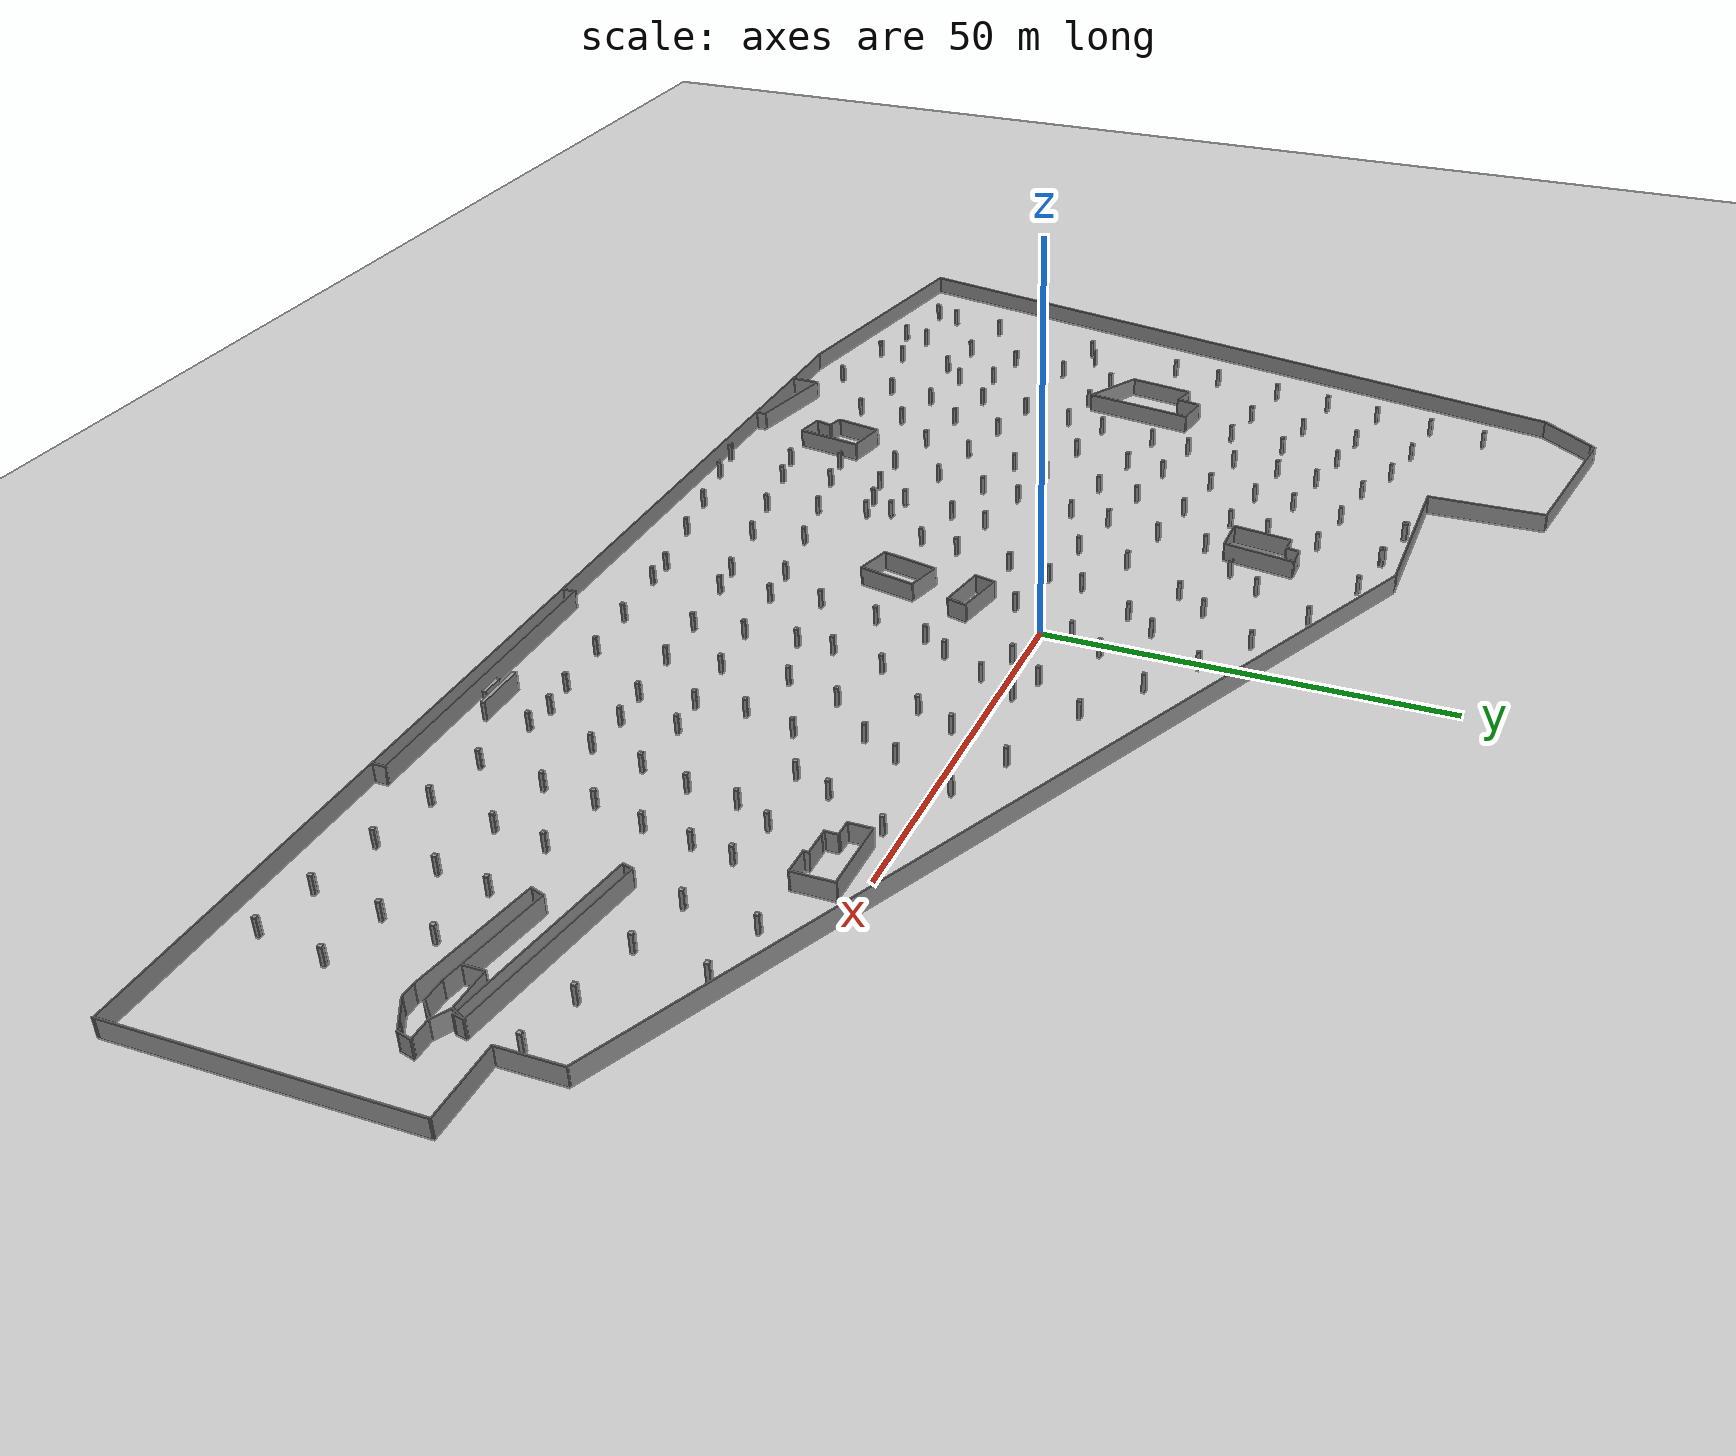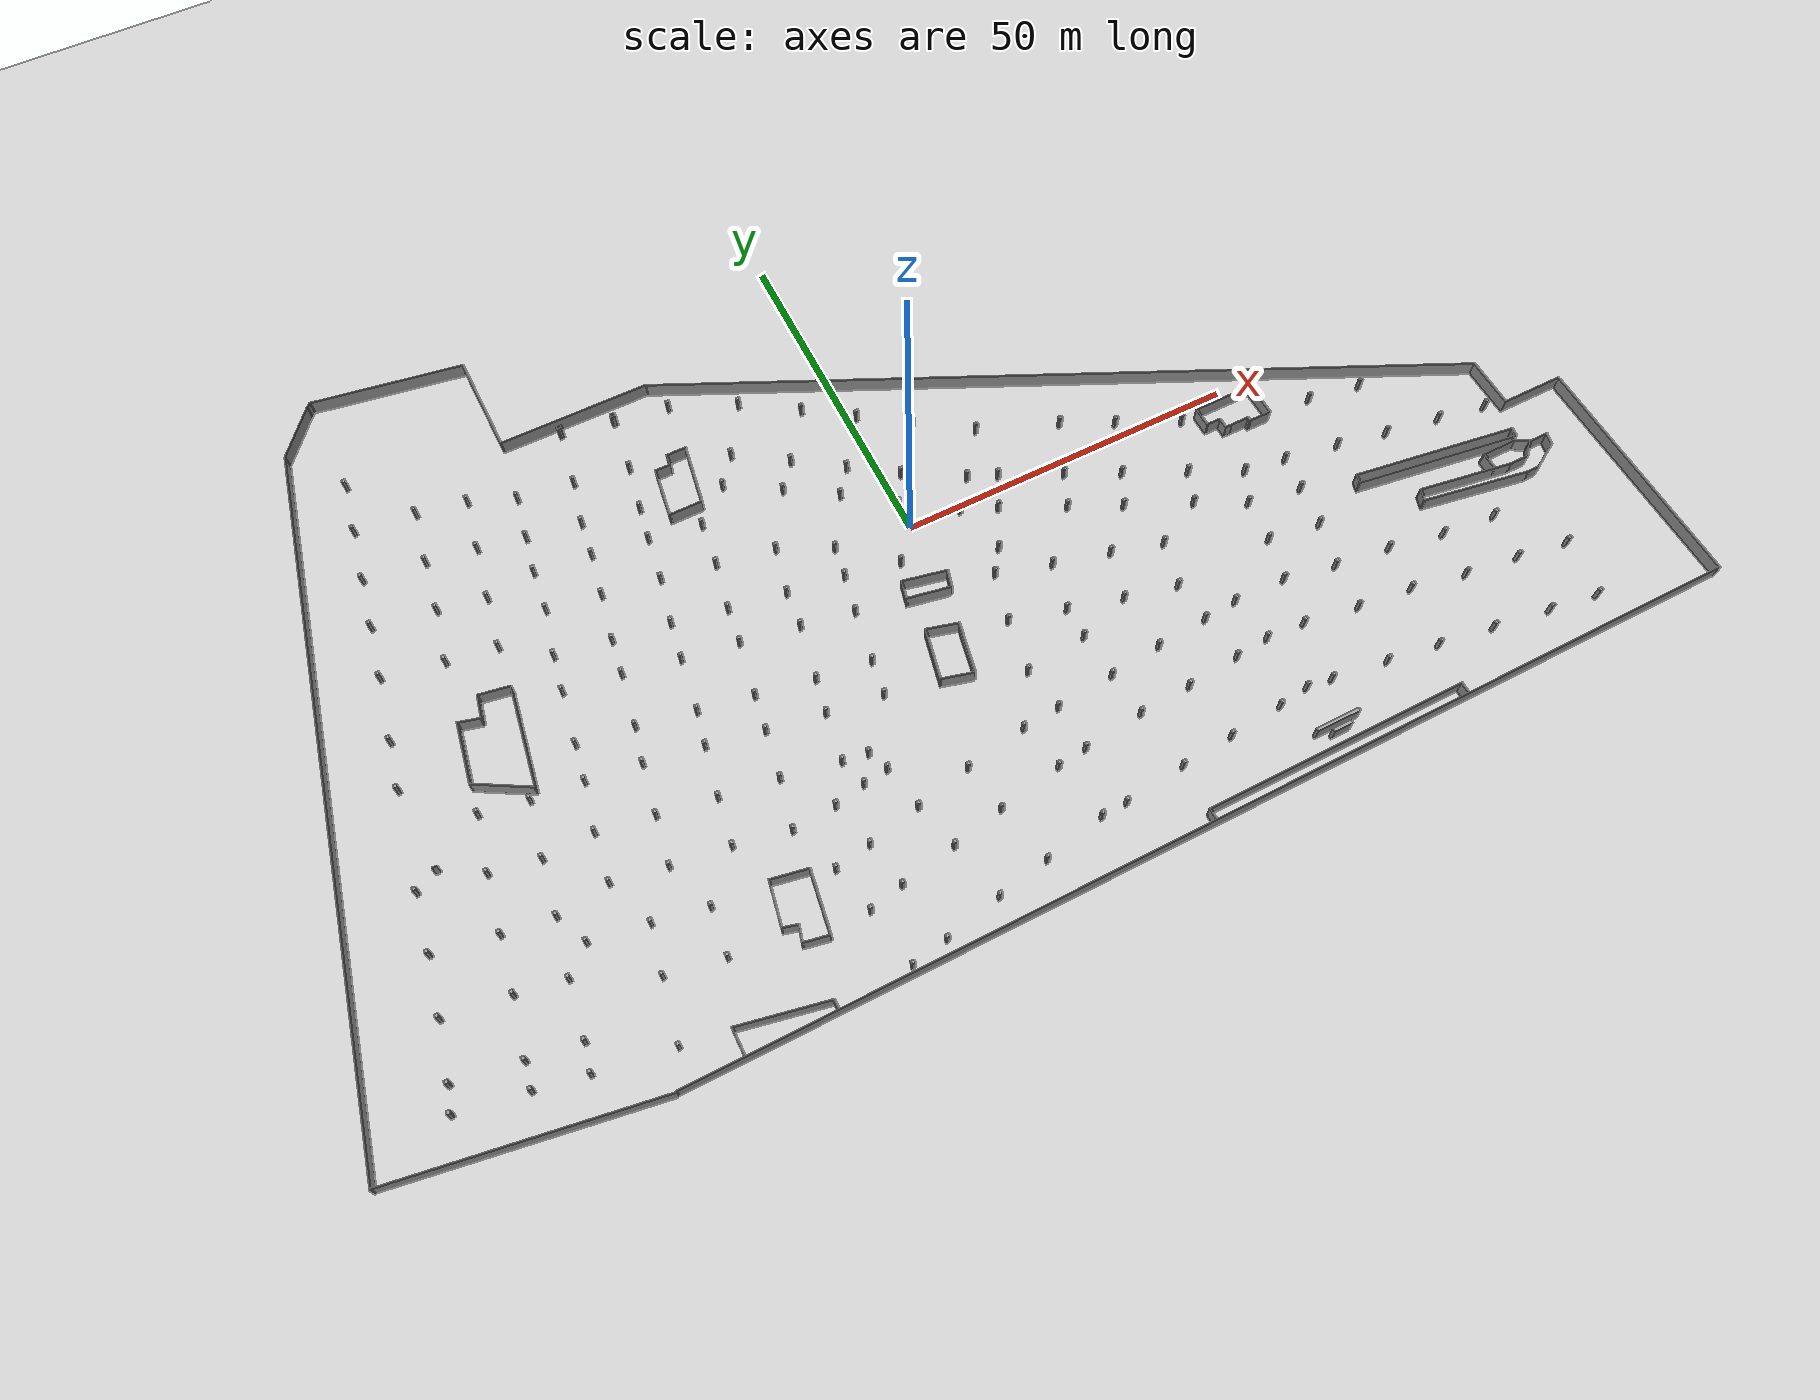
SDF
<sdf version="1.6">
 <world name="default">
  <light name="sun" type="directional">
   <pose>0 0 10 0 -0 0</pose>
   <diffuse>0.8 0.8 0.8 1</diffuse>
   <specular>0.2 0.2 0.2 1</specular>
   <attenuation>
    <range>1000</range>
    <constant>0.9</constant>
    <linear>0.01</linear>
    <quadratic>0.001</quadratic>
   </attenuation>
   <direction>-0.5 0.1 -0.9</direction>
  </light>
  <model name="ground_plane">
   <static>1</static>
   <link name="link">
    <collision name="collision">
     <geometry><plane><normal>0 0 1</normal><size>100 100</size></plane></geometry>
     <surface>
      <contact><collide_bitmask>65535</collide_bitmask></contact>
      <friction><ode><mu>100</mu><mu2>50</mu2></ode></friction>
     </surface>
    </collision>
    <visual name="visual">
     <cast_shadows>0</cast_shadows>
     <geometry><plane><normal>0 0 1</normal><size>100 100</size></plane></geometry>
     <material>
      <script><uri>file://media/materials/scripts/gazebo.material</uri><name>Gazebo/Grey</name></script>
     </material>
    </visual>
   </link>
  </model>
  <gravity>0 0 -9.8</gravity>
  <magnetic_field>6e-06 2.3e-05 -4.2e-05</magnetic_field>
  <atmosphere type="adiabatic"/>
  <physics name="default_physics" default="0" type="ode">
   <max_step_size>0.001</max_step_size>
   <real_time_factor>1</real_time_factor>
   <real_time_update_rate>1000</real_time_update_rate>
  </physics>
  <scene><ambient>0.4 0.4 0.4 1</ambient><background>0.7 0.7 0.7 1</background><shadows>1</shadows></scene>
  <audio><device>default</device></audio>
  <spherical_coordinates>
   <surface_model>EARTH_WGS84</surface_model>
   <latitude_deg>0</latitude_deg>
   <longitude_deg>0</longitude_deg>
   <elevation>0</elevation>
   <heading_deg>0</heading_deg>
  </spherical_coordinates>
  <model name="parking_area_big_2">
   <pose>0.028574 -0.058085 0 0 -0 0</pose>
   <link name="Wall_0">
    <collision name="Wall_0_Collision">
     <geometry><box><size>22.294 0.15 2.5</size></box></geometry>
     <pose>0 0 1.25 0 -0 0</pose>
    </collision>
    <visual name="Wall_0_Visual">
     <pose>0 0 1.25 0 -0 0</pose>
     <geometry><box><size>22.294 0.15 2.5</size></box></geometry>
     <material>
      <script><uri>file://media/materials/scripts/gazebo.material</uri><name>Gazebo/Grey</name></script>
      <ambient>1 1 1 1</ambient>
     </material>
     <meta><layer>0</layer></meta>
    </visual>
    <pose>-57.2743 54.9475 0 0 -0 -0.164921</pose>
   </link>
   <link name="Wall_1">
    <collision name="Wall_1_Collision">
     <geometry><box><size>15.538 0.15 2.5</size></box></geometry>
     <pose>0 0 1.25 0 -0 0</pose>
    </collision>
    <visual name="Wall_1_Visual">
     <pose>0 0 1.25 0 -0 0</pose>
     <geometry><box><size>15.538 0.15 2.5</size></box></geometry>
     <material>
      <script><uri>file://media/materials/scripts/gazebo.material</uri><name>Gazebo/Grey</name></script>
      <ambient>1 1 1 1</ambient>
     </material>
     <meta><layer>0</layer></meta>
    </visual>
    <pose>-46.2467 45.4365 0 0 -0 -1.55705</pose>
   </link>
   <link name="Wall_10">
    <collision name="Wall_10_Collision">
     <geometry><box><size>8.88214 0.15 2.5</size></box></geometry>
     <pose>0 0 1.25 0 -0 0</pose>
    </collision>
    <visual name="Wall_10_Visual">
     <pose>0 0 1.25 0 -0 0</pose>
     <geometry><box><size>8.88214 0.15 2.5</size></box></geometry>
     <material>
      <script><uri>file://media/materials/scripts/gazebo.material</uri><name>Gazebo/Grey</name></script>
      <ambient>1 1 1 1</ambient>
     </material>
     <meta><layer>0</layer></meta>
    </visual>
    <pose>-71.4701 52.712 0 0 -0 0.911925</pose>
   </link>
   <link name="Wall_101">
    <collision name="Wall_101_Collision">
     <geometry><box><size>0.51 0.5 2.5</size></box></geometry>
     <pose>0 0 1.25 0 -0 0</pose>
    </collision>
    <visual name="Wall_101_Visual">
     <pose>0 0 1.25 0 -0 0</pose>
     <geometry><box><size>0.51 0.5 2.5</size></box></geometry>
     <material>
      <script><uri>file://media/materials/scripts/gazebo.material</uri><name>Gazebo/Grey</name></script>
      <ambient>1 1 1 1</ambient>
     </material>
     <meta><layer>0</layer></meta>
    </visual>
    <pose>-0.1445 3.92164 0 0 -0 0</pose>
   </link>
   <link name="Wall_103">
    <collision name="Wall_103_Collision">
     <geometry><box><size>0.51 0.5 2.5</size></box></geometry>
     <pose>0 0 1.25 0 -0 0</pose>
    </collision>
    <visual name="Wall_103_Visual">
     <pose>0 0 1.25 0 -0 0</pose>
     <geometry><box><size>0.51 0.5 2.5</size></box></geometry>
     <material>
      <script><uri>file://media/materials/scripts/gazebo.material</uri><name>Gazebo/Grey</name></script>
      <ambient>1 1 1 1</ambient>
     </material>
     <meta><layer>0</layer></meta>
    </visual>
    <pose>-3.93217 12.6287 0 0 -0 0</pose>
   </link>
   <link name="Wall_105">
    <collision name="Wall_105_Collision">
     <geometry><box><size>0.51 0.5 2.5</size></box></geometry>
     <pose>0 0 1.25 0 -0 0</pose>
    </collision>
    <visual name="Wall_105_Visual">
     <pose>0 0 1.25 0 -0 0</pose>
     <geometry><box><size>0.51 0.5 2.5</size></box></geometry>
     <material>
      <script><uri>file://media/materials/scripts/gazebo.material</uri><name>Gazebo/Grey</name></script>
      <ambient>1 1 1 1</ambient>
     </material>
     <meta><layer>0</layer></meta>
    </visual>
    <pose>-6.70604 8.88032 0 0 -0 0</pose>
   </link>
   <link name="Wall_109">
    <collision name="Wall_109_Collision">
     <geometry><box><size>0.51 0.5 2.5</size></box></geometry>
     <pose>0 0 1.25 0 -0 0</pose>
    </collision>
    <visual name="Wall_109_Visual">
     <pose>0 0 1.25 0 -0 0</pose>
     <geometry><box><size>0.51 0.5 2.5</size></box></geometry>
     <material>
      <script><uri>file://media/materials/scripts/gazebo.material</uri><name>Gazebo/Grey</name></script>
      <ambient>1 1 1 1</ambient>
     </material>
     <meta><layer>0</layer></meta>
    </visual>
    <pose>-10.5222 17.1717 0 0 -0 0</pose>
   </link>
   <link name="Wall_111">
    <collision name="Wall_111_Collision">
     <geometry><box><size>0.51 0.5 2.5</size></box></geometry>
     <pose>0 0 1.25 0 -0 0</pose>
    </collision>
    <visual name="Wall_111_Visual">
     <pose>0 0 1.25 0 -0 0</pose>
     <geometry><box><size>0.51 0.5 2.5</size></box></geometry>
     <material>
      <script><uri>file://media/materials/scripts/gazebo.material</uri><name>Gazebo/Grey</name></script>
      <ambient>1 1 1 1</ambient>
     </material>
     <meta><layer>0</layer></meta>
    </visual>
    <pose>-13.5175 13.285 0 0 -0 0</pose>
   </link>
   <link name="Wall_113">
    <collision name="Wall_113_Collision">
     <geometry><box><size>3 0.15 2.5</size></box></geometry>
     <pose>0 0 1.25 0 -0 0</pose>
    </collision>
    <visual name="Wall_113_Visual">
     <pose>0 0 1.25 0 -0 0</pose>
     <geometry><box><size>3 0.15 2.5</size></box></geometry>
     <material>
      <script><uri>file://media/materials/scripts/gazebo.material</uri><name>Gazebo/Grey</name></script>
      <ambient>1 1 1 1</ambient>
     </material>
     <meta><layer>0</layer></meta>
    </visual>
    <pose>-24.5837 25.1666 0 0 -0 0</pose>
   </link>
   <link name="Wall_114">
    <collision name="Wall_114_Collision">
     <geometry><box><size>9.54099 0.15 2.5</size></box></geometry>
     <pose>0 0 1.25 0 -0 0</pose>
    </collision>
    <visual name="Wall_114_Visual">
     <pose>0 0 1.25 0 -0 0</pose>
     <geometry><box><size>9.54099 0.15 2.5</size></box></geometry>
     <material>
      <script><uri>file://media/materials/scripts/gazebo.material</uri><name>Gazebo/Grey</name></script>
      <ambient>1 1 1 1</ambient>
     </material>
     <meta><layer>0</layer></meta>
    </visual>
    <pose>-23.901 20.5301 0 0 -0 -1.72956</pose>
   </link>
   <link name="Wall_115">
    <collision name="Wall_115_Collision">
     <geometry><box><size>5 0.15 2.5</size></box></geometry>
     <pose>0 0 1.25 0 -0 0</pose>
    </collision>
    <visual name="Wall_115_Visual">
     <pose>0 0 1.25 0 -0 0</pose>
     <geometry><box><size>5 0.15 2.5</size></box></geometry>
     <material>
      <script><uri>file://media/materials/scripts/gazebo.material</uri><name>Gazebo/Grey</name></script>
      <ambient>1 1 1 1</ambient>
     </material>
     <meta><layer>0</layer></meta>
    </visual>
    <pose>-27.0683 15.8937 0 0 -0 3.14159</pose>
   </link>
   <link name="Wall_116">
    <collision name="Wall_116_Collision">
     <geometry><box><size>7.87007 0.15 2.5</size></box></geometry>
     <pose>0 0 1.25 0 -0 0</pose>
    </collision>
    <visual name="Wall_116_Visual">
     <pose>0 0 1.25 0 -0 0</pose>
     <geometry><box><size>7.87007 0.15 2.5</size></box></geometry>
     <material>
      <script><uri>file://media/materials/scripts/gazebo.material</uri><name>Gazebo/Grey</name></script>
      <ambient>1 1 1 1</ambient>
     </material>
     <meta><layer>0</layer></meta>
    </visual>
    <pose>-28.9609 19.7168 0 0 -0 1.43241</pose>
   </link>
   <link name="Wall_117">
    <collision name="Wall_117_Collision">
     <geometry><box><size>2.41635 0.15 2.5</size></box></geometry>
     <pose>0 0 1.25 0 -0 0</pose>
    </collision>
    <visual name="Wall_117_Visual">
     <pose>0 0 1.25 0 -0 0</pose>
     <geometry><box><size>2.41635 0.15 2.5</size></box></geometry>
     <material>
      <script><uri>file://media/materials/scripts/gazebo.material</uri><name>Gazebo/Grey</name></script>
      <ambient>1 1 1 1</ambient>
     </material>
     <meta><layer>0</layer></meta>
    </visual>
    <pose>-27.2952 23.4937 0 0 -0 0</pose>
   </link>
   <link name="Wall_118">
    <collision name="Wall_118_Collision">
     <geometry><box><size>1.8299 0.15 2.5</size></box></geometry>
     <pose>0 0 1.25 0 -0 0</pose>
    </collision>
    <visual name="Wall_118_Visual">
     <pose>0 0 1.25 0 -0 0</pose>
     <geometry><box><size>1.8299 0.15 2.5</size></box></geometry>
     <material>
      <script><uri>file://media/materials/scripts/gazebo.material</uri><name>Gazebo/Grey</name></script>
      <ambient>1 1 1 1</ambient>
     </material>
     <meta><layer>0</layer></meta>
    </visual>
    <pose>-26.0854 24.3301 0 0 -0 1.47938</pose>
   </link>
   <link name="Wall_120">
    <collision name="Wall_120_Collision">
     <geometry><box><size>0.51 0.5 2.5</size></box></geometry>
     <pose>0 0 1.25 0 -0 0</pose>
    </collision>
    <visual name="Wall_120_Visual">
     <pose>0 0 1.25 0 -0 0</pose>
     <geometry><box><size>0.51 0.5 2.5</size></box></geometry>
     <material>
      <script><uri>file://media/materials/scripts/gazebo.material</uri><name>Gazebo/Grey</name></script>
      <ambient>1 1 1 1</ambient>
     </material>
     <meta><layer>0</layer></meta>
    </visual>
    <pose>-31.3614 26.4373 0 0 -0 0</pose>
   </link>
   <link name="Wall_123">
    <collision name="Wall_123_Collision">
     <geometry><box><size>0.51 0.5 2.5</size></box></geometry>
     <pose>0 0 1.25 0 -0 0</pose>
    </collision>
    <visual name="Wall_123_Visual">
     <pose>0 0 1.25 0 -0 0</pose>
     <geometry><box><size>0.51 0.5 2.5</size></box></geometry>
     <material>
      <script><uri>file://media/materials/scripts/gazebo.material</uri><name>Gazebo/Grey</name></script>
      <ambient>1 1 1 1</ambient>
     </material>
     <meta><layer>0</layer></meta>
    </visual>
    <pose>-17.6542 21.9305 0 0 -0 0</pose>
   </link>
   <link name="Wall_125">
    <collision name="Wall_125_Collision">
     <geometry><box><size>0.51 0.5 2.5</size></box></geometry>
     <pose>0 0 1.25 0 -0 0</pose>
    </collision>
    <visual name="Wall_125_Visual">
     <pose>0 0 1.25 0 -0 0</pose>
     <geometry><box><size>0.51 0.5 2.5</size></box></geometry>
     <material>
      <script><uri>file://media/materials/scripts/gazebo.material</uri><name>Gazebo/Grey</name></script>
      <ambient>1 1 1 1</ambient>
     </material>
     <meta><layer>0</layer></meta>
    </visual>
    <pose>-20.8037 17.7488 0 0 -0 0</pose>
   </link>
   <link name="Wall_128">
    <collision name="Wall_128_Collision">
     <geometry><box><size>0.51 0.5 2.5</size></box></geometry>
     <pose>0 0 1.25 0 -0 0</pose>
    </collision>
    <visual name="Wall_128_Visual">
     <pose>0 0 1.25 0 -0 0</pose>
     <geometry><box><size>0.51 0.5 2.5</size></box></geometry>
     <material>
      <script><uri>file://media/materials/scripts/gazebo.material</uri><name>Gazebo/Grey</name></script>
      <ambient>1 1 1 1</ambient>
     </material>
     <meta><layer>0</layer></meta>
    </visual>
    <pose>-25.9255 13.1648 0 0 -0 0</pose>
   </link>
   <link name="Wall_130">
    <collision name="Wall_130_Collision">
     <geometry><box><size>0.51 0.5 2.5</size></box></geometry>
     <pose>0 0 1.25 0 -0 0</pose>
    </collision>
    <visual name="Wall_130_Visual">
     <pose>0 0 1.25 0 -0 0</pose>
     <geometry><box><size>0.51 0.5 2.5</size></box></geometry>
     <material>
      <script><uri>file://media/materials/scripts/gazebo.material</uri><name>Gazebo/Grey</name></script>
      <ambient>1 1 1 1</ambient>
     </material>
     <meta><layer>0</layer></meta>
    </visual>
    <pose>-32.578 19.608 0 0 -0 -1.5708</pose>
   </link>
   <link name="Wall_132">
    <collision name="Wall_132_Collision">
     <geometry><box><size>0.51 0.5 2.5</size></box></geometry>
     <pose>0 0 1.25 0 -0 0</pose>
    </collision>
    <visual name="Wall_132_Visual">
     <pose>0 0 1.25 0 -0 0</pose>
     <geometry><box><size>0.51 0.5 2.5</size></box></geometry>
     <material>
      <script><uri>file://media/materials/scripts/gazebo.material</uri><name>Gazebo/Grey</name></script>
      <ambient>1 1 1 1</ambient>
     </material>
     <meta><layer>0</layer></meta>
    </visual>
    <pose>-33.4387 14.4529 0 0 -0 0</pose>
   </link>
   <link name="Wall_134">
    <collision name="Wall_134_Collision">
     <geometry><box><size>0.51 0.5 2.5</size></box></geometry>
     <pose>0 0 1.25 0 -0 0</pose>
    </collision>
    <visual name="Wall_134_Visual">
     <pose>0 0 1.25 0 -0 0</pose>
     <geometry><box><size>0.51 0.5 2.5</size></box></geometry>
     <material>
      <script><uri>file://media/materials/scripts/gazebo.material</uri><name>Gazebo/Grey</name></script>
      <ambient>1 1 1 1</ambient>
     </material>
     <meta><layer>0</layer></meta>
    </visual>
    <pose>-39.2624 27.7352 0 0 -0 0</pose>
   </link>
   <link name="Wall_136">
    <collision name="Wall_136_Collision">
     <geometry><box><size>0.51 0.5 2.5</size></box></geometry>
     <pose>0 0 1.25 0 -0 0</pose>
    </collision>
    <visual name="Wall_136_Visual">
     <pose>0 0 1.25 0 -0 0</pose>
     <geometry><box><size>0.51 0.5 2.5</size></box></geometry>
     <material>
      <script><uri>file://media/materials/scripts/gazebo.material</uri><name>Gazebo/Grey</name></script>
      <ambient>1 1 1 1</ambient>
     </material>
     <meta><layer>0</layer></meta>
    </visual>
    <pose>-40.7024 21.0485 0 0 -0 0</pose>
   </link>
   <link name="Wall_138">
    <collision name="Wall_138_Collision">
     <geometry><box><size>0.51 0.5 2.5</size></box></geometry>
     <pose>0 0 1.25 0 -0 0</pose>
    </collision>
    <visual name="Wall_138_Visual">
     <pose>0 0 1.25 0 -0 0</pose>
     <geometry><box><size>0.51 0.5 2.5</size></box></geometry>
     <material>
      <script><uri>file://media/materials/scripts/gazebo.material</uri><name>Gazebo/Grey</name></script>
      <ambient>1 1 1 1</ambient>
     </material>
     <meta><layer>0</layer></meta>
    </visual>
    <pose>-41.363 15.6649 0 0 -0 0</pose>
   </link>
   <link name="Wall_140">
    <collision name="Wall_140_Collision">
     <geometry><box><size>0.51 0.5 2.5</size></box></geometry>
     <pose>0 0 1.25 0 -0 0</pose>
    </collision>
    <visual name="Wall_140_Visual">
     <pose>0 0 1.25 0 -0 0</pose>
     <geometry><box><size>0.51 0.5 2.5</size></box></geometry>
     <material>
      <script><uri>file://media/materials/scripts/gazebo.material</uri><name>Gazebo/Grey</name></script>
      <ambient>1 1 1 1</ambient>
     </material>
     <meta><layer>0</layer></meta>
    </visual>
    <pose>-47.2516 28.8876 0 0 -0 0</pose>
   </link>
   <link name="Wall_142">
    <collision name="Wall_142_Collision">
     <geometry><box><size>0.51 0.5 2.5</size></box></geometry>
     <pose>0 0 1.25 0 -0 0</pose>
    </collision>
    <visual name="Wall_142_Visual">
     <pose>0 0 1.25 0 -0 0</pose>
     <geometry><box><size>0.51 0.5 2.5</size></box></geometry>
     <material>
      <script><uri>file://media/materials/scripts/gazebo.material</uri><name>Gazebo/Grey</name></script>
      <ambient>1 1 1 1</ambient>
     </material>
     <meta><layer>0</layer></meta>
    </visual>
    <pose>-48.3892 22.3626 0 0 -0 0</pose>
   </link>
   <link name="Wall_144">
    <collision name="Wall_144_Collision">
     <geometry><box><size>0.51 0.5 2.5</size></box></geometry>
     <pose>0 0 1.25 0 -0 0</pose>
    </collision>
    <visual name="Wall_144_Visual">
     <pose>0 0 1.25 0 -0 0</pose>
     <geometry><box><size>0.51 0.5 2.5</size></box></geometry>
     <material>
      <script><uri>file://media/materials/scripts/gazebo.material</uri><name>Gazebo/Grey</name></script>
      <ambient>1 1 1 1</ambient>
     </material>
     <meta><layer>0</layer></meta>
    </visual>
    <pose>-49.3854 16.7562 0 0 -0 0</pose>
   </link>
   <link name="Wall_146">
    <collision name="Wall_146_Collision">
     <geometry><box><size>0.51 0.5 2.5</size></box></geometry>
     <pose>0 0 1.25 0 -0 0</pose>
    </collision>
    <visual name="Wall_146_Visual">
     <pose>0 0 1.25 0 -0 0</pose>
     <geometry><box><size>0.51 0.5 2.5</size></box></geometry>
     <material>
      <script><uri>file://media/materials/scripts/gazebo.material</uri><name>Gazebo/Grey</name></script>
      <ambient>1 1 1 1</ambient>
     </material>
     <meta><layer>0</layer></meta>
    </visual>
    <pose>-55.0202 23.7748 0 0 -0 0</pose>
   </link>
   <link name="Wall_148">
    <collision name="Wall_148_Collision">
     <geometry><box><size>0.51 0.5 2.5</size></box></geometry>
     <pose>0 0 1.25 0 -0 0</pose>
    </collision>
    <visual name="Wall_148_Visual">
     <pose>0 0 1.25 0 -0 0</pose>
     <geometry><box><size>0.51 0.5 2.5</size></box></geometry>
     <material>
      <script><uri>file://media/materials/scripts/gazebo.material</uri><name>Gazebo/Grey</name></script>
      <ambient>1 1 1 1</ambient>
     </material>
     <meta><layer>0</layer></meta>
    </visual>
    <pose>-62.0556 24.9172 0 0 -0 0</pose>
   </link>
   <link name="Wall_15">
    <collision name="Wall_15_Collision">
     <geometry><box><size>1 0.15 2.5</size></box></geometry>
     <pose>0 0 1.25 0 -0 0</pose>
    </collision>
    <visual name="Wall_15_Visual">
     <pose>0 0 1.25 0 -0 0</pose>
     <geometry><box><size>1 0.15 2.5</size></box></geometry>
     <material>
      <script><uri>file://media/materials/scripts/gazebo.material</uri><name>Gazebo/Grey</name></script>
      <ambient>1 1 1 1</ambient>
     </material>
     <meta><layer>0</layer></meta>
    </visual>
    <pose>-68.4965 56.4647 0 0 -0 0.785398</pose>
   </link>
   <link name="Wall_150">
    <collision name="Wall_150_Collision">
     <geometry><box><size>0.51 0.5 2.5</size></box></geometry>
     <pose>0 0 1.25 0 -0 0</pose>
    </collision>
    <visual name="Wall_150_Visual">
     <pose>0 0 1.25 0 -0 0</pose>
     <geometry><box><size>0.51 0.5 2.5</size></box></geometry>
     <material>
      <script><uri>file://media/materials/scripts/gazebo.material</uri><name>Gazebo/Grey</name></script>
      <ambient>1 1 1 1</ambient>
     </material>
     <meta><layer>0</layer></meta>
    </visual>
    <pose>-56.4237 15.7517 0 0 -0 0</pose>
   </link>
   <link name="Wall_152">
    <collision name="Wall_152_Collision">
     <geometry><box><size>0.51 0.5 2.5</size></box></geometry>
     <pose>0 0 1.25 0 -0 0</pose>
    </collision>
    <visual name="Wall_152_Visual">
     <pose>0 0 1.25 0 -0 0</pose>
     <geometry><box><size>0.51 0.5 2.5</size></box></geometry>
     <material>
      <script><uri>file://media/materials/scripts/gazebo.material</uri><name>Gazebo/Grey</name></script>
      <ambient>1 1 1 1</ambient>
     </material>
     <meta><layer>0</layer></meta>
    </visual>
    <pose>-57.6618 8.08292 0 0 -0 0</pose>
   </link>
   <link name="Wall_154">
    <collision name="Wall_154_Collision">
     <geometry><box><size>0.51 0.5 2.5</size></box></geometry>
     <pose>0 0 1.25 0 -0 0</pose>
    </collision>
    <visual name="Wall_154_Visual">
     <pose>0 0 1.25 0 -0 0</pose>
     <geometry><box><size>0.51 0.5 2.5</size></box></geometry>
     <material>
      <script><uri>file://media/materials/scripts/gazebo.material</uri><name>Gazebo/Grey</name></script>
      <ambient>1 1 1 1</ambient>
     </material>
     <meta><layer>0</layer></meta>
    </visual>
    <pose>-64.695 9.19521 0 0 -0 0</pose>
   </link>
   <link name="Wall_156">
    <collision name="Wall_156_Collision">
     <geometry><box><size>0.51 0.5 2.5</size></box></geometry>
     <pose>0 0 1.25 0 -0 0</pose>
    </collision>
    <visual name="Wall_156_Visual">
     <pose>0 0 1.25 0 -0 0</pose>
     <geometry><box><size>0.51 0.5 2.5</size></box></geometry>
     <material>
      <script><uri>file://media/materials/scripts/gazebo.material</uri><name>Gazebo/Grey</name></script>
      <ambient>1 1 1 1</ambient>
     </material>
     <meta><layer>0</layer></meta>
    </visual>
    <pose>-63.1472 17.117 0 0 -0 0</pose>
   </link>
   <link name="Wall_158">
    <collision name="Wall_158_Collision">
     <geometry><box><size>0.51 0.5 2.5</size></box></geometry>
     <pose>0 0 1.25 0 -0 0</pose>
    </collision>
    <visual name="Wall_158_Visual">
     <pose>0 0 1.25 0 -0 0</pose>
     <geometry><box><size>0.51 0.5 2.5</size></box></geometry>
     <material>
      <script><uri>file://media/materials/scripts/gazebo.material</uri><name>Gazebo/Grey</name></script>
      <ambient>1 1 1 1</ambient>
     </material>
     <meta><layer>0</layer></meta>
    </visual>
    <pose>-69.284 34.0738 0 0 -0 0</pose>
   </link>
   <link name="Wall_160">
    <collision name="Wall_160_Collision">
     <geometry><box><size>0.51 0.5 2.5</size></box></geometry>
     <pose>0 0 1.25 0 -0 0</pose>
    </collision>
    <visual name="Wall_160_Visual">
     <pose>0 0 1.25 0 -0 0</pose>
     <geometry><box><size>0.51 0.5 2.5</size></box></geometry>
     <material>
      <script><uri>file://media/materials/scripts/gazebo.material</uri><name>Gazebo/Grey</name></script>
      <ambient>1 1 1 1</ambient>
     </material>
     <meta><layer>0</layer></meta>
    </visual>
    <pose>-53.6493 31.545 0 0 -0 0</pose>
   </link>
   <link name="Wall_162">
    <collision name="Wall_162_Collision">
     <geometry><box><size>0.51 0.5 2.5</size></box></geometry>
     <pose>0 0 1.25 0 -0 0</pose>
    </collision>
    <visual name="Wall_162_Visual">
     <pose>0 0 1.25 0 -0 0</pose>
     <geometry><box><size>0.51 0.5 2.5</size></box></geometry>
     <material>
      <script><uri>file://media/materials/scripts/gazebo.material</uri><name>Gazebo/Grey</name></script>
      <ambient>1 1 1 1</ambient>
     </material>
     <meta><layer>0</layer></meta>
    </visual>
    <pose>-60.7046 32.9965 0 0 -0 0</pose>
   </link>
   <link name="Wall_164">
    <collision name="Wall_164_Collision">
     <geometry><box><size>0.51 0.5 2.5</size></box></geometry>
     <pose>0 0 1.25 0 -0 0</pose>
    </collision>
    <visual name="Wall_164_Visual">
     <pose>0 0 1.25 0 -0 0</pose>
     <geometry><box><size>0.51 0.5 2.5</size></box></geometry>
     <material>
      <script><uri>file://media/materials/scripts/gazebo.material</uri><name>Gazebo/Grey</name></script>
      <ambient>1 1 1 1</ambient>
     </material>
     <meta><layer>0</layer></meta>
    </visual>
    <pose>-70.6184 26.1599 0 0 -0 0</pose>
   </link>
   <link name="Wall_166">
    <collision name="Wall_166_Collision">
     <geometry><box><size>0.51 0.5 2.5</size></box></geometry>
     <pose>0 0 1.25 0 -0 0</pose>
    </collision>
    <visual name="Wall_166_Visual">
     <pose>0 0 1.25 0 -0 0</pose>
     <geometry><box><size>0.51 0.5 2.5</size></box></geometry>
     <material>
      <script><uri>file://media/materials/scripts/gazebo.material</uri><name>Gazebo/Grey</name></script>
      <ambient>1 1 1 1</ambient>
     </material>
     <meta><layer>0</layer></meta>
    </visual>
    <pose>-71.8619 18.6695 0 0 -0 0</pose>
   </link>
   <link name="Wall_168">
    <collision name="Wall_168_Collision">
     <geometry><box><size>0.51 0.5 2.5</size></box></geometry>
     <pose>0 0 1.25 0 -0 0</pose>
    </collision>
    <visual name="Wall_168_Visual">
     <pose>0 0 1.25 0 -0 0</pose>
     <geometry><box><size>0.51 0.5 2.5</size></box></geometry>
     <material>
      <script><uri>file://media/materials/scripts/gazebo.material</uri><name>Gazebo/Grey</name></script>
      <ambient>1 1 1 1</ambient>
     </material>
     <meta><layer>0</layer></meta>
    </visual>
    <pose>-73.1803 10.8328 0 0 -0 0</pose>
   </link>
   <link name="Wall_17">
    <collision name="Wall_17_Collision">
     <geometry><box><size>0.75 0.15 2.5</size></box></geometry>
     <pose>0 0 1.25 0 -0 0</pose>
    </collision>
    <visual name="Wall_17_Visual">
     <pose>0 0 1.25 0 -0 0</pose>
     <geometry><box><size>0.75 0.15 2.5</size></box></geometry>
     <material>
      <script><uri>file://media/materials/scripts/gazebo.material</uri><name>Gazebo/Grey</name></script>
      <ambient>1 1 1 1</ambient>
     </material>
     <meta><layer>0</layer></meta>
    </visual>
    <pose>-37.8263 36.768 0 0 -0 3.14159</pose>
   </link>
   <link name="Wall_170">
    <collision name="Wall_170_Collision">
     <geometry><box><size>0.51 0.5 2.5</size></box></geometry>
     <pose>0 0 1.25 0 -0 0</pose>
    </collision>
    <visual name="Wall_170_Visual">
     <pose>0 0 1.25 0 -0 0</pose>
     <geometry><box><size>0.51 0.5 2.5</size></box></geometry>
     <material>
      <script><uri>file://media/materials/scripts/gazebo.material</uri><name>Gazebo/Grey</name></script>
      <ambient>1 1 1 1</ambient>
     </material>
     <meta><layer>0</layer></meta>
    </visual>
    <pose>-50.017 10.4772 0 0 -0 0</pose>
   </link>
   <link name="Wall_172">
    <collision name="Wall_172_Collision">
     <geometry><box><size>0.51 0.5 2.5</size></box></geometry>
     <pose>0 0 1.25 0 -0 0</pose>
    </collision>
    <visual name="Wall_172_Visual">
     <pose>0 0 1.25 0 -0 0</pose>
     <geometry><box><size>0.51 0.5 2.5</size></box></geometry>
     <material>
      <script><uri>file://media/materials/scripts/gazebo.material</uri><name>Gazebo/Grey</name></script>
      <ambient>1 1 1 1</ambient>
     </material>
     <meta><layer>0</layer></meta>
    </visual>
    <pose>-42.458 9.22408 0 0 -0 0</pose>
   </link>
   <link name="Wall_174">
    <collision name="Wall_174_Collision">
     <geometry><box><size>0.51 0.5 2.5</size></box></geometry>
     <pose>0 0 1.25 0 -0 0</pose>
    </collision>
    <visual name="Wall_174_Visual">
     <pose>0 0 1.25 0 -0 0</pose>
     <geometry><box><size>0.51 0.5 2.5</size></box></geometry>
     <material>
      <script><uri>file://media/materials/scripts/gazebo.material</uri><name>Gazebo/Grey</name></script>
      <ambient>1 1 1 1</ambient>
     </material>
     <meta><layer>0</layer></meta>
    </visual>
    <pose>-34.3719 7.84932 0 0 -0 0</pose>
   </link>
   <link name="Wall_176">
    <collision name="Wall_176_Collision">
     <geometry><box><size>0.51 0.5 2.5</size></box></geometry>
     <pose>0 0 1.25 0 -0 0</pose>
    </collision>
    <visual name="Wall_176_Visual">
     <pose>0 0 1.25 0 -0 0</pose>
     <geometry><box><size>0.51 0.5 2.5</size></box></geometry>
     <material>
      <script><uri>file://media/materials/scripts/gazebo.material</uri><name>Gazebo/Grey</name></script>
      <ambient>1 1 1 1</ambient>
     </material>
     <meta><layer>0</layer></meta>
    </visual>
    <pose>-26.715 6.56345 0 0 -0 0</pose>
   </link>
   <link name="Wall_178">
    <collision name="Wall_178_Collision">
     <geometry><box><size>0.51 0.5 2.5</size></box></geometry>
     <pose>0 0 1.25 0 -0 0</pose>
    </collision>
    <visual name="Wall_178_Visual">
     <pose>0 0 1.25 0 -0 0</pose>
     <geometry><box><size>0.51 0.5 2.5</size></box></geometry>
     <material>
      <script><uri>file://media/materials/scripts/gazebo.material</uri><name>Gazebo/Grey</name></script>
      <ambient>1 1 1 1</ambient>
     </material>
     <meta><layer>0</layer></meta>
    </visual>
    <pose>-18.4105 5.04505 0 0 -0 3.14159</pose>
   </link>
   <link name="Wall_18">
    <collision name="Wall_18_Collision">
     <geometry><box><size>0.75 0.15 2.5</size></box></geometry>
     <pose>0 0 1.25 0 -0 0</pose>
    </collision>
    <visual name="Wall_18_Visual">
     <pose>0 0 1.25 0 -0 0</pose>
     <geometry><box><size>0.75 0.15 2.5</size></box></geometry>
     <material>
      <script><uri>file://media/materials/scripts/gazebo.material</uri><name>Gazebo/Grey</name></script>
      <ambient>1 1 1 1</ambient>
     </material>
     <meta><layer>0</layer></meta>
    </visual>
    <pose>-38.1263 36.468 0 0 -0 -1.5708</pose>
   </link>
   <link name="Wall_180">
    <collision name="Wall_180_Collision">
     <geometry><box><size>0.51 0.5 2.5</size></box></geometry>
     <pose>0 0 1.25 0 -0 0</pose>
    </collision>
    <visual name="Wall_180_Visual">
     <pose>0 0 1.25 0 -0 0</pose>
     <geometry><box><size>0.51 0.5 2.5</size></box></geometry>
     <material>
      <script><uri>file://media/materials/scripts/gazebo.material</uri><name>Gazebo/Grey</name></script>
      <ambient>1 1 1 1</ambient>
     </material>
     <meta><layer>0</layer></meta>
    </visual>
    <pose>-11.0992 1.45815 0 0 -0 0</pose>
   </link>
   <link name="Wall_182">
    <collision name="Wall_182_Collision">
     <geometry><box><size>0.51 0.5 2.5</size></box></geometry>
     <pose>0 0 1.25 0 -0 0</pose>
    </collision>
    <visual name="Wall_182_Visual">
     <pose>0 0 1.25 0 -0 0</pose>
     <geometry><box><size>0.51 0.5 2.5</size></box></geometry>
     <material>
      <script><uri>file://media/materials/scripts/gazebo.material</uri><name>Gazebo/Grey</name></script>
      <ambient>1 1 1 1</ambient>
     </material>
     <meta><layer>0</layer></meta>
    </visual>
    <pose>-11.8341 -3.13263 0 0 -0 0</pose>
   </link>
   <link name="Wall_184">
    <collision name="Wall_184_Collision">
     <geometry><box><size>0.51 0.5 2.5</size></box></geometry>
     <pose>0 0 1.25 0 -0 0</pose>
    </collision>
    <visual name="Wall_184_Visual">
     <pose>0 0 1.25 0 -0 0</pose>
     <geometry><box><size>0.51 0.5 2.5</size></box></geometry>
     <material>
      <script><uri>file://media/materials/scripts/gazebo.material</uri><name>Gazebo/Grey</name></script>
      <ambient>1 1 1 1</ambient>
     </material>
     <meta><layer>0</layer></meta>
    </visual>
    <pose>-3.99875 -4.66542 0 0 -0 0</pose>
   </link>
   <link name="Wall_186">
    <collision name="Wall_186_Collision">
     <geometry><box><size>6.59009 0.15 2.5</size></box></geometry>
     <pose>0 0 1.25 0 -0 0</pose>
    </collision>
    <visual name="Wall_186_Visual">
     <pose>0 0 1.25 0 -0 0</pose>
     <geometry><box><size>6.59009 0.15 2.5</size></box></geometry>
     <material>
      <script><uri>file://media/materials/scripts/gazebo.material</uri><name>Gazebo/Grey</name></script>
      <ambient>1 1 1 1</ambient>
     </material>
     <meta><layer>0</layer></meta>
    </visual>
    <pose>-2.46992 -8.72498 0 0 -0 -0.207766</pose>
   </link>
   <link name="Wall_187">
    <collision name="Wall_187_Collision">
     <geometry><box><size>2.75 0.15 2.5</size></box></geometry>
     <pose>0 0 1.25 0 -0 0</pose>
    </collision>
    <visual name="Wall_187_Visual">
     <pose>0 0 1.25 0 -0 0</pose>
     <geometry><box><size>2.75 0.15 2.5</size></box></geometry>
     <material>
      <script><uri>file://media/materials/scripts/gazebo.material</uri><name>Gazebo/Grey</name></script>
      <ambient>1 1 1 1</ambient>
     </material>
     <meta><layer>0</layer></meta>
    </visual>
    <pose>0.344408 -10.6449 0 0 -0 -1.8326</pose>
   </link>
   <link name="Wall_188">
    <collision name="Wall_188_Collision">
     <geometry><box><size>6.51966 0.15 2.5</size></box></geometry>
     <pose>0 0 1.25 0 -0 0</pose>
    </collision>
    <visual name="Wall_188_Visual">
     <pose>0 0 1.25 0 -0 0</pose>
     <geometry><box><size>6.51966 0.15 2.5</size></box></geometry>
     <material>
      <script><uri>file://media/materials/scripts/gazebo.material</uri><name>Gazebo/Grey</name></script>
      <ambient>1 1 1 1</ambient>
     </material>
     <meta><layer>0</layer></meta>
    </visual>
    <pose>-3.12358 -11.3203 0 0 -0 2.95837</pose>
   </link>
   <link name="Wall_189">
    <collision name="Wall_189_Collision">
     <geometry><box><size>2.94197 0.15 2.5</size></box></geometry>
     <pose>0 0 1.25 0 -0 0</pose>
    </collision>
    <visual name="Wall_189_Visual">
     <pose>0 0 1.25 0 -0 0</pose>
     <geometry><box><size>2.94197 0.15 2.5</size></box></geometry>
     <material>
      <script><uri>file://media/materials/scripts/gazebo.material</uri><name>Gazebo/Grey</name></script>
      <ambient>1 1 1 1</ambient>
     </material>
     <meta><layer>0</layer></meta>
    </visual>
    <pose>-5.93791 -9.38059 0 0 -0 1.34158</pose>
   </link>
   <link name="Wall_19">
    <collision name="Wall_19_Collision">
     <geometry><box><size>0.75 0.15 2.5</size></box></geometry>
     <pose>0 0 1.25 0 -0 0</pose>
    </collision>
    <visual name="Wall_19_Visual">
     <pose>0 0 1.25 0 -0 0</pose>
     <geometry><box><size>0.75 0.15 2.5</size></box></geometry>
     <material>
      <script><uri>file://media/materials/scripts/gazebo.material</uri><name>Gazebo/Grey</name></script>
      <ambient>1 1 1 1</ambient>
     </material>
     <meta><layer>0</layer></meta>
    </visual>
    <pose>-37.8263 36.168 0 0 -0 0</pose>
   </link>
   <link name="Wall_191">
    <collision name="Wall_191_Collision">
     <geometry><box><size>0.51 0.5 2.5</size></box></geometry>
     <pose>0 0 1.25 0 -0 0</pose>
    </collision>
    <visual name="Wall_191_Visual">
     <pose>0 0 1.25 0 -0 0</pose>
     <geometry><box><size>0.51 0.5 2.5</size></box></geometry>
     <material>
      <script><uri>file://media/materials/scripts/gazebo.material</uri><name>Gazebo/Grey</name></script>
      <ambient>1 1 1 1</ambient>
     </material>
     <meta><layer>0</layer></meta>
    </visual>
    <pose>-12.9415 -8.74134 0 0 -0 0</pose>
   </link>
   <link name="Wall_193">
    <collision name="Wall_193_Collision">
     <geometry><box><size>0.51 0.5 2.5</size></box></geometry>
     <pose>0 0 1.25 0 -0 0</pose>
    </collision>
    <visual name="Wall_193_Visual">
     <pose>0 0 1.25 0 -0 0</pose>
     <geometry><box><size>0.51 0.5 2.5</size></box></geometry>
     <material>
      <script><uri>file://media/materials/scripts/gazebo.material</uri><name>Gazebo/Grey</name></script>
      <ambient>1 1 1 1</ambient>
     </material>
     <meta><layer>0</layer></meta>
    </visual>
    <pose>-19.9409 -1.90272 0 0 -0 0</pose>
   </link>
   <link name="Wall_195">
    <collision name="Wall_195_Collision">
     <geometry><box><size>0.51 0.5 2.5</size></box></geometry>
     <pose>0 0 1.25 0 -0 0</pose>
    </collision>
    <visual name="Wall_195_Visual">
     <pose>0 0 1.25 0 -0 0</pose>
     <geometry><box><size>0.51 0.5 2.5</size></box></geometry>
     <material>
      <script><uri>file://media/materials/scripts/gazebo.material</uri><name>Gazebo/Grey</name></script>
      <ambient>1 1 1 1</ambient>
     </material>
     <meta><layer>0</layer></meta>
    </visual>
    <pose>-28.0618 -0.573806 0 0 -0 0</pose>
   </link>
   <link name="Wall_197">
    <collision name="Wall_197_Collision">
     <geometry><box><size>0.51 0.5 2.5</size></box></geometry>
     <pose>0 0 1.25 0 -0 0</pose>
    </collision>
    <visual name="Wall_197_Visual">
     <pose>0 0 1.25 0 -0 0</pose>
     <geometry><box><size>0.51 0.5 2.5</size></box></geometry>
     <material>
      <script><uri>file://media/materials/scripts/gazebo.material</uri><name>Gazebo/Grey</name></script>
      <ambient>1 1 1 1</ambient>
     </material>
     <meta><layer>0</layer></meta>
    </visual>
    <pose>-35.7914 0.937456 0 0 -0 0</pose>
   </link>
   <link name="Wall_199">
    <collision name="Wall_199_Collision">
     <geometry><box><size>0.51 0.5 2.5</size></box></geometry>
     <pose>0 0 1.25 0 -0 0</pose>
    </collision>
    <visual name="Wall_199_Visual">
     <pose>0 0 1.25 0 -0 0</pose>
     <geometry><box><size>0.51 0.5 2.5</size></box></geometry>
     <material>
      <script><uri>file://media/materials/scripts/gazebo.material</uri><name>Gazebo/Grey</name></script>
      <ambient>1 1 1 1</ambient>
     </material>
     <meta><layer>0</layer></meta>
    </visual>
    <pose>-43.7778 2.13144 0 0 -0 0</pose>
   </link>
   <link name="Wall_2">
    <collision name="Wall_2_Collision">
     <geometry><box><size>22.25 0.15 2.5</size></box></geometry>
     <pose>0 0 1.25 0 -0 0</pose>
    </collision>
    <visual name="Wall_2_Visual">
     <pose>0 0 1.25 0 -0 0</pose>
     <geometry><box><size>22.25 0.15 2.5</size></box></geometry>
     <material>
      <script><uri>file://media/materials/scripts/gazebo.material</uri><name>Gazebo/Grey</name></script>
      <ambient>1 1 1 1</ambient>
     </material>
     <meta><layer>0</layer></meta>
    </visual>
    <pose>-35.0909 37.7432 0 0 -0 0</pose>
   </link>
   <link name="Wall_20">
    <collision name="Wall_20_Collision">
     <geometry><box><size>0.75 0.15 2.5</size></box></geometry>
     <pose>0 0 1.25 0 -0 0</pose>
    </collision>
    <visual name="Wall_20_Visual">
     <pose>0 0 1.25 0 -0 0</pose>
     <geometry><box><size>0.75 0.15 2.5</size></box></geometry>
     <material>
      <script><uri>file://media/materials/scripts/gazebo.material</uri><name>Gazebo/Grey</name></script>
      <ambient>1 1 1 1</ambient>
     </material>
     <meta><layer>0</layer></meta>
    </visual>
    <pose>-37.5263 36.468 0 0 -0 1.5708</pose>
   </link>
   <link name="Wall_201">
    <collision name="Wall_201_Collision">
     <geometry><box><size>0.51 0.5 2.5</size></box></geometry>
     <pose>0 0 1.25 0 -0 0</pose>
    </collision>
    <visual name="Wall_201_Visual">
     <pose>0 0 1.25 0 -0 0</pose>
     <geometry><box><size>0.51 0.5 2.5</size></box></geometry>
     <material>
      <script><uri>file://media/materials/scripts/gazebo.material</uri><name>Gazebo/Grey</name></script>
      <ambient>1 1 1 1</ambient>
     </material>
     <meta><layer>0</layer></meta>
    </visual>
    <pose>-51.565 3.48997 0 0 -0 0</pose>
   </link>
   <link name="Wall_203">
    <collision name="Wall_203_Collision">
     <geometry><box><size>0.51 0.5 2.5</size></box></geometry>
     <pose>0 0 1.25 0 -0 0</pose>
    </collision>
    <visual name="Wall_203_Visual">
     <pose>0 0 1.25 0 -0 0</pose>
     <geometry><box><size>0.51 0.5 2.5</size></box></geometry>
     <material>
      <script><uri>file://media/materials/scripts/gazebo.material</uri><name>Gazebo/Grey</name></script>
      <ambient>1 1 1 1</ambient>
     </material>
     <meta><layer>0</layer></meta>
    </visual>
    <pose>-52.4516 -1.97817 0 0 -0 1.5708</pose>
   </link>
   <link name="Wall_205">
    <collision name="Wall_205_Collision">
     <geometry><box><size>0.51 0.5 2.5</size></box></geometry>
     <pose>0 0 1.25 0 -0 0</pose>
    </collision>
    <visual name="Wall_205_Visual">
     <pose>0 0 1.25 0 -0 0</pose>
     <geometry><box><size>0.51 0.5 2.5</size></box></geometry>
     <material>
      <script><uri>file://media/materials/scripts/gazebo.material</uri><name>Gazebo/Grey</name></script>
      <ambient>1 1 1 1</ambient>
     </material>
     <meta><layer>0</layer></meta>
    </visual>
    <pose>-44.5411 -3.1412 0 0 -0 0</pose>
   </link>
   <link name="Wall_207">
    <collision name="Wall_207_Collision">
     <geometry><box><size>0.51 0.5 2.5</size></box></geometry>
     <pose>0 0 1.25 0 -0 0</pose>
    </collision>
    <visual name="Wall_207_Visual">
     <pose>0 0 1.25 0 -0 0</pose>
     <geometry><box><size>0.51 0.5 2.5</size></box></geometry>
     <material>
      <script><uri>file://media/materials/scripts/gazebo.material</uri><name>Gazebo/Grey</name></script>
      <ambient>1 1 1 1</ambient>
     </material>
     <meta><layer>0</layer></meta>
    </visual>
    <pose>-36.6541 -4.66441 0 0 -0 0</pose>
   </link>
   <link name="Wall_209">
    <collision name="Wall_209_Collision">
     <geometry><box><size>0.51 0.5 2.5</size></box></geometry>
     <pose>0 0 1.25 0 -0 0</pose>
    </collision>
    <visual name="Wall_209_Visual">
     <pose>0 0 1.25 0 -0 0</pose>
     <geometry><box><size>0.51 0.5 2.5</size></box></geometry>
     <material>
      <script><uri>file://media/materials/scripts/gazebo.material</uri><name>Gazebo/Grey</name></script>
      <ambient>1 1 1 1</ambient>
     </material>
     <meta><layer>0</layer></meta>
    </visual>
    <pose>-28.7421 -5.91938 0 0 -0 3.14159</pose>
   </link>
   <link name="Wall_211">
    <collision name="Wall_211_Collision">
     <geometry><box><size>0.51 0.5 2.5</size></box></geometry>
     <pose>0 0 1.25 0 -0 0</pose>
    </collision>
    <visual name="Wall_211_Visual">
     <pose>0 0 1.25 0 -0 0</pose>
     <geometry><box><size>0.51 0.5 2.5</size></box></geometry>
     <material>
      <script><uri>file://media/materials/scripts/gazebo.material</uri><name>Gazebo/Grey</name></script>
      <ambient>1 1 1 1</ambient>
     </material>
     <meta><layer>0</layer></meta>
    </visual>
    <pose>-20.4573 -7.34174 0 0 -0 0</pose>
   </link>
   <link name="Wall_213">
    <collision name="Wall_213_Collision">
     <geometry><box><size>4.56418 0.15 2.5</size></box></geometry>
     <pose>0 0 1.25 0 -0 0</pose>
    </collision>
    <visual name="Wall_213_Visual">
     <pose>0 0 1.25 0 -0 0</pose>
     <geometry><box><size>4.56418 0.15 2.5</size></box></geometry>
     <material>
      <script><uri>file://media/materials/scripts/gazebo.material</uri><name>Gazebo/Grey</name></script>
      <ambient>1 1 1 1</ambient>
     </material>
     <meta><layer>0</layer></meta>
    </visual>
    <pose>-60.3957 1.5281 0 0 -0 -0.170735</pose>
   </link>
   <link name="Wall_214">
    <collision name="Wall_214_Collision">
     <geometry><box><size>15.0783 0.15 2.5</size></box></geometry>
     <pose>0 0 1.25 0 -0 0</pose>
    </collision>
    <visual name="Wall_214_Visual">
     <pose>0 0 1.25 0 -0 0</pose>
     <geometry><box><size>15.0783 0.15 2.5</size></box></geometry>
     <material>
      <script><uri>file://media/materials/scripts/gazebo.material</uri><name>Gazebo/Grey</name></script>
      <ambient>1 1 1 1</ambient>
     </material>
     <meta><layer>0</layer></meta>
    </visual>
    <pose>-59.3254 -6.22883 0 0 -0 -1.71934</pose>
   </link>
   <link name="Wall_215">
    <collision name="Wall_215_Collision">
     <geometry><box><size>8.5 0.15 2.5</size></box></geometry>
     <pose>0 0 1.25 0 -0 0</pose>
    </collision>
    <visual name="Wall_215_Visual">
     <pose>0 0 1.25 0 -0 0</pose>
     <geometry><box><size>8.5 0.15 2.5</size></box></geometry>
     <material>
      <script><uri>file://media/materials/scripts/gazebo.material</uri><name>Gazebo/Grey</name></script>
      <ambient>1 1 1 1</ambient>
     </material>
     <meta><layer>0</layer></meta>
    </visual>
    <pose>-64.0457 -11.5233 0 0 -0 2.61799</pose>
   </link>
   <link name="Wall_216">
    <collision name="Wall_216_Collision">
     <geometry><box><size>9.06283 0.15 2.5</size></box></geometry>
     <pose>0 0 1.25 0 -0 0</pose>
    </collision>
    <visual name="Wall_216_Visual">
     <pose>0 0 1.25 0 -0 0</pose>
     <geometry><box><size>9.06283 0.15 2.5</size></box></geometry>
     <material>
      <script><uri>file://media/materials/scripts/gazebo.material</uri><name>Gazebo/Grey</name></script>
      <ambient>1 1 1 1</ambient>
     </material>
     <meta><layer>0</layer></meta>
    </visual>
    <pose>-66.9483 -5.03675 0 0 -0 1.4101</pose>
   </link>
   <link name="Wall_217">
    <collision name="Wall_217_Collision">
     <geometry><box><size>3.25 0.15 2.5</size></box></geometry>
     <pose>0 0 1.25 0 -0 0</pose>
    </collision>
    <visual name="Wall_217_Visual">
     <pose>0 0 1.25 0 -0 0</pose>
     <geometry><box><size>3.25 0.15 2.5</size></box></geometry>
     <material>
      <script><uri>file://media/materials/scripts/gazebo.material</uri><name>Gazebo/Grey</name></script>
      <ambient>1 1 1 1</ambient>
     </material>
     <meta><layer>0</layer></meta>
    </visual>
    <pose>-64.7381 -1.03892 0 0 -0 -0.261799</pose>
   </link>
   <link name="Wall_218">
    <collision name="Wall_218_Collision">
     <geometry><box><size>3.55971 0.15 2.5</size></box></geometry>
     <pose>0 0 1.25 0 -0 0</pose>
    </collision>
    <visual name="Wall_218_Visual">
     <pose>0 0 1.25 0 -0 0</pose>
     <geometry><box><size>3.55971 0.15 2.5</size></box></geometry>
     <material>
      <script><uri>file://media/materials/scripts/gazebo.material</uri><name>Gazebo/Grey</name></script>
      <ambient>1 1 1 1</ambient>
     </material>
     <meta><layer>0</layer></meta>
    </visual>
    <pose>-62.9058 0.231503 0 0 -0 1.37294</pose>
   </link>
   <link name="Wall_22">
    <collision name="Wall_22_Collision">
     <geometry><box><size>0.75 0.15 2.5</size></box></geometry>
     <pose>0 0 1.25 0 -0 0</pose>
    </collision>
    <visual name="Wall_22_Visual">
     <pose>0 0 1.25 0 -0 0</pose>
     <geometry><box><size>0.75 0.15 2.5</size></box></geometry>
     <material>
      <script><uri>file://media/materials/scripts/gazebo.material</uri><name>Gazebo/Grey</name></script>
      <ambient>1 1 1 1</ambient>
     </material>
     <meta><layer>0</layer></meta>
    </visual>
    <pose>-30.2625 35.2682 0 0 -0 0</pose>
   </link>
   <link name="Wall_220">
    <collision name="Wall_220_Collision">
     <geometry><box><size>0.51 0.5 2.5</size></box></geometry>
     <pose>0 0 1.25 0 -0 0</pose>
    </collision>
    <visual name="Wall_220_Visual">
     <pose>0 0 1.25 0 -0 0</pose>
     <geometry><box><size>0.51 0.5 2.5</size></box></geometry>
     <material>
      <script><uri>file://media/materials/scripts/gazebo.material</uri><name>Gazebo/Grey</name></script>
      <ambient>1 1 1 1</ambient>
     </material>
     <meta><layer>0</layer></meta>
    </visual>
    <pose>-68.2082 -13.2033 0 0 -0 0</pose>
   </link>
   <link name="Wall_222">
    <collision name="Wall_222_Collision">
     <geometry><box><size>0.51 0.5 2.5</size></box></geometry>
     <pose>0 0 1.25 0 -0 0</pose>
    </collision>
    <visual name="Wall_222_Visual">
     <pose>0 0 1.25 0 -0 0</pose>
     <geometry><box><size>0.51 0.5 2.5</size></box></geometry>
     <material>
      <script><uri>file://media/materials/scripts/gazebo.material</uri><name>Gazebo/Grey</name></script>
      <ambient>1 1 1 1</ambient>
     </material>
     <meta><layer>0</layer></meta>
    </visual>
    <pose>-61.6308 -14.3904 0 0 -0 0</pose>
   </link>
   <link name="Wall_224">
    <collision name="Wall_224_Collision">
     <geometry><box><size>0.51 0.5 2.5</size></box></geometry>
     <pose>0 0 1.25 0 -0 0</pose>
    </collision>
    <visual name="Wall_224_Visual">
     <pose>0 0 1.25 0 -0 0</pose>
     <geometry><box><size>0.51 0.5 2.5</size></box></geometry>
     <material>
      <script><uri>file://media/materials/scripts/gazebo.material</uri><name>Gazebo/Grey</name></script>
      <ambient>1 1 1 1</ambient>
     </material>
     <meta><layer>0</layer></meta>
    </visual>
    <pose>-74.8967 1.45512 0 0 -0 0</pose>
   </link>
   <link name="Wall_226">
    <collision name="Wall_226_Collision">
     <geometry><box><size>0.51 0.5 2.5</size></box></geometry>
     <pose>0 0 1.25 0 -0 0</pose>
    </collision>
    <visual name="Wall_226_Visual">
     <pose>0 0 1.25 0 -0 0</pose>
     <geometry><box><size>0.51 0.5 2.5</size></box></geometry>
     <material>
      <script><uri>file://media/materials/scripts/gazebo.material</uri><name>Gazebo/Grey</name></script>
      <ambient>1 1 1 1</ambient>
     </material>
     <meta><layer>0</layer></meta>
    </visual>
    <pose>-76.1672 -5.45537 0 0 -0 0</pose>
   </link>
   <link name="Wall_23">
    <collision name="Wall_23_Collision">
     <geometry><box><size>0.75 0.15 2.5</size></box></geometry>
     <pose>0 0 1.25 0 -0 0</pose>
    </collision>
    <visual name="Wall_23_Visual">
     <pose>0 0 1.25 0 -0 0</pose>
     <geometry><box><size>0.75 0.15 2.5</size></box></geometry>
     <material>
      <script><uri>file://media/materials/scripts/gazebo.material</uri><name>Gazebo/Grey</name></script>
      <ambient>1 1 1 1</ambient>
     </material>
     <meta><layer>0</layer></meta>
    </visual>
    <pose>-29.9625 34.9682 0 0 -0 -1.5708</pose>
   </link>
   <link name="Wall_233">
    <collision name="Wall_233_Collision">
     <geometry><box><size>0.51 0.5 2.5</size></box></geometry>
     <pose>0 0 1.25 0 -0 0</pose>
    </collision>
    <visual name="Wall_233_Visual">
     <pose>0 0 1.25 0 -0 0</pose>
     <geometry><box><size>0.51 0.5 2.5</size></box></geometry>
     <material>
      <script><uri>file://media/materials/scripts/gazebo.material</uri><name>Gazebo/Grey</name></script>
      <ambient>1 1 1 1</ambient>
     </material>
     <meta><layer>0</layer></meta>
    </visual>
    <pose>-53.6773 -9.77341 0 0 -0 0</pose>
   </link>
   <link name="Wall_235">
    <collision name="Wall_235_Collision">
     <geometry><box><size>0.51 0.5 2.5</size></box></geometry>
     <pose>0 0 1.25 0 -0 0</pose>
    </collision>
    <visual name="Wall_235_Visual">
     <pose>0 0 1.25 0 -0 0</pose>
     <geometry><box><size>0.51 0.5 2.5</size></box></geometry>
     <material>
      <script><uri>file://media/materials/scripts/gazebo.material</uri><name>Gazebo/Grey</name></script>
      <ambient>1 1 1 1</ambient>
     </material>
     <meta><layer>0</layer></meta>
    </visual>
    <pose>-54.5064 -15.1369 0 0 -0 -1.5708</pose>
   </link>
   <link name="Wall_237">
    <collision name="Wall_237_Collision">
     <geometry><box><size>0.51 0.5 2.5</size></box></geometry>
     <pose>0 0 1.25 0 -0 0</pose>
    </collision>
    <visual name="Wall_237_Visual">
     <pose>0 0 1.25 0 -0 0</pose>
     <geometry><box><size>0.51 0.5 2.5</size></box></geometry>
     <material>
      <script><uri>file://media/materials/scripts/gazebo.material</uri><name>Gazebo/Grey</name></script>
      <ambient>1 1 1 1</ambient>
     </material>
     <meta><layer>0</layer></meta>
    </visual>
    <pose>-45.8284 -10.9358 0 0 -0 -1.5708</pose>
   </link>
   <link name="Wall_239">
    <collision name="Wall_239_Collision">
     <geometry><box><size>0.75 0.15 2.5</size></box></geometry>
     <pose>0 0 1.25 0 -0 0</pose>
    </collision>
    <visual name="Wall_239_Visual">
     <pose>0 0 1.25 0 -0 0</pose>
     <geometry><box><size>0.75 0.15 2.5</size></box></geometry>
     <material>
      <script><uri>file://media/materials/scripts/gazebo.material</uri><name>Gazebo/Grey</name></script>
      <ambient>1 1 1 1</ambient>
     </material>
     <meta><layer>0</layer></meta>
    </visual>
    <pose>-75.2732 -17.9479 0 0 -0 3.14159</pose>
   </link>
   <link name="Wall_24">
    <collision name="Wall_24_Collision">
     <geometry><box><size>0.75 0.15 2.5</size></box></geometry>
     <pose>0 0 1.25 0 -0 0</pose>
    </collision>
    <visual name="Wall_24_Visual">
     <pose>0 0 1.25 0 -0 0</pose>
     <geometry><box><size>0.75 0.15 2.5</size></box></geometry>
     <material>
      <script><uri>file://media/materials/scripts/gazebo.material</uri><name>Gazebo/Grey</name></script>
      <ambient>1 1 1 1</ambient>
     </material>
     <meta><layer>0</layer></meta>
    </visual>
    <pose>-30.2625 34.6682 0 0 -0 3.14159</pose>
   </link>
   <link name="Wall_242">
    <collision name="Wall_242_Collision">
     <geometry><box><size>0.51 0.5 2.5</size></box></geometry>
     <pose>0 0 1.25 0 -0 0</pose>
    </collision>
    <visual name="Wall_242_Visual">
     <pose>0 0 1.25 0 -0 0</pose>
     <geometry><box><size>0.51 0.5 2.5</size></box></geometry>
     <material>
      <script><uri>file://media/materials/scripts/gazebo.material</uri><name>Gazebo/Grey</name></script>
      <ambient>1 1 1 1</ambient>
     </material>
     <meta><layer>0</layer></meta>
    </visual>
    <pose>-46.9709 -16.2323 0 0 -0 -1.5708</pose>
   </link>
   <link name="Wall_244">
    <collision name="Wall_244_Collision">
     <geometry><box><size>0.51 0.5 2.5</size></box></geometry>
     <pose>0 0 1.25 0 -0 0</pose>
    </collision>
    <visual name="Wall_244_Visual">
     <pose>0 0 1.25 0 -0 0</pose>
     <geometry><box><size>0.51 0.5 2.5</size></box></geometry>
     <material>
      <script><uri>file://media/materials/scripts/gazebo.material</uri><name>Gazebo/Grey</name></script>
      <ambient>1 1 1 1</ambient>
     </material>
     <meta><layer>0</layer></meta>
    </visual>
    <pose>-37.7695 -12.5723 0 0 -0 0</pose>
   </link>
   <link name="Wall_246">
    <collision name="Wall_246_Collision">
     <geometry><box><size>0.51 0.5 2.5</size></box></geometry>
     <pose>0 0 1.25 0 -0 0</pose>
    </collision>
    <visual name="Wall_246_Visual">
     <pose>0 0 1.25 0 -0 0</pose>
     <geometry><box><size>0.51 0.5 2.5</size></box></geometry>
     <material>
      <script><uri>file://media/materials/scripts/gazebo.material</uri><name>Gazebo/Grey</name></script>
      <ambient>1 1 1 1</ambient>
     </material>
     <meta><layer>0</layer></meta>
    </visual>
    <pose>-38.8288 -17.6177 0 0 -0 0</pose>
   </link>
   <link name="Wall_248">
    <collision name="Wall_248_Collision">
     <geometry><box><size>0.51 0.5 2.5</size></box></geometry>
     <pose>0 0 1.25 0 -0 0</pose>
    </collision>
    <visual name="Wall_248_Visual">
     <pose>0 0 1.25 0 -0 0</pose>
     <geometry><box><size>0.51 0.5 2.5</size></box></geometry>
     <material>
      <script><uri>file://media/materials/scripts/gazebo.material</uri><name>Gazebo/Grey</name></script>
      <ambient>1 1 1 1</ambient>
     </material>
     <meta><layer>0</layer></meta>
    </visual>
    <pose>-30.1305 -13.9656 0 0 -0 0</pose>
   </link>
   <link name="Wall_25">
    <collision name="Wall_25_Collision">
     <geometry><box><size>0.75 0.15 2.5</size></box></geometry>
     <pose>0 0 1.25 0 -0 0</pose>
    </collision>
    <visual name="Wall_25_Visual">
     <pose>0 0 1.25 0 -0 0</pose>
     <geometry><box><size>0.75 0.15 2.5</size></box></geometry>
     <material>
      <script><uri>file://media/materials/scripts/gazebo.material</uri><name>Gazebo/Grey</name></script>
      <ambient>1 1 1 1</ambient>
     </material>
     <meta><layer>0</layer></meta>
    </visual>
    <pose>-30.5625 34.9682 0 0 -0 1.5708</pose>
   </link>
   <link name="Wall_250">
    <collision name="Wall_250_Collision">
     <geometry><box><size>0.51 0.5 2.5</size></box></geometry>
     <pose>0 0 1.25 0 -0 0</pose>
    </collision>
    <visual name="Wall_250_Visual">
     <pose>0 0 1.25 0 -0 0</pose>
     <geometry><box><size>0.51 0.5 2.5</size></box></geometry>
     <material>
      <script><uri>file://media/materials/scripts/gazebo.material</uri><name>Gazebo/Grey</name></script>
      <ambient>1 1 1 1</ambient>
     </material>
     <meta><layer>0</layer></meta>
    </visual>
    <pose>-30.9525 -19.2058 0 0 -0 0</pose>
   </link>
   <link name="Wall_252">
    <collision name="Wall_252_Collision">
     <geometry><box><size>0.51 0.5 2.5</size></box></geometry>
     <pose>0 0 1.25 0 -0 0</pose>
    </collision>
    <visual name="Wall_252_Visual">
     <pose>0 0 1.25 0 -0 0</pose>
     <geometry><box><size>0.51 0.5 2.5</size></box></geometry>
     <material>
      <script><uri>file://media/materials/scripts/gazebo.material</uri><name>Gazebo/Grey</name></script>
      <ambient>1 1 1 1</ambient>
     </material>
     <meta><layer>0</layer></meta>
    </visual>
    <pose>-21.9542 -15.4347 0 0 -0 0</pose>
   </link>
   <link name="Wall_254">
    <collision name="Wall_254_Collision">
     <geometry><box><size>0.51 0.5 2.5</size></box></geometry>
     <pose>0 0 1.25 0 -0 0</pose>
    </collision>
    <visual name="Wall_254_Visual">
     <pose>0 0 1.25 0 -0 0</pose>
     <geometry><box><size>0.51 0.5 2.5</size></box></geometry>
     <material>
      <script><uri>file://media/materials/scripts/gazebo.material</uri><name>Gazebo/Grey</name></script>
      <ambient>1 1 1 1</ambient>
     </material>
     <meta><layer>0</layer></meta>
    </visual>
    <pose>-22.9025 -20.5095 0 0 -0 0</pose>
   </link>
   <link name="Wall_256">
    <collision name="Wall_256_Collision">
     <geometry><box><size>0.51 0.5 2.5</size></box></geometry>
     <pose>0 0 1.25 0 -0 0</pose>
    </collision>
    <visual name="Wall_256_Visual">
     <pose>0 0 1.25 0 -0 0</pose>
     <geometry><box><size>0.51 0.5 2.5</size></box></geometry>
     <material>
      <script><uri>file://media/materials/scripts/gazebo.material</uri><name>Gazebo/Grey</name></script>
      <ambient>1 1 1 1</ambient>
     </material>
     <meta><layer>0</layer></meta>
    </visual>
    <pose>-14.2069 -16.4034 0 0 -0 0</pose>
   </link>
   <link name="Wall_258">
    <collision name="Wall_258_Collision">
     <geometry><box><size>0.51 0.5 2.5</size></box></geometry>
     <pose>0 0 1.25 0 -0 0</pose>
    </collision>
    <visual name="Wall_258_Visual">
     <pose>0 0 1.25 0 -0 0</pose>
     <geometry><box><size>0.51 0.5 2.5</size></box></geometry>
     <material>
      <script><uri>file://media/materials/scripts/gazebo.material</uri><name>Gazebo/Grey</name></script>
      <ambient>1 1 1 1</ambient>
     </material>
     <meta><layer>0</layer></meta>
    </visual>
    <pose>-14.9987 -21.5586 0 0 -0 0</pose>
   </link>
   <link name="Wall_265">
    <collision name="Wall_265_Collision">
     <geometry><box><size>4.75 0.15 2.5</size></box></geometry>
     <pose>0 0 1.25 0 -0 0</pose>
    </collision>
    <visual name="Wall_265_Visual">
     <pose>0 0 1.25 0 -0 0</pose>
     <geometry><box><size>4.75 0.15 2.5</size></box></geometry>
     <material>
      <script><uri>file://media/materials/scripts/gazebo.material</uri><name>Gazebo/Grey</name></script>
      <ambient>1 1 1 1</ambient>
     </material>
     <meta><layer>0</layer></meta>
    </visual>
    <pose>-3.87949 -16.6527 0 0 -0 -0.261799</pose>
   </link>
   <link name="Wall_266">
    <collision name="Wall_266_Collision">
     <geometry><box><size>7.7504 0.15 2.5</size></box></geometry>
     <pose>0 0 1.25 0 -0 0</pose>
    </collision>
    <visual name="Wall_266_Visual">
     <pose>0 0 1.25 0 -0 0</pose>
     <geometry><box><size>7.7504 0.15 2.5</size></box></geometry>
     <material>
      <script><uri>file://media/materials/scripts/gazebo.material</uri><name>Gazebo/Grey</name></script>
      <ambient>1 1 1 1</ambient>
     </material>
     <meta><layer>0</layer></meta>
    </visual>
    <pose>-2.41865 -20.9712 0 0 -0 -1.77235</pose>
   </link>
   <link name="Wall_267">
    <collision name="Wall_267_Collision">
     <geometry><box><size>4.75 0.15 2.5</size></box></geometry>
     <pose>0 0 1.25 0 -0 0</pose>
    </collision>
    <visual name="Wall_267_Visual">
     <pose>0 0 1.25 0 -0 0</pose>
     <geometry><box><size>4.75 0.15 2.5</size></box></geometry>
     <material>
      <script><uri>file://media/materials/scripts/gazebo.material</uri><name>Gazebo/Grey</name></script>
      <ambient>1 1 1 1</ambient>
     </material>
     <meta><layer>0</layer></meta>
    </visual>
    <pose>-5.40106 -24.0992 0 0 -0 2.87979</pose>
   </link>
   <link name="Wall_268">
    <collision name="Wall_268_Collision">
     <geometry><box><size>7.76715 0.15 2.5</size></box></geometry>
     <pose>0 0 1.25 0 -0 0</pose>
    </collision>
    <visual name="Wall_268_Visual">
     <pose>0 0 1.25 0 -0 0</pose>
     <geometry><box><size>7.76715 0.15 2.5</size></box></geometry>
     <material>
      <script><uri>file://media/materials/scripts/gazebo.material</uri><name>Gazebo/Grey</name></script>
      <ambient>1 1 1 1</ambient>
     </material>
     <meta><layer>0</layer></meta>
    </visual>
    <pose>-6.9027 -19.7806 0 0 -0 1.35874</pose>
   </link>
   <link name="Wall_270">
    <collision name="Wall_270_Collision">
     <geometry><box><size>0.51 0.5 2.5</size></box></geometry>
     <pose>0 0 1.25 0 -0 0</pose>
    </collision>
    <visual name="Wall_270_Visual">
     <pose>0 0 1.25 0 -0 0</pose>
     <geometry><box><size>0.51 0.5 2.5</size></box></geometry>
     <material>
      <script><uri>file://media/materials/scripts/gazebo.material</uri><name>Gazebo/Grey</name></script>
      <ambient>1 1 1 1</ambient>
     </material>
     <meta><layer>0</layer></meta>
    </visual>
    <pose>8.99704 -8.72292 0 0 -0 0</pose>
   </link>
   <link name="Wall_272">
    <collision name="Wall_272_Collision">
     <geometry><box><size>0.51 0.5 2.5</size></box></geometry>
     <pose>0 0 1.25 0 -0 0</pose>
    </collision>
    <visual name="Wall_272_Visual">
     <pose>0 0 1.25 0 -0 0</pose>
     <geometry><box><size>0.51 0.5 2.5</size></box></geometry>
     <material>
      <script><uri>file://media/materials/scripts/gazebo.material</uri><name>Gazebo/Grey</name></script>
      <ambient>1 1 1 1</ambient>
     </material>
     <meta><layer>0</layer></meta>
    </visual>
    <pose>6.63143 -12.1194 0 0 -0 0</pose>
   </link>
   <link name="Wall_274">
    <collision name="Wall_274_Collision">
     <geometry><box><size>0.51 0.5 2.5</size></box></geometry>
     <pose>0 0 1.25 0 -0 0</pose>
    </collision>
    <visual name="Wall_274_Visual">
     <pose>0 0 1.25 0 -0 0</pose>
     <geometry><box><size>0.51 0.5 2.5</size></box></geometry>
     <material>
      <script><uri>file://media/materials/scripts/gazebo.material</uri><name>Gazebo/Grey</name></script>
      <ambient>1 1 1 1</ambient>
     </material>
     <meta><layer>0</layer></meta>
    </visual>
    <pose>14.3537 -14.3546 0 0 -0 0</pose>
   </link>
   <link name="Wall_276">
    <collision name="Wall_276_Collision">
     <geometry><box><size>0.51 0.5 2.5</size></box></geometry>
     <pose>0 0 1.25 0 -0 0</pose>
    </collision>
    <visual name="Wall_276_Visual">
     <pose>0 0 1.25 0 -0 0</pose>
     <geometry><box><size>0.51 0.5 2.5</size></box></geometry>
     <material>
      <script><uri>file://media/materials/scripts/gazebo.material</uri><name>Gazebo/Grey</name></script>
      <ambient>1 1 1 1</ambient>
     </material>
     <meta><layer>0</layer></meta>
    </visual>
    <pose>22.3693 -16.385 0 0 -0 0</pose>
   </link>
   <link name="Wall_278">
    <collision name="Wall_278_Collision">
     <geometry><box><size>0.51 0.5 2.5</size></box></geometry>
     <pose>0 0 1.25 0 -0 0</pose>
    </collision>
    <visual name="Wall_278_Visual">
     <pose>0 0 1.25 0 -0 0</pose>
     <geometry><box><size>0.51 0.5 2.5</size></box></geometry>
     <material>
      <script><uri>file://media/materials/scripts/gazebo.material</uri><name>Gazebo/Grey</name></script>
      <ambient>1 1 1 1</ambient>
     </material>
     <meta><layer>0</layer></meta>
    </visual>
    <pose>29.6535 -18.4121 0 0 -0 0</pose>
   </link>
   <link name="Wall_280">
    <collision name="Wall_280_Collision">
     <geometry><box><size>0.51 0.5 2.5</size></box></geometry>
     <pose>0 0 1.25 0 -0 0</pose>
    </collision>
    <visual name="Wall_280_Visual">
     <pose>0 0 1.25 0 -0 0</pose>
     <geometry><box><size>0.51 0.5 2.5</size></box></geometry>
     <material>
      <script><uri>file://media/materials/scripts/gazebo.material</uri><name>Gazebo/Grey</name></script>
      <ambient>1 1 1 1</ambient>
     </material>
     <meta><layer>0</layer></meta>
    </visual>
    <pose>27.9201 -25.0665 0 0 -0 0</pose>
   </link>
   <link name="Wall_282">
    <collision name="Wall_282_Collision">
     <geometry><box><size>0.51 0.5 2.5</size></box></geometry>
     <pose>0 0 1.25 0 -0 0</pose>
    </collision>
    <visual name="Wall_282_Visual">
     <pose>0 0 1.25 0 -0 0</pose>
     <geometry><box><size>0.51 0.5 2.5</size></box></geometry>
     <material>
      <script><uri>file://media/materials/scripts/gazebo.material</uri><name>Gazebo/Grey</name></script>
      <ambient>1 1 1 1</ambient>
     </material>
     <meta><layer>0</layer></meta>
    </visual>
    <pose>42.8538 -24.4996 0 0 -0 0</pose>
   </link>
   <link name="Wall_284">
    <collision name="Wall_284_Collision">
     <geometry><box><size>0.51 0.5 2.5</size></box></geometry>
     <pose>0 0 1.25 0 -0 0</pose>
    </collision>
    <visual name="Wall_284_Visual">
     <pose>0 0 1.25 0 -0 0</pose>
     <geometry><box><size>0.51 0.5 2.5</size></box></geometry>
     <material>
      <script><uri>file://media/materials/scripts/gazebo.material</uri><name>Gazebo/Grey</name></script>
      <ambient>1 1 1 1</ambient>
     </material>
     <meta><layer>0</layer></meta>
    </visual>
    <pose>50.4723 -25.585 0 0 -0 0</pose>
   </link>
   <link name="Wall_286">
    <collision name="Wall_286_Collision">
     <geometry><box><size>0.51 0.5 2.5</size></box></geometry>
     <pose>0 0 1.25 0 -0 0</pose>
    </collision>
    <visual name="Wall_286_Visual">
     <pose>0 0 1.25 0 -0 0</pose>
     <geometry><box><size>0.51 0.5 2.5</size></box></geometry>
     <material>
      <script><uri>file://media/materials/scripts/gazebo.material</uri><name>Gazebo/Grey</name></script>
      <ambient>1 1 1 1</ambient>
     </material>
     <meta><layer>0</layer></meta>
    </visual>
    <pose>51.3512 -19.4611 0 0 -0 0</pose>
   </link>
   <link name="Wall_289">
    <collision name="Wall_289_Collision">
     <geometry><box><size>14.1352 0.15 2.5</size></box></geometry>
     <pose>0 0 1.25 0 -0 0</pose>
    </collision>
    <visual name="Wall_289_Visual">
     <pose>0 0 1.25 0 -0 0</pose>
     <geometry><box><size>14.1352 0.15 2.5</size></box></geometry>
     <material>
      <script><uri>file://media/materials/scripts/gazebo.material</uri><name>Gazebo/Grey</name></script>
      <ambient>1 1 1 1</ambient>
     </material>
     <meta><layer>0</layer></meta>
    </visual>
    <pose>72.3605 -29.0324 0 0 -0 -0.159836</pose>
   </link>
   <link name="Wall_290">
    <collision name="Wall_290_Collision">
     <geometry><box><size>3 0.15 2.5</size></box></geometry>
     <pose>0 0 1.25 0 -0 0</pose>
    </collision>
    <visual name="Wall_290_Visual">
     <pose>0 0 1.25 0 -0 0</pose>
     <geometry><box><size>3 0.15 2.5</size></box></geometry>
     <material>
      <script><uri>file://media/materials/scripts/gazebo.material</uri><name>Gazebo/Grey</name></script>
      <ambient>1 1 1 1</ambient>
     </material>
     <meta><layer>0</layer></meta>
    </visual>
    <pose>80.689 -30.1454 0 0 -0 0</pose>
   </link>
   <link name="Wall_291">
    <collision name="Wall_291_Collision">
     <geometry><box><size>2.75 0.15 2.5</size></box></geometry>
     <pose>0 0 1.25 0 -0 0</pose>
    </collision>
    <visual name="Wall_291_Visual">
     <pose>0 0 1.25 0 -0 0</pose>
     <geometry><box><size>2.75 0.15 2.5</size></box></geometry>
     <material>
      <script><uri>file://media/materials/scripts/gazebo.material</uri><name>Gazebo/Grey</name></script>
      <ambient>1 1 1 1</ambient>
     </material>
     <meta><layer>0</layer></meta>
    </visual>
    <pose>83.0333 -29.2261 0 0 -0 0.785398</pose>
   </link>
   <link name="Wall_292">
    <collision name="Wall_292_Collision">
     <geometry><box><size>3 0.15 2.5</size></box></geometry>
     <pose>0 0 1.25 0 -0 0</pose>
    </collision>
    <visual name="Wall_292_Visual">
     <pose>0 0 1.25 0 -0 0</pose>
     <geometry><box><size>3 0.15 2.5</size></box></geometry>
     <material>
      <script><uri>file://media/materials/scripts/gazebo.material</uri><name>Gazebo/Grey</name></script>
      <ambient>1 1 1 1</ambient>
     </material>
     <meta><layer>0</layer></meta>
    </visual>
    <pose>85.3775 -28.3069 0 0 -0 0</pose>
   </link>
   <link name="Wall_293">
    <collision name="Wall_293_Collision">
     <geometry><box><size>2 0.15 2.5</size></box></geometry>
     <pose>0 0 1.25 0 -0 0</pose>
    </collision>
    <visual name="Wall_293_Visual">
     <pose>0 0 1.25 0 -0 0</pose>
     <geometry><box><size>2 0.15 2.5</size></box></geometry>
     <material>
      <script><uri>file://media/materials/scripts/gazebo.material</uri><name>Gazebo/Grey</name></script>
      <ambient>1 1 1 1</ambient>
     </material>
     <meta><layer>0</layer></meta>
    </visual>
    <pose>86.5631 -29.2004 0 0 -0 -1.8326</pose>
   </link>
   <link name="Wall_294">
    <collision name="Wall_294_Collision">
     <geometry><box><size>1.75 0.15 2.5</size></box></geometry>
     <pose>0 0 1.25 0 -0 0</pose>
    </collision>
    <visual name="Wall_294_Visual">
     <pose>0 0 1.25 0 -0 0</pose>
     <geometry><box><size>1.75 0.15 2.5</size></box></geometry>
     <material>
      <script><uri>file://media/materials/scripts/gazebo.material</uri><name>Gazebo/Grey</name></script>
      <ambient>1 1 1 1</ambient>
     </material>
     <meta><layer>0</layer></meta>
    </visual>
    <pose>85.6309 -30.4938 0 0 -0 -2.61799</pose>
   </link>
   <link name="Wall_295">
    <collision name="Wall_295_Collision">
     <geometry><box><size>3 0.15 2.5</size></box></geometry>
     <pose>0 0 1.25 0 -0 0</pose>
    </collision>
    <visual name="Wall_295_Visual">
     <pose>0 0 1.25 0 -0 0</pose>
     <geometry><box><size>3 0.15 2.5</size></box></geometry>
     <material>
      <script><uri>file://media/materials/scripts/gazebo.material</uri><name>Gazebo/Grey</name></script>
      <ambient>1 1 1 1</ambient>
     </material>
     <meta><layer>0</layer></meta>
    </visual>
    <pose>83.7039 -31.6063 0 0 -0 -2.61799</pose>
   </link>
   <link name="Wall_296">
    <collision name="Wall_296_Collision">
     <geometry><box><size>2 0.15 2.5</size></box></geometry>
     <pose>0 0 1.25 0 -0 0</pose>
    </collision>
    <visual name="Wall_296_Visual">
     <pose>0 0 1.25 0 -0 0</pose>
     <geometry><box><size>2 0.15 2.5</size></box></geometry>
     <material>
      <script><uri>file://media/materials/scripts/gazebo.material</uri><name>Gazebo/Grey</name></script>
      <ambient>1 1 1 1</ambient>
     </material>
     <meta><layer>0</layer></meta>
    </visual>
    <pose>81.5449 -32.3188 0 0 -0 3.14159</pose>
   </link>
   <link name="Wall_297">
    <collision name="Wall_297_Collision">
     <geometry><box><size>16.1236 0.15 2.5</size></box></geometry>
     <pose>0 0 1.25 0 -0 0</pose>
    </collision>
    <visual name="Wall_297_Visual">
     <pose>0 0 1.25 0 -0 0</pose>
     <geometry><box><size>16.1236 0.15 2.5</size></box></geometry>
     <material>
      <script><uri>file://media/materials/scripts/gazebo.material</uri><name>Gazebo/Grey</name></script>
      <ambient>1 1 1 1</ambient>
     </material>
     <meta><layer>0</layer></meta>
    </visual>
    <pose>72.7462 -30.9794 0 0 -0 2.9731</pose>
   </link>
   <link name="Wall_298">
    <collision name="Wall_298_Collision">
     <geometry><box><size>1.96713 0.15 2.5</size></box></geometry>
     <pose>0 0 1.25 0 -0 0</pose>
    </collision>
    <visual name="Wall_298_Visual">
     <pose>0 0 1.25 0 -0 0</pose>
     <geometry><box><size>1.96713 0.15 2.5</size></box></geometry>
     <material>
      <script><uri>file://media/materials/scripts/gazebo.material</uri><name>Gazebo/Grey</name></script>
      <ambient>1 1 1 1</ambient>
     </material>
     <meta><layer>0</layer></meta>
    </visual>
    <pose>65.1648 -28.7798 0 0 -0 1.2433</pose>
   </link>
   <link name="Wall_3">
    <collision name="Wall_3_Collision">
     <geometry><box><size>120.623 0.15 2.5</size></box></geometry>
     <pose>0 0 1.25 0 -0 0</pose>
    </collision>
    <visual name="Wall_3_Visual">
     <pose>0 0 1.25 0 -0 0</pose>
     <geometry><box><size>120.623 0.15 2.5</size></box></geometry>
     <material>
      <script><uri>file://media/materials/scripts/gazebo.material</uri><name>Gazebo/Grey</name></script>
      <ambient>1 1 1 1</ambient>
     </material>
     <meta><layer>0</layer></meta>
    </visual>
    <pose>30.4591 12.0886 0 0 -0 -0.439956</pose>
   </link>
   <link name="Wall_300">
    <collision name="Wall_300_Collision">
     <geometry><box><size>5.5 0.15 2.5</size></box></geometry>
     <pose>0 0 1.25 0 -0 0</pose>
    </collision>
    <visual name="Wall_300_Visual">
     <pose>0 0 1.25 0 -0 0</pose>
     <geometry><box><size>5.5 0.15 2.5</size></box></geometry>
     <material>
      <script><uri>file://media/materials/scripts/gazebo.material</uri><name>Gazebo/Grey</name></script>
      <ambient>1 1 1 1</ambient>
     </material>
     <meta><layer>0</layer></meta>
    </visual>
    <pose>79.4586 -27.1389 0 0 -0 0</pose>
   </link>
   <link name="Wall_301">
    <collision name="Wall_301_Collision">
     <geometry><box><size>2.5 0.15 2.5</size></box></geometry>
     <pose>0 0 1.25 0 -0 0</pose>
    </collision>
    <visual name="Wall_301_Visual">
     <pose>0 0 1.25 0 -0 0</pose>
     <geometry><box><size>2.5 0.15 2.5</size></box></geometry>
     <material>
      <script><uri>file://media/materials/scripts/gazebo.material</uri><name>Gazebo/Grey</name></script>
      <ambient>1 1 1 1</ambient>
     </material>
     <meta><layer>0</layer></meta>
    </visual>
    <pose>83.1512 -27.7264 0 0 -0 -0.523599</pose>
   </link>
   <link name="Wall_303">
    <collision name="Wall_303_Collision">
     <geometry><box><size>2.75 0.15 2.5</size></box></geometry>
     <pose>0 0 1.25 0 -0 0</pose>
    </collision>
    <visual name="Wall_303_Visual">
     <pose>0 0 1.25 0 -0 0</pose>
     <geometry><box><size>2.75 0.15 2.5</size></box></geometry>
     <material>
      <script><uri>file://media/materials/scripts/gazebo.material</uri><name>Gazebo/Grey</name></script>
      <ambient>1 1 1 1</ambient>
     </material>
     <meta><layer>0</layer></meta>
    </visual>
    <pose>76.7836 -28.4389 0 0 -0 -1.5708</pose>
   </link>
   <link name="Wall_305">
    <collision name="Wall_305_Collision">
     <geometry><box><size>0.51 0.5 2.5</size></box></geometry>
     <pose>0 0 1.25 0 -0 0</pose>
    </collision>
    <visual name="Wall_305_Visual">
     <pose>0 0 1.25 0 -0 0</pose>
     <geometry><box><size>0.51 0.5 2.5</size></box></geometry>
     <material>
      <script><uri>file://media/materials/scripts/gazebo.material</uri><name>Gazebo/Grey</name></script>
      <ambient>1 1 1 1</ambient>
     </material>
     <meta><layer>0</layer></meta>
    </visual>
    <pose>64.8191 -34.7412 0 0 -0 0</pose>
   </link>
   <link name="Wall_307">
    <collision name="Wall_307_Collision">
     <geometry><box><size>0.51 0.5 2.5</size></box></geometry>
     <pose>0 0 1.25 0 -0 0</pose>
    </collision>
    <visual name="Wall_307_Visual">
     <pose>0 0 1.25 0 -0 0</pose>
     <geometry><box><size>0.51 0.5 2.5</size></box></geometry>
     <material>
      <script><uri>file://media/materials/scripts/gazebo.material</uri><name>Gazebo/Grey</name></script>
      <ambient>1 1 1 1</ambient>
     </material>
     <meta><layer>0</layer></meta>
    </visual>
    <pose>63.8385 -41.3857 0 0 -0 0</pose>
   </link>
   <link name="Wall_309">
    <collision name="Wall_309_Collision">
     <geometry><box><size>0.51 0.5 2.5</size></box></geometry>
     <pose>0 0 1.25 0 -0 0</pose>
    </collision>
    <visual name="Wall_309_Visual">
     <pose>0 0 1.25 0 -0 0</pose>
     <geometry><box><size>0.51 0.5 2.5</size></box></geometry>
     <material>
      <script><uri>file://media/materials/scripts/gazebo.material</uri><name>Gazebo/Grey</name></script>
      <ambient>1 1 1 1</ambient>
     </material>
     <meta><layer>0</layer></meta>
    </visual>
    <pose>71.7112 -42.4191 0 0 -0 0</pose>
   </link>
   <link name="Wall_31">
    <collision name="Wall_31_Collision">
     <geometry><box><size>0.51 0.5 2.5</size></box></geometry>
     <pose>0 0 1.25 0 -0 0</pose>
    </collision>
    <visual name="Wall_31_Visual">
     <pose>0 0 1.25 0 -0 0</pose>
     <geometry><box><size>0.51 0.5 2.5</size></box></geometry>
     <material>
      <script><uri>file://media/materials/scripts/gazebo.material</uri><name>Gazebo/Grey</name></script>
      <ambient>1 1 1 1</ambient>
     </material>
     <meta><layer>0</layer></meta>
    </visual>
    <pose>-22.3897 33.5974 0 0 -0 0</pose>
   </link>
   <link name="Wall_311">
    <collision name="Wall_311_Collision">
     <geometry><box><size>0.51 0.5 2.5</size></box></geometry>
     <pose>0 0 1.25 0 -0 0</pose>
    </collision>
    <visual name="Wall_311_Visual">
     <pose>0 0 1.25 0 -0 0</pose>
     <geometry><box><size>0.51 0.5 2.5</size></box></geometry>
     <material>
      <script><uri>file://media/materials/scripts/gazebo.material</uri><name>Gazebo/Grey</name></script>
      <ambient>1 1 1 1</ambient>
     </material>
     <meta><layer>0</layer></meta>
    </visual>
    <pose>79.1368 -43.6035 0 0 -0 -1.5708</pose>
   </link>
   <link name="Wall_313">
    <collision name="Wall_313_Collision">
     <geometry><box><size>0.51 0.5 2.5</size></box></geometry>
     <pose>0 0 1.25 0 -0 0</pose>
    </collision>
    <visual name="Wall_313_Visual">
     <pose>0 0 1.25 0 -0 0</pose>
     <geometry><box><size>0.51 0.5 2.5</size></box></geometry>
     <material>
      <script><uri>file://media/materials/scripts/gazebo.material</uri><name>Gazebo/Grey</name></script>
      <ambient>1 1 1 1</ambient>
     </material>
     <meta><layer>0</layer></meta>
    </visual>
    <pose>77.8144 -52.1023 0 0 -0 0</pose>
   </link>
   <link name="Wall_315">
    <collision name="Wall_315_Collision">
     <geometry><box><size>0.51 0.5 2.5</size></box></geometry>
     <pose>0 0 1.25 0 -0 0</pose>
    </collision>
    <visual name="Wall_315_Visual">
     <pose>0 0 1.25 0 -0 0</pose>
     <geometry><box><size>0.51 0.5 2.5</size></box></geometry>
     <material>
      <script><uri>file://media/materials/scripts/gazebo.material</uri><name>Gazebo/Grey</name></script>
      <ambient>1 1 1 1</ambient>
     </material>
     <meta><layer>0</layer></meta>
    </visual>
    <pose>70.6561 -51.0772 0 0 -0 0</pose>
   </link>
   <link name="Wall_317">
    <collision name="Wall_317_Collision">
     <geometry><box><size>0.51 0.5 2.5</size></box></geometry>
     <pose>0 0 1.25 0 -0 0</pose>
    </collision>
    <visual name="Wall_317_Visual">
     <pose>0 0 1.25 0 -0 0</pose>
     <geometry><box><size>0.51 0.5 2.5</size></box></geometry>
     <material>
      <script><uri>file://media/materials/scripts/gazebo.material</uri><name>Gazebo/Grey</name></script>
      <ambient>1 1 1 1</ambient>
     </material>
     <meta><layer>0</layer></meta>
    </visual>
    <pose>62.2986 -49.8022 0 0 -0 -1.5708</pose>
   </link>
   <link name="Wall_319">
    <collision name="Wall_319_Collision">
     <geometry><box><size>0.51 0.5 2.5</size></box></geometry>
     <pose>0 0 1.25 0 -0 0</pose>
    </collision>
    <visual name="Wall_319_Visual">
     <pose>0 0 1.25 0 -0 0</pose>
     <geometry><box><size>0.51 0.5 2.5</size></box></geometry>
     <material>
      <script><uri>file://media/materials/scripts/gazebo.material</uri><name>Gazebo/Grey</name></script>
      <ambient>1 1 1 1</ambient>
     </material>
     <meta><layer>0</layer></meta>
    </visual>
    <pose>56.8275 -33.223 0 0 -0 0</pose>
   </link>
   <link name="Wall_321">
    <collision name="Wall_321_Collision">
     <geometry><box><size>0.51 0.5 2.5</size></box></geometry>
     <pose>0 0 1.25 0 -0 0</pose>
    </collision>
    <visual name="Wall_321_Visual">
     <pose>0 0 1.25 0 -0 0</pose>
     <geometry><box><size>0.51 0.5 2.5</size></box></geometry>
     <material>
      <script><uri>file://media/materials/scripts/gazebo.material</uri><name>Gazebo/Grey</name></script>
      <ambient>1 1 1 1</ambient>
     </material>
     <meta><layer>0</layer></meta>
    </visual>
    <pose>55.861 -39.851 0 0 -0 0</pose>
   </link>
   <link name="Wall_323">
    <collision name="Wall_323_Collision">
     <geometry><box><size>0.51 0.5 2.5</size></box></geometry>
     <pose>0 0 1.25 0 -0 0</pose>
    </collision>
    <visual name="Wall_323_Visual">
     <pose>0 0 1.25 0 -0 0</pose>
     <geometry><box><size>0.51 0.5 2.5</size></box></geometry>
     <material>
      <script><uri>file://media/materials/scripts/gazebo.material</uri><name>Gazebo/Grey</name></script>
      <ambient>1 1 1 1</ambient>
     </material>
     <meta><layer>0</layer></meta>
    </visual>
    <pose>20.3905 -23.3824 0 0 -0 0</pose>
   </link>
   <link name="Wall_325">
    <collision name="Wall_325_Collision">
     <geometry><box><size>0.51 0.5 2.5</size></box></geometry>
     <pose>0 0 1.25 0 -0 0</pose>
    </collision>
    <visual name="Wall_325_Visual">
     <pose>0 0 1.25 0 -0 0</pose>
     <geometry><box><size>0.51 0.5 2.5</size></box></geometry>
     <material>
      <script><uri>file://media/materials/scripts/gazebo.material</uri><name>Gazebo/Grey</name></script>
      <ambient>1 1 1 1</ambient>
     </material>
     <meta><layer>0</layer></meta>
    </visual>
    <pose>12.6501 -21.3598 0 0 -0 0</pose>
   </link>
   <link name="Wall_327">
    <collision name="Wall_327_Collision">
     <geometry><box><size>0.51 0.5 2.5</size></box></geometry>
     <pose>0 0 1.25 0 -0 0</pose>
    </collision>
    <visual name="Wall_327_Visual">
     <pose>0 0 1.25 0 -0 0</pose>
     <geometry><box><size>0.51 0.5 2.5</size></box></geometry>
     <material>
      <script><uri>file://media/materials/scripts/gazebo.material</uri><name>Gazebo/Grey</name></script>
      <ambient>1 1 1 1</ambient>
     </material>
     <meta><layer>0</layer></meta>
    </visual>
    <pose>4.7648 -19.2998 0 0 -0 -1.5708</pose>
   </link>
   <link name="Wall_33">
    <collision name="Wall_33_Collision">
     <geometry><box><size>0.51 0.5 2.5</size></box></geometry>
     <pose>0 0 1.25 0 -0 0</pose>
    </collision>
    <visual name="Wall_33_Visual">
     <pose>0 0 1.25 0 -0 0</pose>
     <geometry><box><size>0.51 0.5 2.5</size></box></geometry>
     <material>
      <script><uri>file://media/materials/scripts/gazebo.material</uri><name>Gazebo/Grey</name></script>
      <ambient>1 1 1 1</ambient>
     </material>
     <meta><layer>0</layer></meta>
    </visual>
    <pose>-13.1743 29.5019 0 0 -0 0</pose>
   </link>
   <link name="Wall_333">
    <collision name="Wall_333_Collision">
     <geometry><box><size>0.51 0.5 2.5</size></box></geometry>
     <pose>0 0 1.25 0 -0 0</pose>
    </collision>
    <visual name="Wall_333_Visual">
     <pose>0 0 1.25 0 -0 0</pose>
     <geometry><box><size>0.51 0.5 2.5</size></box></geometry>
     <material>
      <script><uri>file://media/materials/scripts/gazebo.material</uri><name>Gazebo/Grey</name></script>
      <ambient>1 1 1 1</ambient>
     </material>
     <meta><layer>0</layer></meta>
    </visual>
    <pose>3.50167 -27.1637 0 0 -0 0</pose>
   </link>
   <link name="Wall_335">
    <collision name="Wall_335_Collision">
     <geometry><box><size>0.51 0.5 2.5</size></box></geometry>
     <pose>0 0 1.25 0 -0 0</pose>
    </collision>
    <visual name="Wall_335_Visual">
     <pose>0 0 1.25 0 -0 0</pose>
     <geometry><box><size>0.51 0.5 2.5</size></box></geometry>
     <material>
      <script><uri>file://media/materials/scripts/gazebo.material</uri><name>Gazebo/Grey</name></script>
      <ambient>1 1 1 1</ambient>
     </material>
     <meta><layer>0</layer></meta>
    </visual>
    <pose>12.6429 -26.0071 0 0 -0 0</pose>
   </link>
   <link name="Wall_337">
    <collision name="Wall_337_Collision">
     <geometry><box><size>0.51 0.5 2.5</size></box></geometry>
     <pose>0 0 1.25 0 -0 0</pose>
    </collision>
    <visual name="Wall_337_Visual">
     <pose>0 0 1.25 0 -0 0</pose>
     <geometry><box><size>0.51 0.5 2.5</size></box></geometry>
     <material>
      <script><uri>file://media/materials/scripts/gazebo.material</uri><name>Gazebo/Grey</name></script>
      <ambient>1 1 1 1</ambient>
     </material>
     <meta><layer>0</layer></meta>
    </visual>
    <pose>48.7352 -32.1848 0 0 -0 0</pose>
   </link>
   <link name="Wall_339">
    <collision name="Wall_339_Collision">
     <geometry><box><size>0.51 0.5 2.5</size></box></geometry>
     <pose>0 0 1.25 0 -0 0</pose>
    </collision>
    <visual name="Wall_339_Visual">
     <pose>0 0 1.25 0 -0 0</pose>
     <geometry><box><size>0.51 0.5 2.5</size></box></geometry>
     <material>
      <script><uri>file://media/materials/scripts/gazebo.material</uri><name>Gazebo/Grey</name></script>
      <ambient>1 1 1 1</ambient>
     </material>
     <meta><layer>0</layer></meta>
    </visual>
    <pose>-63.0325 -22.4443 0 0 -0 0</pose>
   </link>
   <link name="Wall_341">
    <collision name="Wall_341_Collision">
     <geometry><box><size>0.51 0.5 2.5</size></box></geometry>
     <pose>0 0 1.25 0 -0 0</pose>
    </collision>
    <visual name="Wall_341_Visual">
     <pose>0 0 1.25 0 -0 0</pose>
     <geometry><box><size>0.51 0.5 2.5</size></box></geometry>
     <material>
      <script><uri>file://media/materials/scripts/gazebo.material</uri><name>Gazebo/Grey</name></script>
      <ambient>1 1 1 1</ambient>
     </material>
     <meta><layer>0</layer></meta>
    </visual>
    <pose>-55.9487 -22.1484 0 0 -0 0</pose>
   </link>
   <link name="Wall_343">
    <collision name="Wall_343_Collision">
     <geometry><box><size>0.51 0.5 2.5</size></box></geometry>
     <pose>0 0 1.25 0 -0 0</pose>
    </collision>
    <visual name="Wall_343_Visual">
     <pose>0 0 1.25 0 -0 0</pose>
     <geometry><box><size>0.51 0.5 2.5</size></box></geometry>
     <material>
      <script><uri>file://media/materials/scripts/gazebo.material</uri><name>Gazebo/Grey</name></script>
      <ambient>1 1 1 1</ambient>
     </material>
     <meta><layer>0</layer></meta>
    </visual>
    <pose>-48.1568 -23.5388 0 0 -0 0</pose>
   </link>
   <link name="Wall_345">
    <collision name="Wall_345_Collision">
     <geometry><box><size>0.51 0.5 2.5</size></box></geometry>
     <pose>0 0 1.25 0 -0 0</pose>
    </collision>
    <visual name="Wall_345_Visual">
     <pose>0 0 1.25 0 -0 0</pose>
     <geometry><box><size>0.51 0.5 2.5</size></box></geometry>
     <material>
      <script><uri>file://media/materials/scripts/gazebo.material</uri><name>Gazebo/Grey</name></script>
      <ambient>1 1 1 1</ambient>
     </material>
     <meta><layer>0</layer></meta>
    </visual>
    <pose>-40.2077 -24.9158 0 0 -0 0</pose>
   </link>
   <link name="Wall_347">
    <collision name="Wall_347_Collision">
     <geometry><box><size>0.51 0.5 2.5</size></box></geometry>
     <pose>0 0 1.25 0 -0 0</pose>
    </collision>
    <visual name="Wall_347_Visual">
     <pose>0 0 1.25 0 -0 0</pose>
     <geometry><box><size>0.51 0.5 2.5</size></box></geometry>
     <material>
      <script><uri>file://media/materials/scripts/gazebo.material</uri><name>Gazebo/Grey</name></script>
      <ambient>1 1 1 1</ambient>
     </material>
     <meta><layer>0</layer></meta>
    </visual>
    <pose>-32.095 -26.1202 0 0 -0 0</pose>
   </link>
   <link name="Wall_349">
    <collision name="Wall_349_Collision">
     <geometry><box><size>0.51 0.5 2.5</size></box></geometry>
     <pose>0 0 1.25 0 -0 0</pose>
    </collision>
    <visual name="Wall_349_Visual">
     <pose>0 0 1.25 0 -0 0</pose>
     <geometry><box><size>0.51 0.5 2.5</size></box></geometry>
     <material>
      <script><uri>file://media/materials/scripts/gazebo.material</uri><name>Gazebo/Grey</name></script>
      <ambient>1 1 1 1</ambient>
     </material>
     <meta><layer>0</layer></meta>
    </visual>
    <pose>-23.9879 -27.6192 0 0 -0 0</pose>
   </link>
   <link name="Wall_35">
    <collision name="Wall_35_Collision">
     <geometry><box><size>0.51 0.5 2.5</size></box></geometry>
     <pose>0 0 1.25 0 -0 0</pose>
    </collision>
    <visual name="Wall_35_Visual">
     <pose>0 0 1.25 0 -0 0</pose>
     <geometry><box><size>0.51 0.5 2.5</size></box></geometry>
     <material>
      <script><uri>file://media/materials/scripts/gazebo.material</uri><name>Gazebo/Grey</name></script>
      <ambient>1 1 1 1</ambient>
     </material>
     <meta><layer>0</layer></meta>
    </visual>
    <pose>-5.49804 24.4072 0 0 -0 3.14159</pose>
   </link>
   <link name="Wall_351">
    <collision name="Wall_351_Collision">
     <geometry><box><size>0.51 0.5 2.5</size></box></geometry>
     <pose>0 0 1.25 0 -0 0</pose>
    </collision>
    <visual name="Wall_351_Visual">
     <pose>0 0 1.25 0 -0 0</pose>
     <geometry><box><size>0.51 0.5 2.5</size></box></geometry>
     <material>
      <script><uri>file://media/materials/scripts/gazebo.material</uri><name>Gazebo/Grey</name></script>
      <ambient>1 1 1 1</ambient>
     </material>
     <meta><layer>0</layer></meta>
    </visual>
    <pose>-20.4669 -28.1321 0 0 -0 0</pose>
   </link>
   <link name="Wall_353">
    <collision name="Wall_353_Collision">
     <geometry><box><size>0.51 0.5 2.5</size></box></geometry>
     <pose>0 0 1.25 0 -0 0</pose>
    </collision>
    <visual name="Wall_353_Visual">
     <pose>0 0 1.25 0 -0 0</pose>
     <geometry><box><size>0.51 0.5 2.5</size></box></geometry>
     <material>
      <script><uri>file://media/materials/scripts/gazebo.material</uri><name>Gazebo/Grey</name></script>
      <ambient>1 1 1 1</ambient>
     </material>
     <meta><layer>0</layer></meta>
    </visual>
    <pose>-19.2938 -31.1871 0 0 -0 0</pose>
   </link>
   <link name="Wall_355">
    <collision name="Wall_355_Collision">
     <geometry><box><size>0.51 0.5 2.5</size></box></geometry>
     <pose>0 0 1.25 0 -0 0</pose>
    </collision>
    <visual name="Wall_355_Visual">
     <pose>0 0 1.25 0 -0 0</pose>
     <geometry><box><size>0.51 0.5 2.5</size></box></geometry>
     <material>
      <script><uri>file://media/materials/scripts/gazebo.material</uri><name>Gazebo/Grey</name></script>
      <ambient>1 1 1 1</ambient>
     </material>
     <meta><layer>0</layer></meta>
    </visual>
    <pose>-22.8751 -31.7008 0 0 -0 0</pose>
   </link>
   <link name="Wall_357">
    <collision name="Wall_357_Collision">
     <geometry><box><size>0.51 0.5 2.5</size></box></geometry>
     <pose>0 0 1.25 0 -0 0</pose>
    </collision>
    <visual name="Wall_357_Visual">
     <pose>0 0 1.25 0 -0 0</pose>
     <geometry><box><size>0.51 0.5 2.5</size></box></geometry>
     <material>
      <script><uri>file://media/materials/scripts/gazebo.material</uri><name>Gazebo/Grey</name></script>
      <ambient>1 1 1 1</ambient>
     </material>
     <meta><layer>0</layer></meta>
    </visual>
    <pose>-27.3458 -32.7178 0 0 -0 0</pose>
   </link>
   <link name="Wall_359">
    <collision name="Wall_359_Collision">
     <geometry><box><size>0.51 0.5 2.5</size></box></geometry>
     <pose>0 0 1.25 0 -0 0</pose>
    </collision>
    <visual name="Wall_359_Visual">
     <pose>0 0 1.25 0 -0 0</pose>
     <geometry><box><size>0.51 0.5 2.5</size></box></geometry>
     <material>
      <script><uri>file://media/materials/scripts/gazebo.material</uri><name>Gazebo/Grey</name></script>
      <ambient>1 1 1 1</ambient>
     </material>
     <meta><layer>0</layer></meta>
    </visual>
    <pose>-33.5787 -33.2314 0 0 -0 0</pose>
   </link>
   <link name="Wall_361">
    <collision name="Wall_361_Collision">
     <geometry><box><size>0.51 0.5 2.5</size></box></geometry>
     <pose>0 0 1.25 0 -0 0</pose>
    </collision>
    <visual name="Wall_361_Visual">
     <pose>0 0 1.25 0 -0 0</pose>
     <geometry><box><size>0.51 0.5 2.5</size></box></geometry>
     <material>
      <script><uri>file://media/materials/scripts/gazebo.material</uri><name>Gazebo/Grey</name></script>
      <ambient>1 1 1 1</ambient>
     </material>
     <meta><layer>0</layer></meta>
    </visual>
    <pose>-41.238 -31.6906 0 0 -0 0</pose>
   </link>
   <link name="Wall_363">
    <collision name="Wall_363_Collision">
     <geometry><box><size>0.51 0.5 2.5</size></box></geometry>
     <pose>0 0 1.25 0 -0 0</pose>
    </collision>
    <visual name="Wall_363_Visual">
     <pose>0 0 1.25 0 -0 0</pose>
     <geometry><box><size>0.51 0.5 2.5</size></box></geometry>
     <material>
      <script><uri>file://media/materials/scripts/gazebo.material</uri><name>Gazebo/Grey</name></script>
      <ambient>1 1 1 1</ambient>
     </material>
     <meta><layer>0</layer></meta>
    </visual>
    <pose>-49.3018 -30.5666 0 0 -0 0</pose>
   </link>
   <link name="Wall_365">
    <collision name="Wall_365_Collision">
     <geometry><box><size>0.51 0.5 2.5</size></box></geometry>
     <pose>0 0 1.25 0 -0 0</pose>
    </collision>
    <visual name="Wall_365_Visual">
     <pose>0 0 1.25 0 -0 0</pose>
     <geometry><box><size>0.51 0.5 2.5</size></box></geometry>
     <material>
      <script><uri>file://media/materials/scripts/gazebo.material</uri><name>Gazebo/Grey</name></script>
      <ambient>1 1 1 1</ambient>
     </material>
     <meta><layer>0</layer></meta>
    </visual>
    <pose>-56.7712 -29.1408 0 0 -0 0</pose>
   </link>
   <link name="Wall_367">
    <collision name="Wall_367_Collision">
     <geometry><box><size>0.51 0.5 2.5</size></box></geometry>
     <pose>0 0 1.25 0 -0 0</pose>
    </collision>
    <visual name="Wall_367_Visual">
     <pose>0 0 1.25 0 -0 0</pose>
     <geometry><box><size>0.51 0.5 2.5</size></box></geometry>
     <material>
      <script><uri>file://media/materials/scripts/gazebo.material</uri><name>Gazebo/Grey</name></script>
      <ambient>1 1 1 1</ambient>
     </material>
     <meta><layer>0</layer></meta>
    </visual>
    <pose>-64.1293 -30.2316 0 0 -0 0</pose>
   </link>
   <link name="Wall_369">
    <collision name="Wall_369_Collision">
     <geometry><box><size>0.51 0.5 2.5</size></box></geometry>
     <pose>0 0 1.25 0 -0 0</pose>
    </collision>
    <visual name="Wall_369_Visual">
     <pose>0 0 1.25 0 -0 0</pose>
     <geometry><box><size>0.51 0.5 2.5</size></box></geometry>
     <material>
      <script><uri>file://media/materials/scripts/gazebo.material</uri><name>Gazebo/Grey</name></script>
      <ambient>1 1 1 1</ambient>
     </material>
     <meta><layer>0</layer></meta>
    </visual>
    <pose>-69.7977 -21.2063 0 0 -0 0</pose>
   </link>
   <link name="Wall_37">
    <collision name="Wall_37_Collision">
     <geometry><box><size>0.51 0.5 2.5</size></box></geometry>
     <pose>0 0 1.25 0 -0 0</pose>
    </collision>
    <visual name="Wall_37_Visual">
     <pose>0 0 1.25 0 -0 0</pose>
     <geometry><box><size>0.51 0.5 2.5</size></box></geometry>
     <material>
      <script><uri>file://media/materials/scripts/gazebo.material</uri><name>Gazebo/Grey</name></script>
      <ambient>1 1 1 1</ambient>
     </material>
     <meta><layer>0</layer></meta>
    </visual>
    <pose>1.09881 19.8053 0 0 -0 3.14159</pose>
   </link>
   <link name="Wall_371">
    <collision name="Wall_371_Collision">
     <geometry><box><size>0.51 0.5 2.5</size></box></geometry>
     <pose>0 0 1.25 0 -0 0</pose>
    </collision>
    <visual name="Wall_371_Visual">
     <pose>0 0 1.25 0 -0 0</pose>
     <geometry><box><size>0.51 0.5 2.5</size></box></geometry>
     <material>
      <script><uri>file://media/materials/scripts/gazebo.material</uri><name>Gazebo/Grey</name></script>
      <ambient>1 1 1 1</ambient>
     </material>
     <meta><layer>0</layer></meta>
    </visual>
    <pose>-78.4478 -19.4629 0 0 -0 0</pose>
   </link>
   <link name="Wall_373">
    <collision name="Wall_373_Collision">
     <geometry><box><size>0.51 0.5 2.5</size></box></geometry>
     <pose>0 0 1.25 0 -0 0</pose>
    </collision>
    <visual name="Wall_373_Visual">
     <pose>0 0 1.25 0 -0 0</pose>
     <geometry><box><size>0.51 0.5 2.5</size></box></geometry>
     <material>
      <script><uri>file://media/materials/scripts/gazebo.material</uri><name>Gazebo/Grey</name></script>
      <ambient>1 1 1 1</ambient>
     </material>
     <meta><layer>0</layer></meta>
    </visual>
    <pose>-62.0568 -34.9232 0 0 -0 0</pose>
   </link>
   <link name="Wall_375">
    <collision name="Wall_375_Collision">
     <geometry><box><size>0.51 0.5 2.5</size></box></geometry>
     <pose>0 0 1.25 0 -0 0</pose>
    </collision>
    <visual name="Wall_375_Visual">
     <pose>0 0 1.25 0 -0 0</pose>
     <geometry><box><size>0.51 0.5 2.5</size></box></geometry>
     <material>
      <script><uri>file://media/materials/scripts/gazebo.material</uri><name>Gazebo/Grey</name></script>
      <ambient>1 1 1 1</ambient>
     </material>
     <meta><layer>0</layer></meta>
    </visual>
    <pose>-65.6049 -38.2021 0 0 -0 0</pose>
   </link>
   <link name="Wall_377">
    <collision name="Wall_377_Collision">
     <geometry><box><size>0.51 0.5 2.5</size></box></geometry>
     <pose>0 0 1.25 0 -0 0</pose>
    </collision>
    <visual name="Wall_377_Visual">
     <pose>0 0 1.25 0 -0 0</pose>
     <geometry><box><size>0.51 0.5 2.5</size></box></geometry>
     <material>
      <script><uri>file://media/materials/scripts/gazebo.material</uri><name>Gazebo/Grey</name></script>
      <ambient>1 1 1 1</ambient>
     </material>
     <meta><layer>0</layer></meta>
    </visual>
    <pose>-71.0548 -29.2484 0 0 -0 0</pose>
   </link>
   <link name="Wall_379">
    <collision name="Wall_379_Collision">
     <geometry><box><size>0.51 0.5 2.5</size></box></geometry>
     <pose>0 0 1.25 0 -0 0</pose>
    </collision>
    <visual name="Wall_379_Visual">
     <pose>0 0 1.25 0 -0 0</pose>
     <geometry><box><size>0.51 0.5 2.5</size></box></geometry>
     <material>
      <script><uri>file://media/materials/scripts/gazebo.material</uri><name>Gazebo/Grey</name></script>
      <ambient>1 1 1 1</ambient>
     </material>
     <meta><layer>0</layer></meta>
    </visual>
    <pose>-72.2453 -36.9981 0 0 -0 -1.5708</pose>
   </link>
   <link name="Wall_381">
    <collision name="Wall_381_Collision">
     <geometry><box><size>0.51 0.5 2.5</size></box></geometry>
     <pose>0 0 1.25 0 -0 0</pose>
    </collision>
    <visual name="Wall_381_Visual">
     <pose>0 0 1.25 0 -0 0</pose>
     <geometry><box><size>0.51 0.5 2.5</size></box></geometry>
     <material>
      <script><uri>file://media/materials/scripts/gazebo.material</uri><name>Gazebo/Grey</name></script>
      <ambient>1 1 1 1</ambient>
     </material>
     <meta><layer>0</layer></meta>
    </visual>
    <pose>-79.645 -27.6359 0 0 -0 0</pose>
   </link>
   <link name="Wall_383">
    <collision name="Wall_383_Collision">
     <geometry><box><size>0.51 0.5 2.5</size></box></geometry>
     <pose>0 0 1.25 0 -0 0</pose>
    </collision>
    <visual name="Wall_383_Visual">
     <pose>0 0 1.25 0 -0 0</pose>
     <geometry><box><size>0.51 0.5 2.5</size></box></geometry>
     <material>
      <script><uri>file://media/materials/scripts/gazebo.material</uri><name>Gazebo/Grey</name></script>
      <ambient>1 1 1 1</ambient>
     </material>
     <meta><layer>0</layer></meta>
    </visual>
    <pose>-81.1361 -35.6789 0 0 -0 0</pose>
   </link>
   <link name="Wall_385">
    <collision name="Wall_385_Collision">
     <geometry><box><size>0.51 0.5 2.5</size></box></geometry>
     <pose>0 0 1.25 0 -0 0</pose>
    </collision>
    <visual name="Wall_385_Visual">
     <pose>0 0 1.25 0 -0 0</pose>
     <geometry><box><size>0.51 0.5 2.5</size></box></geometry>
     <material>
      <script><uri>file://media/materials/scripts/gazebo.material</uri><name>Gazebo/Grey</name></script>
      <ambient>1 1 1 1</ambient>
     </material>
     <meta><layer>0</layer></meta>
    </visual>
    <pose>-82.6827 -43.5052 0 0 -0 0</pose>
   </link>
   <link name="Wall_387">
    <collision name="Wall_387_Collision">
     <geometry><box><size>0.51 0.5 2.5</size></box></geometry>
     <pose>0 0 1.25 0 -0 0</pose>
    </collision>
    <visual name="Wall_387_Visual">
     <pose>0 0 1.25 0 -0 0</pose>
     <geometry><box><size>0.51 0.5 2.5</size></box></geometry>
     <material>
      <script><uri>file://media/materials/scripts/gazebo.material</uri><name>Gazebo/Grey</name></script>
      <ambient>1 1 1 1</ambient>
     </material>
     <meta><layer>0</layer></meta>
    </visual>
    <pose>-83.6104 -46.9275 0 0 -0 0</pose>
   </link>
   <link name="Wall_389">
    <collision name="Wall_389_Collision">
     <geometry><box><size>0.51 0.5 2.5</size></box></geometry>
     <pose>0 0 1.25 0 -0 0</pose>
    </collision>
    <visual name="Wall_389_Visual">
     <pose>0 0 1.25 0 -0 0</pose>
     <geometry><box><size>0.51 0.5 2.5</size></box></geometry>
     <material>
      <script><uri>file://media/materials/scripts/gazebo.material</uri><name>Gazebo/Grey</name></script>
      <ambient>1 1 1 1</ambient>
     </material>
     <meta><layer>0</layer></meta>
    </visual>
    <pose>-73.7398 -45.0096 0 0 -0 0</pose>
   </link>
   <link name="Wall_39">
    <collision name="Wall_39_Collision">
     <geometry><box><size>0.51 0.5 2.5</size></box></geometry>
     <pose>0 0 1.25 0 -0 0</pose>
    </collision>
    <visual name="Wall_39_Visual">
     <pose>0 0 1.25 0 -0 0</pose>
     <geometry><box><size>0.51 0.5 2.5</size></box></geometry>
     <material>
      <script><uri>file://media/materials/scripts/gazebo.material</uri><name>Gazebo/Grey</name></script>
      <ambient>1 1 1 1</ambient>
     </material>
     <meta><layer>0</layer></meta>
    </visual>
    <pose>7.72594 15.2376 0 0 -0 0</pose>
   </link>
   <link name="Wall_391">
    <collision name="Wall_391_Collision">
     <geometry><box><size>0.51 0.5 2.5</size></box></geometry>
     <pose>0 0 1.25 0 -0 0</pose>
    </collision>
    <visual name="Wall_391_Visual">
     <pose>0 0 1.25 0 -0 0</pose>
     <geometry><box><size>0.51 0.5 2.5</size></box></geometry>
     <material>
      <script><uri>file://media/materials/scripts/gazebo.material</uri><name>Gazebo/Grey</name></script>
      <ambient>1 1 1 1</ambient>
     </material>
     <meta><layer>0</layer></meta>
    </visual>
    <pose>-74.2907 -48.5839 0 0 -0 0</pose>
   </link>
   <link name="Wall_393">
    <collision name="Wall_393_Collision">
     <geometry><box><size>0.51 0.5 2.5</size></box></geometry>
     <pose>0 0 1.25 0 -0 0</pose>
    </collision>
    <visual name="Wall_393_Visual">
     <pose>0 0 1.25 0 -0 0</pose>
     <geometry><box><size>0.51 0.5 2.5</size></box></geometry>
     <material>
      <script><uri>file://media/materials/scripts/gazebo.material</uri><name>Gazebo/Grey</name></script>
      <ambient>1 1 1 1</ambient>
     </material>
     <meta><layer>0</layer></meta>
    </visual>
    <pose>-66.6586 -46.0605 0 0 -0 0</pose>
   </link>
   <link name="Wall_395">
    <collision name="Wall_395_Collision">
     <geometry><box><size>0.51 0.5 2.5</size></box></geometry>
     <pose>0 0 1.25 0 -0 0</pose>
    </collision>
    <visual name="Wall_395_Visual">
     <pose>0 0 1.25 0 -0 0</pose>
     <geometry><box><size>0.51 0.5 2.5</size></box></geometry>
     <material>
      <script><uri>file://media/materials/scripts/gazebo.material</uri><name>Gazebo/Grey</name></script>
      <ambient>1 1 1 1</ambient>
     </material>
     <meta><layer>0</layer></meta>
    </visual>
    <pose>-67.4267 -49.9374 0 0 -0 0</pose>
   </link>
   <link name="Wall_397">
    <collision name="Wall_397_Collision">
     <geometry><box><size>0.51 0.5 2.5</size></box></geometry>
     <pose>0 0 1.25 0 -0 0</pose>
    </collision>
    <visual name="Wall_397_Visual">
     <pose>0 0 1.25 0 -0 0</pose>
     <geometry><box><size>0.51 0.5 2.5</size></box></geometry>
     <material>
      <script><uri>file://media/materials/scripts/gazebo.material</uri><name>Gazebo/Grey</name></script>
      <ambient>1 1 1 1</ambient>
     </material>
     <meta><layer>0</layer></meta>
    </visual>
    <pose>-54.1361 -36.287 0 0 -0 0</pose>
   </link>
   <link name="Wall_399">
    <collision name="Wall_399_Collision">
     <geometry><box><size>0.51 0.5 2.5</size></box></geometry>
     <pose>0 0 1.25 0 -0 0</pose>
    </collision>
    <visual name="Wall_399_Visual">
     <pose>0 0 1.25 0 -0 0</pose>
     <geometry><box><size>0.51 0.5 2.5</size></box></geometry>
     <material>
      <script><uri>file://media/materials/scripts/gazebo.material</uri><name>Gazebo/Grey</name></script>
      <ambient>1 1 1 1</ambient>
     </material>
     <meta><layer>0</layer></meta>
    </visual>
    <pose>-55.4228 -43.0155 0 0 -0 0</pose>
   </link>
   <link name="Wall_4">
    <collision name="Wall_4_Collision">
     <geometry><box><size>7.75 0.15 2.5</size></box></geometry>
     <pose>0 0 1.25 0 -0 0</pose>
    </collision>
    <visual name="Wall_4_Visual">
     <pose>0 0 1.25 0 -0 0</pose>
     <geometry><box><size>7.75 0.15 2.5</size></box></geometry>
     <material>
      <script><uri>file://media/materials/scripts/gazebo.material</uri><name>Gazebo/Grey</name></script>
      <ambient>1 1 1 1</ambient>
     </material>
     <meta><layer>0</layer></meta>
    </visual>
    <pose>84.9591 -17.366 0 0 -0 -1.5708</pose>
   </link>
   <link name="Wall_401">
    <collision name="Wall_401_Collision">
     <geometry><box><size>0.51 0.5 2.5</size></box></geometry>
     <pose>0 0 1.25 0 -0 0</pose>
    </collision>
    <visual name="Wall_401_Visual">
     <pose>0 0 1.25 0 -0 0</pose>
     <geometry><box><size>0.51 0.5 2.5</size></box></geometry>
     <material>
      <script><uri>file://media/materials/scripts/gazebo.material</uri><name>Gazebo/Grey</name></script>
      <ambient>1 1 1 1</ambient>
     </material>
     <meta><layer>0</layer></meta>
    </visual>
    <pose>-56.9766 -51.651 0 0 -0 0</pose>
   </link>
   <link name="Wall_403">
    <collision name="Wall_403_Collision">
     <geometry><box><size>0.51 0.5 2.5</size></box></geometry>
     <pose>0 0 1.25 0 -0 0</pose>
    </collision>
    <visual name="Wall_403_Visual">
     <pose>0 0 1.25 0 -0 0</pose>
     <geometry><box><size>0.51 0.5 2.5</size></box></geometry>
     <material>
      <script><uri>file://media/materials/scripts/gazebo.material</uri><name>Gazebo/Grey</name></script>
      <ambient>1 1 1 1</ambient>
     </material>
     <meta><layer>0</layer></meta>
    </visual>
    <pose>-46.7544 -37.7275 0 0 -0 0</pose>
   </link>
   <link name="Wall_405">
    <collision name="Wall_405_Collision">
     <geometry><box><size>0.51 0.5 2.5</size></box></geometry>
     <pose>0 0 1.25 0 -0 0</pose>
    </collision>
    <visual name="Wall_405_Visual">
     <pose>0 0 1.25 0 -0 0</pose>
     <geometry><box><size>0.51 0.5 2.5</size></box></geometry>
     <material>
      <script><uri>file://media/materials/scripts/gazebo.material</uri><name>Gazebo/Grey</name></script>
      <ambient>1 1 1 1</ambient>
     </material>
     <meta><layer>0</layer></meta>
    </visual>
    <pose>-47.4805 -44.4443 0 0 -0 0</pose>
   </link>
   <link name="Wall_407">
    <collision name="Wall_407_Collision">
     <geometry><box><size>5.36536 0.15 2.5</size></box></geometry>
     <pose>0 0 1.25 0 -0 0</pose>
    </collision>
    <visual name="Wall_407_Visual">
     <pose>0 0 1.25 0 -0 0</pose>
     <geometry><box><size>5.36536 0.15 2.5</size></box></geometry>
     <material>
      <script><uri>file://media/materials/scripts/gazebo.material</uri><name>Gazebo/Grey</name></script>
      <ambient>1 1 1 1</ambient>
     </material>
     <meta><layer>0</layer></meta>
    </visual>
    <pose>-36.5386 -38.7329 0 0 -0 -0.185027</pose>
   </link>
   <link name="Wall_408">
    <collision name="Wall_408_Collision">
     <geometry><box><size>9.05632 0.15 2.5</size></box></geometry>
     <pose>0 0 1.25 0 -0 0</pose>
    </collision>
    <visual name="Wall_408_Visual">
     <pose>0 0 1.25 0 -0 0</pose>
     <geometry><box><size>9.05632 0.15 2.5</size></box></geometry>
     <material>
      <script><uri>file://media/materials/scripts/gazebo.material</uri><name>Gazebo/Grey</name></script>
      <ambient>1 1 1 1</ambient>
     </material>
     <meta><layer>0</layer></meta>
    </visual>
    <pose>-34.6377 -43.6162 0 0 -0 -1.72008</pose>
   </link>
   <link name="Wall_409">
    <collision name="Wall_409_Collision">
     <geometry><box><size>3.75867 0.15 2.5</size></box></geometry>
     <pose>0 0 1.25 0 -0 0</pose>
    </collision>
    <visual name="Wall_409_Visual">
     <pose>0 0 1.25 0 -0 0</pose>
     <geometry><box><size>3.75867 0.15 2.5</size></box></geometry>
     <material>
      <script><uri>file://media/materials/scripts/gazebo.material</uri><name>Gazebo/Grey</name></script>
      <ambient>1 1 1 1</ambient>
     </material>
     <meta><layer>0</layer></meta>
    </visual>
    <pose>-37.071 -47.6747 0 0 -0 2.94913</pose>
   </link>
   <link name="Wall_41">
    <collision name="Wall_41_Collision">
     <geometry><box><size>0.51 0.5 2.5</size></box></geometry>
     <pose>0 0 1.25 0 -0 0</pose>
    </collision>
    <visual name="Wall_41_Visual">
     <pose>0 0 1.25 0 -0 0</pose>
     <geometry><box><size>0.51 0.5 2.5</size></box></geometry>
     <material>
      <script><uri>file://media/materials/scripts/gazebo.material</uri><name>Gazebo/Grey</name></script>
      <ambient>1 1 1 1</ambient>
     </material>
     <meta><layer>0</layer></meta>
    </visual>
    <pose>15.3532 10.0739 0 0 -0 0</pose>
   </link>
   <link name="Wall_410">
    <collision name="Wall_410_Collision">
     <geometry><box><size>2.5 0.15 2.5</size></box></geometry>
     <pose>0 0 1.25 0 -0 0</pose>
    </collision>
    <visual name="Wall_410_Visual">
     <pose>0 0 1.25 0 -0 0</pose>
     <geometry><box><size>2.5 0.15 2.5</size></box></geometry>
     <material>
      <script><uri>file://media/materials/scripts/gazebo.material</uri><name>Gazebo/Grey</name></script>
      <ambient>1 1 1 1</ambient>
     </material>
     <meta><layer>0</layer></meta>
    </visual>
    <pose>-38.538 -46.1946 0 0 -0 1.309</pose>
   </link>
   <link name="Wall_411">
    <collision name="Wall_411_Collision">
     <geometry><box><size>2.25 0.15 2.5</size></box></geometry>
     <pose>0 0 1.25 0 -0 0</pose>
    </collision>
    <visual name="Wall_411_Visual">
     <pose>0 0 1.25 0 -0 0</pose>
     <geometry><box><size>2.25 0.15 2.5</size></box></geometry>
     <material>
      <script><uri>file://media/materials/scripts/gazebo.material</uri><name>Gazebo/Grey</name></script>
      <ambient>1 1 1 1</ambient>
     </material>
     <meta><layer>0</layer></meta>
    </visual>
    <pose>-39.2481 -44.7879 0 0 -0 2.87979</pose>
   </link>
   <link name="Wall_412">
    <collision name="Wall_412_Collision">
     <geometry><box><size>6.51966 0.15 2.5</size></box></geometry>
     <pose>0 0 1.25 0 -0 0</pose>
    </collision>
    <visual name="Wall_412_Visual">
     <pose>0 0 1.25 0 -0 0</pose>
     <geometry><box><size>6.51966 0.15 2.5</size></box></geometry>
     <material>
      <script><uri>file://media/materials/scripts/gazebo.material</uri><name>Gazebo/Grey</name></script>
      <ambient>1 1 1 1</ambient>
     </material>
     <meta><layer>0</layer></meta>
    </visual>
    <pose>-39.682 -41.3846 0 0 -0 1.38758</pose>
   </link>
   <link name="Wall_421">
    <collision name="Wall_421_Collision">
     <geometry><box><size>0.51 0.5 2.5</size></box></geometry>
     <pose>0 0 1.25 0 -0 0</pose>
    </collision>
    <visual name="Wall_421_Visual">
     <pose>0 0 1.25 0 -0 0</pose>
     <geometry><box><size>0.51 0.5 2.5</size></box></geometry>
     <material>
      <script><uri>file://media/materials/scripts/gazebo.material</uri><name>Gazebo/Grey</name></script>
      <ambient>1 1 1 1</ambient>
     </material>
     <meta><layer>0</layer></meta>
    </visual>
    <pose>-30.9704 -40.3215 0 0 -0 0</pose>
   </link>
   <link name="Wall_423">
    <collision name="Wall_423_Collision">
     <geometry><box><size>0.51 0.5 2.5</size></box></geometry>
     <pose>0 0 1.25 0 -0 0</pose>
    </collision>
    <visual name="Wall_423_Visual">
     <pose>0 0 1.25 0 -0 0</pose>
     <geometry><box><size>0.51 0.5 2.5</size></box></geometry>
     <material>
      <script><uri>file://media/materials/scripts/gazebo.material</uri><name>Gazebo/Grey</name></script>
      <ambient>1 1 1 1</ambient>
     </material>
     <meta><layer>0</layer></meta>
    </visual>
    <pose>-29.4613 -47.0501 0 0 -0 0</pose>
   </link>
   <link name="Wall_425">
    <collision name="Wall_425_Collision">
     <geometry><box><size>0.51 0.5 2.5</size></box></geometry>
     <pose>0 0 1.25 0 -0 0</pose>
    </collision>
    <visual name="Wall_425_Visual">
     <pose>0 0 1.25 0 -0 0</pose>
     <geometry><box><size>0.51 0.5 2.5</size></box></geometry>
     <material>
      <script><uri>file://media/materials/scripts/gazebo.material</uri><name>Gazebo/Grey</name></script>
      <ambient>1 1 1 1</ambient>
     </material>
     <meta><layer>0</layer></meta>
    </visual>
    <pose>-27.9707 -55.5449 0 0 -0 0</pose>
   </link>
   <link name="Wall_427">
    <collision name="Wall_427_Collision">
     <geometry><box><size>0.51 0.5 2.5</size></box></geometry>
     <pose>0 0 1.25 0 -0 0</pose>
    </collision>
    <visual name="Wall_427_Visual">
     <pose>0 0 1.25 0 -0 0</pose>
     <geometry><box><size>0.51 0.5 2.5</size></box></geometry>
     <material>
      <script><uri>file://media/materials/scripts/gazebo.material</uri><name>Gazebo/Grey</name></script>
      <ambient>1 1 1 1</ambient>
     </material>
     <meta><layer>0</layer></meta>
    </visual>
    <pose>-22.7663 -54.5413 0 0 -0 0</pose>
   </link>
   <link name="Wall_429">
    <collision name="Wall_429_Collision">
     <geometry><box><size>0.51 0.5 2.5</size></box></geometry>
     <pose>0 0 1.25 0 -0 0</pose>
    </collision>
    <visual name="Wall_429_Visual">
     <pose>0 0 1.25 0 -0 0</pose>
     <geometry><box><size>0.51 0.5 2.5</size></box></geometry>
     <material>
      <script><uri>file://media/materials/scripts/gazebo.material</uri><name>Gazebo/Grey</name></script>
      <ambient>1 1 1 1</ambient>
     </material>
     <meta><layer>0</layer></meta>
    </visual>
    <pose>-25.7735 -39.3372 0 0 -0 0</pose>
   </link>
   <link name="Wall_43">
    <collision name="Wall_43_Collision">
     <geometry><box><size>0.51 0.5 2.5</size></box></geometry>
     <pose>0 0 1.25 0 -0 0</pose>
    </collision>
    <visual name="Wall_43_Visual">
     <pose>0 0 1.25 0 -0 0</pose>
     <geometry><box><size>0.51 0.5 2.5</size></box></geometry>
     <material>
      <script><uri>file://media/materials/scripts/gazebo.material</uri><name>Gazebo/Grey</name></script>
      <ambient>1 1 1 1</ambient>
     </material>
     <meta><layer>0</layer></meta>
    </visual>
    <pose>26.5946 5.54727 0 0 -0 0</pose>
   </link>
   <link name="Wall_431">
    <collision name="Wall_431_Collision">
     <geometry><box><size>0.51 0.5 2.5</size></box></geometry>
     <pose>0 0 1.25 0 -0 0</pose>
    </collision>
    <visual name="Wall_431_Visual">
     <pose>0 0 1.25 0 -0 0</pose>
     <geometry><box><size>0.51 0.5 2.5</size></box></geometry>
     <material>
      <script><uri>file://media/materials/scripts/gazebo.material</uri><name>Gazebo/Grey</name></script>
      <ambient>1 1 1 1</ambient>
     </material>
     <meta><layer>0</layer></meta>
    </visual>
    <pose>-24.5366 -45.9027 0 0 -0 0</pose>
   </link>
   <link name="Wall_433">
    <collision name="Wall_433_Collision">
     <geometry><box><size>0.51 0.5 2.5</size></box></geometry>
     <pose>0 0 1.25 0 -0 0</pose>
    </collision>
    <visual name="Wall_433_Visual">
     <pose>0 0 1.25 0 -0 0</pose>
     <geometry><box><size>0.51 0.5 2.5</size></box></geometry>
     <material>
      <script><uri>file://media/materials/scripts/gazebo.material</uri><name>Gazebo/Grey</name></script>
      <ambient>1 1 1 1</ambient>
     </material>
     <meta><layer>0</layer></meta>
    </visual>
    <pose>-18.0649 -37.599 0 0 -0 0</pose>
   </link>
   <link name="Wall_435">
    <collision name="Wall_435_Collision">
     <geometry><box><size>0.51 0.5 2.5</size></box></geometry>
     <pose>0 0 1.25 0 -0 0</pose>
    </collision>
    <visual name="Wall_435_Visual">
     <pose>0 0 1.25 0 -0 0</pose>
     <geometry><box><size>0.51 0.5 2.5</size></box></geometry>
     <material>
      <script><uri>file://media/materials/scripts/gazebo.material</uri><name>Gazebo/Grey</name></script>
      <ambient>1 1 1 1</ambient>
     </material>
     <meta><layer>0</layer></meta>
    </visual>
    <pose>-9.98043 -35.7739 0 0 -0 0</pose>
   </link>
   <link name="Wall_437">
    <collision name="Wall_437_Collision">
     <geometry><box><size>0.51 0.5 2.5</size></box></geometry>
     <pose>0 0 1.25 0 -0 0</pose>
    </collision>
    <visual name="Wall_437_Visual">
     <pose>0 0 1.25 0 -0 0</pose>
     <geometry><box><size>0.51 0.5 2.5</size></box></geometry>
     <material>
      <script><uri>file://media/materials/scripts/gazebo.material</uri><name>Gazebo/Grey</name></script>
      <ambient>1 1 1 1</ambient>
     </material>
     <meta><layer>0</layer></meta>
    </visual>
    <pose>-16.3883 -44.2867 0 0 -0 0</pose>
   </link>
   <link name="Wall_439">
    <collision name="Wall_439_Collision">
     <geometry><box><size>0.51 0.5 2.5</size></box></geometry>
     <pose>0 0 1.25 0 -0 0</pose>
    </collision>
    <visual name="Wall_439_Visual">
     <pose>0 0 1.25 0 -0 0</pose>
     <geometry><box><size>0.51 0.5 2.5</size></box></geometry>
     <material>
      <script><uri>file://media/materials/scripts/gazebo.material</uri><name>Gazebo/Grey</name></script>
      <ambient>1 1 1 1</ambient>
     </material>
     <meta><layer>0</layer></meta>
    </visual>
    <pose>-8.84208 -42.6388 0 0 -0 0</pose>
   </link>
   <link name="Wall_441">
    <collision name="Wall_441_Collision">
     <geometry><box><size>0.51 0.5 2.5</size></box></geometry>
     <pose>0 0 1.25 0 -0 0</pose>
    </collision>
    <visual name="Wall_441_Visual">
     <pose>0 0 1.25 0 -0 0</pose>
     <geometry><box><size>0.51 0.5 2.5</size></box></geometry>
     <material>
      <script><uri>file://media/materials/scripts/gazebo.material</uri><name>Gazebo/Grey</name></script>
      <ambient>1 1 1 1</ambient>
     </material>
     <meta><layer>0</layer></meta>
    </visual>
    <pose>-0.95105 -34.0971 0 0 -0 0</pose>
   </link>
   <link name="Wall_443">
    <collision name="Wall_443_Collision">
     <geometry><box><size>0.51 0.5 2.5</size></box></geometry>
     <pose>0 0 1.25 0 -0 0</pose>
    </collision>
    <visual name="Wall_443_Visual">
     <pose>0 0 1.25 0 -0 0</pose>
     <geometry><box><size>0.51 0.5 2.5</size></box></geometry>
     <material>
      <script><uri>file://media/materials/scripts/gazebo.material</uri><name>Gazebo/Grey</name></script>
      <ambient>1 1 1 1</ambient>
     </material>
     <meta><layer>0</layer></meta>
    </visual>
    <pose>0.470984 -40.8699 0 0 -0 0</pose>
   </link>
   <link name="Wall_445">
    <collision name="Wall_445_Collision">
     <geometry><box><size>0.51 0.5 2.5</size></box></geometry>
     <pose>0 0 1.25 0 -0 0</pose>
    </collision>
    <visual name="Wall_445_Visual">
     <pose>0 0 1.25 0 -0 0</pose>
     <geometry><box><size>0.51 0.5 2.5</size></box></geometry>
     <material>
      <script><uri>file://media/materials/scripts/gazebo.material</uri><name>Gazebo/Grey</name></script>
      <ambient>1 1 1 1</ambient>
     </material>
     <meta><layer>0</layer></meta>
    </visual>
    <pose>13.7164 -39.1942 0 0 -0 0</pose>
   </link>
   <link name="Wall_447">
    <collision name="Wall_447_Collision">
     <geometry><box><size>0.51 0.5 2.5</size></box></geometry>
     <pose>0 0 1.25 0 -0 0</pose>
    </collision>
    <visual name="Wall_447_Visual">
     <pose>0 0 1.25 0 -0 0</pose>
     <geometry><box><size>0.51 0.5 2.5</size></box></geometry>
     <material>
      <script><uri>file://media/materials/scripts/gazebo.material</uri><name>Gazebo/Grey</name></script>
      <ambient>1 1 1 1</ambient>
     </material>
     <meta><layer>0</layer></meta>
    </visual>
    <pose>13.0936 -32.7156 0 0 -0 0</pose>
   </link>
   <link name="Wall_449">
    <collision name="Wall_449_Collision">
     <geometry><box><size>0.51 0.5 2.5</size></box></geometry>
     <pose>0 0 1.25 0 -0 0</pose>
    </collision>
    <visual name="Wall_449_Visual">
     <pose>0 0 1.25 0 -0 0</pose>
     <geometry><box><size>0.51 0.5 2.5</size></box></geometry>
     <material>
      <script><uri>file://media/materials/scripts/gazebo.material</uri><name>Gazebo/Grey</name></script>
      <ambient>1 1 1 1</ambient>
     </material>
     <meta><layer>0</layer></meta>
    </visual>
    <pose>20.8357 -31.7921 0 0 -0 0</pose>
   </link>
   <link name="Wall_45">
    <collision name="Wall_45_Collision">
     <geometry><box><size>0.51 0.5 2.5</size></box></geometry>
     <pose>0 0 1.25 0 -0 0</pose>
    </collision>
    <visual name="Wall_45_Visual">
     <pose>0 0 1.25 0 -0 0</pose>
     <geometry><box><size>0.51 0.5 2.5</size></box></geometry>
     <material>
      <script><uri>file://media/materials/scripts/gazebo.material</uri><name>Gazebo/Grey</name></script>
      <ambient>1 1 1 1</ambient>
     </material>
     <meta><layer>0</layer></meta>
    </visual>
    <pose>33.7273 1.95605 0 0 -0 3.14159</pose>
   </link>
   <link name="Wall_451">
    <collision name="Wall_451_Collision">
     <geometry><box><size>0.51 0.5 2.5</size></box></geometry>
     <pose>0 0 1.25 0 -0 0</pose>
    </collision>
    <visual name="Wall_451_Visual">
     <pose>0 0 1.25 0 -0 0</pose>
     <geometry><box><size>0.51 0.5 2.5</size></box></geometry>
     <material>
      <script><uri>file://media/materials/scripts/gazebo.material</uri><name>Gazebo/Grey</name></script>
      <ambient>1 1 1 1</ambient>
     </material>
     <meta><layer>0</layer></meta>
    </visual>
    <pose>21.3853 -38.6962 0 0 -0 0</pose>
   </link>
   <link name="Wall_453">
    <collision name="Wall_453_Collision">
     <geometry><box><size>0.51 0.5 2.5</size></box></geometry>
     <pose>0 0 1.25 0 -0 0</pose>
    </collision>
    <visual name="Wall_453_Visual">
     <pose>0 0 1.25 0 -0 0</pose>
     <geometry><box><size>0.51 0.5 2.5</size></box></geometry>
     <material>
      <script><uri>file://media/materials/scripts/gazebo.material</uri><name>Gazebo/Grey</name></script>
      <ambient>1 1 1 1</ambient>
     </material>
     <meta><layer>0</layer></meta>
    </visual>
    <pose>28.4786 -31.1306 0 0 -0 0</pose>
   </link>
   <link name="Wall_455">
    <collision name="Wall_455_Collision">
     <geometry><box><size>0.51 0.5 2.5</size></box></geometry>
     <pose>0 0 1.25 0 -0 0</pose>
    </collision>
    <visual name="Wall_455_Visual">
     <pose>0 0 1.25 0 -0 0</pose>
     <geometry><box><size>0.51 0.5 2.5</size></box></geometry>
     <material>
      <script><uri>file://media/materials/scripts/gazebo.material</uri><name>Gazebo/Grey</name></script>
      <ambient>1 1 1 1</ambient>
     </material>
     <meta><layer>0</layer></meta>
    </visual>
    <pose>29.2451 -37.9052 0 0 -0 0</pose>
   </link>
   <link name="Wall_457">
    <collision name="Wall_457_Collision">
     <geometry><box><size>0.51 0.5 2.5</size></box></geometry>
     <pose>0 0 1.25 0 -0 0</pose>
    </collision>
    <visual name="Wall_457_Visual">
     <pose>0 0 1.25 0 -0 0</pose>
     <geometry><box><size>0.51 0.5 2.5</size></box></geometry>
     <material>
      <script><uri>file://media/materials/scripts/gazebo.material</uri><name>Gazebo/Grey</name></script>
      <ambient>1 1 1 1</ambient>
     </material>
     <meta><layer>0</layer></meta>
    </visual>
    <pose>33.5058 -30.6635 0 0 -0 0</pose>
   </link>
   <link name="Wall_459">
    <collision name="Wall_459_Collision">
     <geometry><box><size>0.51 0.5 2.5</size></box></geometry>
     <pose>0 0 1.25 0 -0 0</pose>
    </collision>
    <visual name="Wall_459_Visual">
     <pose>0 0 1.25 0 -0 0</pose>
     <geometry><box><size>0.51 0.5 2.5</size></box></geometry>
     <material>
      <script><uri>file://media/materials/scripts/gazebo.material</uri><name>Gazebo/Grey</name></script>
      <ambient>1 1 1 1</ambient>
     </material>
     <meta><layer>0</layer></meta>
    </visual>
    <pose>34.3056 -37.3654 0 0 -0 0</pose>
   </link>
   <link name="Wall_461">
    <collision name="Wall_461_Collision">
     <geometry><box><size>0.51 0.5 2.5</size></box></geometry>
     <pose>0 0 1.25 0 -0 0</pose>
    </collision>
    <visual name="Wall_461_Visual">
     <pose>0 0 1.25 0 -0 0</pose>
     <geometry><box><size>0.51 0.5 2.5</size></box></geometry>
     <material>
      <script><uri>file://media/materials/scripts/gazebo.material</uri><name>Gazebo/Grey</name></script>
      <ambient>1 1 1 1</ambient>
     </material>
     <meta><layer>0</layer></meta>
    </visual>
    <pose>41.249 -30.7689 0 0 -0 0</pose>
   </link>
   <link name="Wall_463">
    <collision name="Wall_463_Collision">
     <geometry><box><size>0.51 0.5 2.5</size></box></geometry>
     <pose>0 0 1.25 0 -0 0</pose>
    </collision>
    <visual name="Wall_463_Visual">
     <pose>0 0 1.25 0 -0 0</pose>
     <geometry><box><size>0.51 0.5 2.5</size></box></geometry>
     <material>
      <script><uri>file://media/materials/scripts/gazebo.material</uri><name>Gazebo/Grey</name></script>
      <ambient>1 1 1 1</ambient>
     </material>
     <meta><layer>0</layer></meta>
    </visual>
    <pose>39.9353 -37.7139 0 0 -0 0</pose>
   </link>
   <link name="Wall_465">
    <collision name="Wall_465_Collision">
     <geometry><box><size>0.51 0.5 2.5</size></box></geometry>
     <pose>0 0 1.25 0 -0 0</pose>
    </collision>
    <visual name="Wall_465_Visual">
     <pose>0 0 1.25 0 -0 0</pose>
     <geometry><box><size>0.51 0.5 2.5</size></box></geometry>
     <material>
      <script><uri>file://media/materials/scripts/gazebo.material</uri><name>Gazebo/Grey</name></script>
      <ambient>1 1 1 1</ambient>
     </material>
     <meta><layer>0</layer></meta>
    </visual>
    <pose>47.8889 -38.9524 0 0 -0 0</pose>
   </link>
   <link name="Wall_467">
    <collision name="Wall_467_Collision">
     <geometry><box><size>0.51 0.5 2.5</size></box></geometry>
     <pose>0 0 1.25 0 -0 0</pose>
    </collision>
    <visual name="Wall_467_Visual">
     <pose>0 0 1.25 0 -0 0</pose>
     <geometry><box><size>0.51 0.5 2.5</size></box></geometry>
     <material>
      <script><uri>file://media/materials/scripts/gazebo.material</uri><name>Gazebo/Grey</name></script>
      <ambient>1 1 1 1</ambient>
     </material>
     <meta><layer>0</layer></meta>
    </visual>
    <pose>72.8016 -35.5121 0 0 -0 0</pose>
   </link>
   <link name="Wall_469">
    <collision name="Wall_469_Collision">
     <geometry><box><size>0.51 0.5 2.5</size></box></geometry>
     <pose>0 0 1.25 0 -0 0</pose>
    </collision>
    <visual name="Wall_469_Visual">
     <pose>0 0 1.25 0 -0 0</pose>
     <geometry><box><size>0.51 0.5 2.5</size></box></geometry>
     <material>
      <script><uri>file://media/materials/scripts/gazebo.material</uri><name>Gazebo/Grey</name></script>
      <ambient>1 1 1 1</ambient>
     </material>
     <meta><layer>0</layer></meta>
    </visual>
    <pose>54.2297 -48.6141 0 0 -0 0</pose>
   </link>
   <link name="Wall_47">
    <collision name="Wall_47_Collision">
     <geometry><box><size>0.51 0.5 2.5</size></box></geometry>
     <pose>0 0 1.25 0 -0 0</pose>
    </collision>
    <visual name="Wall_47_Visual">
     <pose>0 0 1.25 0 -0 0</pose>
     <geometry><box><size>0.51 0.5 2.5</size></box></geometry>
     <material>
      <script><uri>file://media/materials/scripts/gazebo.material</uri><name>Gazebo/Grey</name></script>
      <ambient>1 1 1 1</ambient>
     </material>
     <meta><layer>0</layer></meta>
    </visual>
    <pose>42.3753 -2.13027 0 0 -0 0</pose>
   </link>
   <link name="Wall_471">
    <collision name="Wall_471_Collision">
     <geometry><box><size>0.51 0.5 2.5</size></box></geometry>
     <pose>0 0 1.25 0 -0 0</pose>
    </collision>
    <visual name="Wall_471_Visual">
     <pose>0 0 1.25 0 -0 0</pose>
     <geometry><box><size>0.51 0.5 2.5</size></box></geometry>
     <material>
      <script><uri>file://media/materials/scripts/gazebo.material</uri><name>Gazebo/Grey</name></script>
      <ambient>1 1 1 1</ambient>
     </material>
     <meta><layer>0</layer></meta>
    </visual>
    <pose>46.7106 -47.5138 0 0 -0 0</pose>
   </link>
   <link name="Wall_474">
    <collision name="Wall_474_Collision">
     <geometry><box><size>6.6 0.5 2.5</size></box></geometry>
     <pose>0 0 1.25 0 -0 0</pose>
    </collision>
    <visual name="Wall_474_Visual">
     <pose>0 0 1.25 0 -0 0</pose>
     <geometry><box><size>6.6 0.5 2.5</size></box></geometry>
     <material>
      <script><uri>file://media/materials/scripts/gazebo.material</uri><name>Gazebo/Grey</name></script>
      <ambient>1 1 1 1</ambient>
     </material>
     <meta><layer>0</layer></meta>
    </visual>
    <pose>35.5254 -52.0901 0 0 -0 0</pose>
   </link>
   <link name="Wall_476">
    <collision name="Wall_476_Collision">
     <geometry><box><size>2.85 0.5 2.5</size></box></geometry>
     <pose>0 0 1.25 0 -0 0</pose>
    </collision>
    <visual name="Wall_476_Visual">
     <pose>0 0 1.25 0 -0 0</pose>
     <geometry><box><size>2.85 0.5 2.5</size></box></geometry>
     <material>
      <script><uri>file://media/materials/scripts/gazebo.material</uri><name>Gazebo/Grey</name></script>
      <ambient>1 1 1 1</ambient>
     </material>
     <meta><layer>0</layer></meta>
    </visual>
    <pose>35.4973 -53.1201 0 0 -0 0</pose>
   </link>
   <link name="Wall_478">
    <collision name="Wall_478_Collision">
     <geometry><box><size>0.51 0.5 2.5</size></box></geometry>
     <pose>0 0 1.25 0 -0 0</pose>
    </collision>
    <visual name="Wall_478_Visual">
     <pose>0 0 1.25 0 -0 0</pose>
     <geometry><box><size>0.51 0.5 2.5</size></box></geometry>
     <material>
      <script><uri>file://media/materials/scripts/gazebo.material</uri><name>Gazebo/Grey</name></script>
      <ambient>1 1 1 1</ambient>
     </material>
     <meta><layer>0</layer></meta>
    </visual>
    <pose>38.6813 -46.3683 0 0 -0 0</pose>
   </link>
   <link name="Wall_480">
    <collision name="Wall_480_Collision">
     <geometry><box><size>0.51 0.5 2.5</size></box></geometry>
     <pose>0 0 1.25 0 -0 0</pose>
    </collision>
    <visual name="Wall_480_Visual">
     <pose>0 0 1.25 0 -0 0</pose>
     <geometry><box><size>0.51 0.5 2.5</size></box></geometry>
     <material>
      <script><uri>file://media/materials/scripts/gazebo.material</uri><name>Gazebo/Grey</name></script>
      <ambient>1 1 1 1</ambient>
     </material>
     <meta><layer>0</layer></meta>
    </visual>
    <pose>34.9975 -45.9138 0 0 -0 0</pose>
   </link>
   <link name="Wall_482">
    <collision name="Wall_482_Collision">
     <geometry><box><size>0.51 0.5 2.5</size></box></geometry>
     <pose>0 0 1.25 0 -0 0</pose>
    </collision>
    <visual name="Wall_482_Visual">
     <pose>0 0 1.25 0 -0 0</pose>
     <geometry><box><size>0.51 0.5 2.5</size></box></geometry>
     <material>
      <script><uri>file://media/materials/scripts/gazebo.material</uri><name>Gazebo/Grey</name></script>
      <ambient>1 1 1 1</ambient>
     </material>
     <meta><layer>0</layer></meta>
    </visual>
    <pose>30.4694 -46.5914 0 0 -0 0</pose>
   </link>
   <link name="Wall_484">
    <collision name="Wall_484_Collision">
     <geometry><box><size>0.51 0.5 2.5</size></box></geometry>
     <pose>0 0 1.25 0 -0 0</pose>
    </collision>
    <visual name="Wall_484_Visual">
     <pose>0 0 1.25 0 -0 0</pose>
     <geometry><box><size>0.51 0.5 2.5</size></box></geometry>
     <material>
      <script><uri>file://media/materials/scripts/gazebo.material</uri><name>Gazebo/Grey</name></script>
      <ambient>1 1 1 1</ambient>
     </material>
     <meta><layer>0</layer></meta>
    </visual>
    <pose>22.4952 -47.3436 0 0 -0 0</pose>
   </link>
   <link name="Wall_49">
    <collision name="Wall_49_Collision">
     <geometry><box><size>9.25 0.15 2.5</size></box></geometry>
     <pose>0 0 1.25 0 -0 0</pose>
    </collision>
    <visual name="Wall_49_Visual">
     <pose>0 0 1.25 0 -0 0</pose>
     <geometry><box><size>9.25 0.15 2.5</size></box></geometry>
     <material>
      <script><uri>file://media/materials/scripts/gazebo.material</uri><name>Gazebo/Grey</name></script>
      <ambient>1 1 1 1</ambient>
     </material>
     <meta><layer>0</layer></meta>
    </visual>
    <pose>49.2713 -2.14104 0 0 -0 0</pose>
   </link>
   <link name="Wall_490">
    <collision name="Wall_490_Collision">
     <geometry><box><size>0.51 0.5 2.5</size></box></geometry>
     <pose>0 0 1.25 0 -0 0</pose>
    </collision>
    <visual name="Wall_490_Visual">
     <pose>0 0 1.25 0 -0 0</pose>
     <geometry><box><size>0.51 0.5 2.5</size></box></geometry>
     <material>
      <script><uri>file://media/materials/scripts/gazebo.material</uri><name>Gazebo/Grey</name></script>
      <ambient>1 1 1 1</ambient>
     </material>
     <meta><layer>0</layer></meta>
    </visual>
    <pose>14.727 -48.0749 0 0 -0 0</pose>
   </link>
   <link name="Wall_492">
    <collision name="Wall_492_Collision">
     <geometry><box><size>0.51 0.5 2.5</size></box></geometry>
     <pose>0 0 1.25 0 -0 0</pose>
    </collision>
    <visual name="Wall_492_Visual">
     <pose>0 0 1.25 0 -0 0</pose>
     <geometry><box><size>0.51 0.5 2.5</size></box></geometry>
     <material>
      <script><uri>file://media/materials/scripts/gazebo.material</uri><name>Gazebo/Grey</name></script>
      <ambient>1 1 1 1</ambient>
     </material>
     <meta><layer>0</layer></meta>
    </visual>
    <pose>4.49964 -33.5597 0 0 -0 0</pose>
   </link>
   <link name="Wall_494">
    <collision name="Wall_494_Collision">
     <geometry><box><size>0.51 0.5 2.5</size></box></geometry>
     <pose>0 0 1.25 0 -0 0</pose>
    </collision>
    <visual name="Wall_494_Visual">
     <pose>0 0 1.25 0 -0 0</pose>
     <geometry><box><size>0.51 0.5 2.5</size></box></geometry>
     <material>
      <script><uri>file://media/materials/scripts/gazebo.material</uri><name>Gazebo/Grey</name></script>
      <ambient>1 1 1 1</ambient>
     </material>
     <meta><layer>0</layer></meta>
    </visual>
    <pose>4.80751 -40.2527 0 0 -0 0</pose>
   </link>
   <link name="Wall_496">
    <collision name="Wall_496_Collision">
     <geometry><box><size>0.51 0.5 2.5</size></box></geometry>
     <pose>0 0 1.25 0 -0 0</pose>
    </collision>
    <visual name="Wall_496_Visual">
     <pose>0 0 1.25 0 -0 0</pose>
     <geometry><box><size>0.51 0.5 2.5</size></box></geometry>
     <material>
      <script><uri>file://media/materials/scripts/gazebo.material</uri><name>Gazebo/Grey</name></script>
      <ambient>1 1 1 1</ambient>
     </material>
     <meta><layer>0</layer></meta>
    </visual>
    <pose>5.74218 -49.1157 0 0 -0 0</pose>
   </link>
   <link name="Wall_498">
    <collision name="Wall_498_Collision">
     <geometry><box><size>0.51 0.5 2.5</size></box></geometry>
     <pose>0 0 1.25 0 -0 0</pose>
    </collision>
    <visual name="Wall_498_Visual">
     <pose>0 0 1.25 0 -0 0</pose>
     <geometry><box><size>0.51 0.5 2.5</size></box></geometry>
     <material>
      <script><uri>file://media/materials/scripts/gazebo.material</uri><name>Gazebo/Grey</name></script>
      <ambient>1 1 1 1</ambient>
     </material>
     <meta><layer>0</layer></meta>
    </visual>
    <pose>2.03985 -49.2765 0 0 -0 0</pose>
   </link>
   <link name="Wall_5">
    <collision name="Wall_5_Collision">
     <geometry><box><size>9.5 0.15 2.5</size></box></geometry>
     <pose>0 0 1.25 0 -0 0</pose>
    </collision>
    <visual name="Wall_5_Visual">
     <pose>0 0 1.25 0 -0 0</pose>
     <geometry><box><size>9.5 0.15 2.5</size></box></geometry>
     <material>
      <script><uri>file://media/materials/scripts/gazebo.material</uri><name>Gazebo/Grey</name></script>
      <ambient>1 1 1 1</ambient>
     </material>
     <meta><layer>0</layer></meta>
    </visual>
    <pose>89.6341 -21.166 0 0 -0 0</pose>
   </link>
   <link name="Wall_50">
    <collision name="Wall_50_Collision">
     <geometry><box><size>5.25 0.15 2.5</size></box></geometry>
     <pose>0 0 1.25 0 -0 0</pose>
    </collision>
    <visual name="Wall_50_Visual">
     <pose>0 0 1.25 0 -0 0</pose>
     <geometry><box><size>5.25 0.15 2.5</size></box></geometry>
     <material>
      <script><uri>file://media/materials/scripts/gazebo.material</uri><name>Gazebo/Grey</name></script>
      <ambient>1 1 1 1</ambient>
     </material>
     <meta><layer>0</layer></meta>
    </visual>
    <pose>53.8213 -4.69104 0 0 -0 -1.5708</pose>
   </link>
   <link name="Wall_500">
    <collision name="Wall_500_Collision">
     <geometry><box><size>0.51 0.5 2.5</size></box></geometry>
     <pose>0 0 1.25 0 -0 0</pose>
    </collision>
    <visual name="Wall_500_Visual">
     <pose>0 0 1.25 0 -0 0</pose>
     <geometry><box><size>0.51 0.5 2.5</size></box></geometry>
     <material>
      <script><uri>file://media/materials/scripts/gazebo.material</uri><name>Gazebo/Grey</name></script>
      <ambient>1 1 1 1</ambient>
     </material>
     <meta><layer>0</layer></meta>
    </visual>
    <pose>-6.93595 -51.1736 0 0 -0 0</pose>
   </link>
   <link name="Wall_502">
    <collision name="Wall_502_Collision">
     <geometry><box><size>0.51 0.5 2.5</size></box></geometry>
     <pose>0 0 1.25 0 -0 0</pose>
    </collision>
    <visual name="Wall_502_Visual">
     <pose>0 0 1.25 0 -0 0</pose>
     <geometry><box><size>0.51 0.5 2.5</size></box></geometry>
     <material>
      <script><uri>file://media/materials/scripts/gazebo.material</uri><name>Gazebo/Grey</name></script>
      <ambient>1 1 1 1</ambient>
     </material>
     <meta><layer>0</layer></meta>
    </visual>
    <pose>-14.4975 -52.6931 0 0 -0 0</pose>
   </link>
   <link name="Wall_51">
    <collision name="Wall_51_Collision">
     <geometry><box><size>3.5 0.15 2.5</size></box></geometry>
     <pose>0 0 1.25 0 -0 0</pose>
    </collision>
    <visual name="Wall_51_Visual">
     <pose>0 0 1.25 0 -0 0</pose>
     <geometry><box><size>3.5 0.15 2.5</size></box></geometry>
     <material>
      <script><uri>file://media/materials/scripts/gazebo.material</uri><name>Gazebo/Grey</name></script>
      <ambient>1 1 1 1</ambient>
     </material>
     <meta><layer>0</layer></meta>
    </visual>
    <pose>52.1463 -7.24104 0 0 -0 3.14159</pose>
   </link>
   <link name="Wall_515">
    <collision name="Wall_515_Collision">
     <geometry><box><size>12.5189 0.15 2.5</size></box></geometry>
     <pose>0 0 1.25 0 -0 0</pose>
    </collision>
    <visual name="Wall_515_Visual">
     <pose>0 0 1.25 0 -0 0</pose>
     <geometry><box><size>12.5189 0.15 2.5</size></box></geometry>
     <material>
      <script><uri>file://media/materials/scripts/gazebo.material</uri><name>Gazebo/Grey</name></script>
      <ambient>1 1 1 1</ambient>
     </material>
     <meta><layer>0</layer></meta>
    </visual>
    <pose>-44.4432 -54.0597 0 0 -0 -0.202609</pose>
   </link>
   <link name="Wall_516">
    <collision name="Wall_516_Collision">
     <geometry><box><size>1.5 0.15 2.5</size></box></geometry>
     <pose>0 0 1.25 0 -0 0</pose>
    </collision>
    <visual name="Wall_516_Visual">
     <pose>0 0 1.25 0 -0 0</pose>
     <geometry><box><size>1.5 0.15 2.5</size></box></geometry>
     <material>
      <script><uri>file://media/materials/scripts/gazebo.material</uri><name>Gazebo/Grey</name></script>
      <ambient>1 1 1 1</ambient>
     </material>
     <meta><layer>0</layer></meta>
    </visual>
    <pose>-38.3565 -55.9792 0 0 -0 -1.5708</pose>
   </link>
   <link name="Wall_518">
    <collision name="Wall_518_Collision">
     <geometry><box><size>4 0.15 2.5</size></box></geometry>
     <pose>0 0 1.25 0 -0 0</pose>
    </collision>
    <visual name="Wall_518_Visual">
     <pose>0 0 1.25 0 -0 0</pose>
     <geometry><box><size>4 0.15 2.5</size></box></geometry>
     <material>
      <script><uri>file://media/materials/scripts/gazebo.material</uri><name>Gazebo/Grey</name></script>
      <ambient>1 1 1 1</ambient>
     </material>
     <meta><layer>0</layer></meta>
    </visual>
    <pose>-50.5299 -54.7402 0 0 -0 -1.5708</pose>
   </link>
   <link name="Wall_52">
    <collision name="Wall_52_Collision">
     <geometry><box><size>0.75 0.15 2.5</size></box></geometry>
     <pose>0 0 1.25 0 -0 0</pose>
    </collision>
    <visual name="Wall_52_Visual">
     <pose>0 0 1.25 0 -0 0</pose>
     <geometry><box><size>0.75 0.15 2.5</size></box></geometry>
     <material>
      <script><uri>file://media/materials/scripts/gazebo.material</uri><name>Gazebo/Grey</name></script>
      <ambient>1 1 1 1</ambient>
     </material>
     <meta><layer>0</layer></meta>
    </visual>
    <pose>50.4713 -6.94104 0 0 -0 1.5708</pose>
   </link>
   <link name="Wall_520">
    <collision name="Wall_520_Collision">
     <geometry><box><size>1.75 0.15 2.5</size></box></geometry>
     <pose>0 0 1.25 0 -0 0</pose>
    </collision>
    <visual name="Wall_520_Visual">
     <pose>0 0 1.25 0 -0 0</pose>
     <geometry><box><size>1.75 0.15 2.5</size></box></geometry>
     <material>
      <script><uri>file://media/materials/scripts/gazebo.material</uri><name>Gazebo/Grey</name></script>
      <ambient>1 1 1 1</ambient>
     </material>
     <meta><layer>0</layer></meta>
    </visual>
    <pose>14.2066 -55.8502 0 0 -0 1.5708</pose>
   </link>
   <link name="Wall_521">
    <collision name="Wall_521_Collision">
     <geometry><box><size>38.75 0.15 2.5</size></box></geometry>
     <pose>0 0 1.25 0 -0 0</pose>
    </collision>
    <visual name="Wall_521_Visual">
     <pose>0 0 1.25 0 -0 0</pose>
     <geometry><box><size>38.75 0.15 2.5</size></box></geometry>
     <material>
      <script><uri>file://media/materials/scripts/gazebo.material</uri><name>Gazebo/Grey</name></script>
      <ambient>1 1 1 1</ambient>
     </material>
     <meta><layer>0</layer></meta>
    </visual>
    <pose>33.5066 -55.0502 0 0 -0 0</pose>
   </link>
   <link name="Wall_522">
    <collision name="Wall_522_Collision">
     <geometry><box><size>1.75 0.15 2.5</size></box></geometry>
     <pose>0 0 1.25 0 -0 0</pose>
    </collision>
    <visual name="Wall_522_Visual">
     <pose>0 0 1.25 0 -0 0</pose>
     <geometry><box><size>1.75 0.15 2.5</size></box></geometry>
     <material>
      <script><uri>file://media/materials/scripts/gazebo.material</uri><name>Gazebo/Grey</name></script>
      <ambient>1 1 1 1</ambient>
     </material>
     <meta><layer>0</layer></meta>
    </visual>
    <pose>52.8066 -55.8502 0 0 -0 -1.5708</pose>
   </link>
   <link name="Wall_524">
    <collision name="Wall_524_Collision">
     <geometry><box><size>24.4971 0.15 2.5</size></box></geometry>
     <pose>0 0 1.25 0 -0 0</pose>
    </collision>
    <visual name="Wall_524_Visual">
     <pose>0 0 1.25 0 -0 0</pose>
     <geometry><box><size>24.4971 0.15 2.5</size></box></geometry>
     <material>
      <script><uri>file://media/materials/scripts/gazebo.material</uri><name>Gazebo/Grey</name></script>
      <ambient>1 1 1 1</ambient>
     </material>
     <meta><layer>0</layer></meta>
    </visual>
    <pose>70.962 -23.6139 0 0 -0 -0.14524</pose>
   </link>
   <link name="Wall_525">
    <collision name="Wall_525_Collision">
     <geometry><box><size>1.37902 0.15 2.5</size></box></geometry>
     <pose>0 0 1.25 0 -0 0</pose>
    </collision>
    <visual name="Wall_525_Visual">
     <pose>0 0 1.25 0 -0 0</pose>
     <geometry><box><size>1.37902 0.15 2.5</size></box></geometry>
     <material>
      <script><uri>file://media/materials/scripts/gazebo.material</uri><name>Gazebo/Grey</name></script>
      <ambient>1 1 1 1</ambient>
     </material>
     <meta><layer>0</layer></meta>
    </visual>
    <pose>82.8651 -25.9812 0 0 -0 -1.74295</pose>
   </link>
   <link name="Wall_526">
    <collision name="Wall_526_Collision">
     <geometry><box><size>24.6616 0.15 2.5</size></box></geometry>
     <pose>0 0 1.25 0 -0 0</pose>
    </collision>
    <visual name="Wall_526_Visual">
     <pose>0 0 1.25 0 -0 0</pose>
     <geometry><box><size>24.6616 0.15 2.5</size></box></geometry>
     <material>
      <script><uri>file://media/materials/scripts/gazebo.material</uri><name>Gazebo/Grey</name></script>
      <ambient>1 1 1 1</ambient>
     </material>
     <meta><layer>0</layer></meta>
    </visual>
    <pose>70.6318 -24.8952 0 0 -0 2.99702</pose>
   </link>
   <link name="Wall_527">
    <collision name="Wall_527_Collision">
     <geometry><box><size>1.5 0.15 2.5</size></box></geometry>
     <pose>0 0 1.25 0 -0 0</pose>
    </collision>
    <visual name="Wall_527_Visual">
     <pose>0 0 1.25 0 -0 0</pose>
     <geometry><box><size>1.5 0.15 2.5</size></box></geometry>
     <material>
      <script><uri>file://media/materials/scripts/gazebo.material</uri><name>Gazebo/Grey</name></script>
      <ambient>1 1 1 1</ambient>
     </material>
     <meta><layer>0</layer></meta>
    </visual>
    <pose>58.6786 -22.4775 0 0 -0 1.309</pose>
   </link>
   <link name="Wall_529">
    <collision name="Wall_529_Collision">
     <geometry><box><size>2.10158 0.15 2.5</size></box></geometry>
     <pose>0 0 1.25 0 -0 0</pose>
    </collision>
    <visual name="Wall_529_Visual">
     <pose>0 0 1.25 0 -0 0</pose>
     <geometry><box><size>2.10158 0.15 2.5</size></box></geometry>
     <material>
      <script><uri>file://media/materials/scripts/gazebo.material</uri><name>Gazebo/Grey</name></script>
      <ambient>1 1 1 1</ambient>
     </material>
     <meta><layer>0</layer></meta>
    </visual>
    <pose>82.552 -26.2573 0 0 -0 -2.01389</pose>
   </link>
   <link name="Wall_53">
    <collision name="Wall_53_Collision">
     <geometry><box><size>3 0.15 2.5</size></box></geometry>
     <pose>0 0 1.25 0 -0 0</pose>
    </collision>
    <visual name="Wall_53_Visual">
     <pose>0 0 1.25 0 -0 0</pose>
     <geometry><box><size>3 0.15 2.5</size></box></geometry>
     <material>
      <script><uri>file://media/materials/scripts/gazebo.material</uri><name>Gazebo/Grey</name></script>
      <ambient>1 1 1 1</ambient>
     </material>
     <meta><layer>0</layer></meta>
    </visual>
    <pose>49.0463 -6.64103 0 0 -0 3.14159</pose>
   </link>
   <link name="Wall_532">
    <collision name="Wall_532_Collision">
     <geometry><box><size>0.51 0.5 2.5</size></box></geometry>
     <pose>0 0 1.25 0 -0 0</pose>
    </collision>
    <visual name="Wall_532_Visual">
     <pose>0 0 1.25 0 -0 0</pose>
     <geometry><box><size>0.51 0.5 2.5</size></box></geometry>
     <material>
      <script><uri>file://media/materials/scripts/gazebo.material</uri><name>Gazebo/Grey</name></script>
      <ambient>1 1 1 1</ambient>
     </material>
     <meta><layer>0</layer></meta>
    </visual>
    <pose>-67.9857 41.7324 0 0 -0 0</pose>
   </link>
   <link name="Wall_54">
    <collision name="Wall_54_Collision">
     <geometry><box><size>1 0.15 2.5</size></box></geometry>
     <pose>0 0 1.25 0 -0 0</pose>
    </collision>
    <visual name="Wall_54_Visual">
     <pose>0 0 1.25 0 -0 0</pose>
     <geometry><box><size>1 0.15 2.5</size></box></geometry>
     <material>
      <script><uri>file://media/materials/scripts/gazebo.material</uri><name>Gazebo/Grey</name></script>
      <ambient>1 1 1 1</ambient>
     </material>
     <meta><layer>0</layer></meta>
    </visual>
    <pose>47.1963 -6.64103 0 0 -0 3.14159</pose>
   </link>
   <link name="Wall_55">
    <collision name="Wall_55_Collision">
     <geometry><box><size>1.75 0.15 2.5</size></box></geometry>
     <pose>0 0 1.25 0 -0 0</pose>
    </collision>
    <visual name="Wall_55_Visual">
     <pose>0 0 1.25 0 -0 0</pose>
     <geometry><box><size>1.75 0.15 2.5</size></box></geometry>
     <material>
      <script><uri>file://media/materials/scripts/gazebo.material</uri><name>Gazebo/Grey</name></script>
      <ambient>1 1 1 1</ambient>
     </material>
     <meta><layer>0</layer></meta>
    </visual>
    <pose>46.7713 -5.84103 0 0 -0 1.5708</pose>
   </link>
   <link name="Wall_56">
    <collision name="Wall_56_Collision">
     <geometry><box><size>2.25 0.15 2.5</size></box></geometry>
     <pose>0 0 1.25 0 -0 0</pose>
    </collision>
    <visual name="Wall_56_Visual">
     <pose>0 0 1.25 0 -0 0</pose>
     <geometry><box><size>2.25 0.15 2.5</size></box></geometry>
     <material>
      <script><uri>file://media/materials/scripts/gazebo.material</uri><name>Gazebo/Grey</name></script>
      <ambient>1 1 1 1</ambient>
     </material>
     <meta><layer>0</layer></meta>
    </visual>
    <pose>45.7213 -5.04103 0 0 -0 3.14159</pose>
   </link>
   <link name="Wall_57">
    <collision name="Wall_57_Collision">
     <geometry><box><size>3.03007 0.15 2.5</size></box></geometry>
     <pose>0 0 1.25 0 -0 0</pose>
    </collision>
    <visual name="Wall_57_Visual">
     <pose>0 0 1.25 0 -0 0</pose>
     <geometry><box><size>3.03007 0.15 2.5</size></box></geometry>
     <material>
      <script><uri>file://media/materials/scripts/gazebo.material</uri><name>Gazebo/Grey</name></script>
      <ambient>1 1 1 1</ambient>
     </material>
     <meta><layer>0</layer></meta>
    </visual>
    <pose>44.6713 -3.60103 0 0 -0 1.5708</pose>
   </link>
   <link name="Wall_6">
    <collision name="Wall_6_Collision">
     <geometry><box><size>35.52 0.15 2.5</size></box></geometry>
     <pose>0 0 1.25 0 -0 0</pose>
    </collision>
    <visual name="Wall_6_Visual">
     <pose>0 0 1.25 0 -0 0</pose>
     <geometry><box><size>35.52 0.15 2.5</size></box></geometry>
     <material>
      <script><uri>file://media/materials/scripts/gazebo.material</uri><name>Gazebo/Grey</name></script>
      <ambient>1 1 1 1</ambient>
     </material>
     <meta><layer>0</layer></meta>
    </visual>
    <pose>94.3091 -39.0999 0 0 -0 -1.5708</pose>
   </link>
   <link name="Wall_60">
    <collision name="Wall_60_Collision">
     <geometry><box><size>0.51 0.5 2.5</size></box></geometry>
     <pose>0 0 1.25 0 -0 0</pose>
    </collision>
    <visual name="Wall_60_Visual">
     <pose>0 0 1.25 0 -0 0</pose>
     <geometry><box><size>0.51 0.5 2.5</size></box></geometry>
     <material>
      <script><uri>file://media/materials/scripts/gazebo.material</uri><name>Gazebo/Grey</name></script>
      <ambient>1 1 1 1</ambient>
     </material>
     <meta><layer>0</layer></meta>
    </visual>
    <pose>60.7814 -7.19568 0 0 -0 3.14159</pose>
   </link>
   <link name="Wall_62">
    <collision name="Wall_62_Collision">
     <geometry><box><size>0.51 0.5 2.5</size></box></geometry>
     <pose>0 0 1.25 0 -0 0</pose>
    </collision>
    <visual name="Wall_62_Visual">
     <pose>0 0 1.25 0 -0 0</pose>
     <geometry><box><size>0.51 0.5 2.5</size></box></geometry>
     <material>
      <script><uri>file://media/materials/scripts/gazebo.material</uri><name>Gazebo/Grey</name></script>
      <ambient>1 1 1 1</ambient>
     </material>
     <meta><layer>0</layer></meta>
    </visual>
    <pose>68.6024 -8.45786 0 0 -0 0</pose>
   </link>
   <link name="Wall_64">
    <collision name="Wall_64_Collision">
     <geometry><box><size>0.51 0.5 2.5</size></box></geometry>
     <pose>0 0 1.25 0 -0 0</pose>
    </collision>
    <visual name="Wall_64_Visual">
     <pose>0 0 1.25 0 -0 0</pose>
     <geometry><box><size>0.51 0.5 2.5</size></box></geometry>
     <material>
      <script><uri>file://media/materials/scripts/gazebo.material</uri><name>Gazebo/Grey</name></script>
      <ambient>1 1 1 1</ambient>
     </material>
     <meta><layer>0</layer></meta>
    </visual>
    <pose>82.7033 -19.7321 0 0 -0 0</pose>
   </link>
   <link name="Wall_66">
    <collision name="Wall_66_Collision">
     <geometry><box><size>0.51 0.5 2.5</size></box></geometry>
     <pose>0 0 1.25 0 -0 0</pose>
    </collision>
    <visual name="Wall_66_Visual">
     <pose>0 0 1.25 0 -0 0</pose>
     <geometry><box><size>0.51 0.5 2.5</size></box></geometry>
     <material>
      <script><uri>file://media/materials/scripts/gazebo.material</uri><name>Gazebo/Grey</name></script>
      <ambient>1 1 1 1</ambient>
     </material>
     <meta><layer>0</layer></meta>
    </visual>
    <pose>75.4663 -18.5332 0 0 -0 0</pose>
   </link>
   <link name="Wall_68">
    <collision name="Wall_68_Collision">
     <geometry><box><size>0.51 0.5 2.5</size></box></geometry>
     <pose>0 0 1.25 0 -0 0</pose>
    </collision>
    <visual name="Wall_68_Visual">
     <pose>0 0 1.25 0 -0 0</pose>
     <geometry><box><size>0.51 0.5 2.5</size></box></geometry>
     <material>
      <script><uri>file://media/materials/scripts/gazebo.material</uri><name>Gazebo/Grey</name></script>
      <ambient>1 1 1 1</ambient>
     </material>
     <meta><layer>0</layer></meta>
    </visual>
    <pose>67.3938 -17.1757 0 0 -0 0</pose>
   </link>
   <link name="Wall_7">
    <collision name="Wall_7_Collision">
     <geometry><box><size>153.75 0.15 2.5</size></box></geometry>
     <pose>0 0 1.25 0 -0 0</pose>
    </collision>
    <visual name="Wall_7_Visual">
     <pose>0 0 1.25 0 -0 0</pose>
     <geometry><box><size>153.75 0.15 2.5</size></box></geometry>
     <material>
      <script><uri>file://media/materials/scripts/gazebo.material</uri><name>Gazebo/Grey</name></script>
      <ambient>1 1 1 1</ambient>
     </material>
     <meta><layer>0</layer></meta>
    </visual>
    <pose>17.5091 -56.6773 0 0 -0 3.14159</pose>
   </link>
   <link name="Wall_70">
    <collision name="Wall_70_Collision">
     <geometry><box><size>0.51 0.5 2.5</size></box></geometry>
     <pose>0 0 1.25 0 -0 0</pose>
    </collision>
    <visual name="Wall_70_Visual">
     <pose>0 0 1.25 0 -0 0</pose>
     <geometry><box><size>0.51 0.5 2.5</size></box></geometry>
     <material>
      <script><uri>file://media/materials/scripts/gazebo.material</uri><name>Gazebo/Grey</name></script>
      <ambient>1 1 1 1</ambient>
     </material>
     <meta><layer>0</layer></meta>
    </visual>
    <pose>60.0108 -15.7538 0 0 -0 0</pose>
   </link>
   <link name="Wall_72">
    <collision name="Wall_72_Collision">
     <geometry><box><size>0.51 0.5 2.5</size></box></geometry>
     <pose>0 0 1.25 0 -0 0</pose>
    </collision>
    <visual name="Wall_72_Visual">
     <pose>0 0 1.25 0 -0 0</pose>
     <geometry><box><size>0.51 0.5 2.5</size></box></geometry>
     <material>
      <script><uri>file://media/materials/scripts/gazebo.material</uri><name>Gazebo/Grey</name></script>
      <ambient>1 1 1 1</ambient>
     </material>
     <meta><layer>0</layer></meta>
    </visual>
    <pose>52.0768 -14.3672 0 0 -0 0</pose>
   </link>
   <link name="Wall_74">
    <collision name="Wall_74_Collision">
     <geometry><box><size>0.51 0.5 2.5</size></box></geometry>
     <pose>0 0 1.25 0 -0 0</pose>
    </collision>
    <visual name="Wall_74_Visual">
     <pose>0 0 1.25 0 -0 0</pose>
     <geometry><box><size>0.51 0.5 2.5</size></box></geometry>
     <material>
      <script><uri>file://media/materials/scripts/gazebo.material</uri><name>Gazebo/Grey</name></script>
      <ambient>1 1 1 1</ambient>
     </material>
     <meta><layer>0</layer></meta>
    </visual>
    <pose>45.9217 -13.4845 0 0 -0 0</pose>
   </link>
   <link name="Wall_76">
    <collision name="Wall_76_Collision">
     <geometry><box><size>0.51 0.5 2.5</size></box></geometry>
     <pose>0 0 1.25 0 -0 0</pose>
    </collision>
    <visual name="Wall_76_Visual">
     <pose>0 0 1.25 0 -0 0</pose>
     <geometry><box><size>0.51 0.5 2.5</size></box></geometry>
     <material>
      <script><uri>file://media/materials/scripts/gazebo.material</uri><name>Gazebo/Grey</name></script>
      <ambient>1 1 1 1</ambient>
     </material>
     <meta><layer>0</layer></meta>
    </visual>
    <pose>38.7144 -9.9207 0 0 -0 0</pose>
   </link>
   <link name="Wall_78">
    <collision name="Wall_78_Collision">
     <geometry><box><size>0.51 0.5 2.5</size></box></geometry>
     <pose>0 0 1.25 0 -0 0</pose>
    </collision>
    <visual name="Wall_78_Visual">
     <pose>0 0 1.25 0 -0 0</pose>
     <geometry><box><size>0.51 0.5 2.5</size></box></geometry>
     <material>
      <script><uri>file://media/materials/scripts/gazebo.material</uri><name>Gazebo/Grey</name></script>
      <ambient>1 1 1 1</ambient>
     </material>
     <meta><layer>0</layer></meta>
    </visual>
    <pose>30.2801 -5.85982 0 0 -0 0</pose>
   </link>
   <link name="Wall_8">
    <collision name="Wall_8_Collision">
     <geometry><box><size>35.6383 0.15 2.5</size></box></geometry>
     <pose>0 0 1.25 0 -0 0</pose>
    </collision>
    <visual name="Wall_8_Visual">
     <pose>0 0 1.25 0 -0 0</pose>
     <geometry><box><size>35.6383 0.15 2.5</size></box></geometry>
     <material>
      <script><uri>file://media/materials/scripts/gazebo.material</uri><name>Gazebo/Grey</name></script>
      <ambient>1 1 1 1</ambient>
     </material>
     <meta><layer>0</layer></meta>
    </visual>
    <pose>-76.7933 -53.8662 0 0 -0 2.97635</pose>
   </link>
   <link name="Wall_80">
    <collision name="Wall_80_Collision">
     <geometry><box><size>0.51 0.5 2.5</size></box></geometry>
     <pose>0 0 1.25 0 -0 0</pose>
    </collision>
    <visual name="Wall_80_Visual">
     <pose>0 0 1.25 0 -0 0</pose>
     <geometry><box><size>0.51 0.5 2.5</size></box></geometry>
     <material>
      <script><uri>file://media/materials/scripts/gazebo.material</uri><name>Gazebo/Grey</name></script>
      <ambient>1 1 1 1</ambient>
     </material>
     <meta><layer>0</layer></meta>
    </visual>
    <pose>22.9408 -2.2716 0 0 -0 0</pose>
   </link>
   <link name="Wall_82">
    <collision name="Wall_82_Collision">
     <geometry><box><size>0.51 0.5 2.5</size></box></geometry>
     <pose>0 0 1.25 0 -0 0</pose>
    </collision>
    <visual name="Wall_82_Visual">
     <pose>0 0 1.25 0 -0 0</pose>
     <geometry><box><size>0.51 0.5 2.5</size></box></geometry>
     <material>
      <script><uri>file://media/materials/scripts/gazebo.material</uri><name>Gazebo/Grey</name></script>
      <ambient>1 1 1 1</ambient>
     </material>
     <meta><layer>0</layer></meta>
    </visual>
    <pose>14.4999 1.7595 0 0 -0 0</pose>
   </link>
   <link name="Wall_85">
    <collision name="Wall_85_Collision">
     <geometry><box><size>0.51 0.5 2.5</size></box></geometry>
     <pose>0 0 1.25 0 -0 0</pose>
    </collision>
    <visual name="Wall_85_Visual">
     <pose>0 0 1.25 0 -0 0</pose>
     <geometry><box><size>0.51 0.5 2.5</size></box></geometry>
     <material>
      <script><uri>file://media/materials/scripts/gazebo.material</uri><name>Gazebo/Grey</name></script>
      <ambient>1 1 1 1</ambient>
     </material>
     <meta><layer>0</layer></meta>
    </visual>
    <pose>10.4668 3.47533 0 0 -0 0</pose>
   </link>
   <link name="Wall_87">
    <collision name="Wall_87_Collision">
     <geometry><box><size>0.51 0.5 2.5</size></box></geometry>
     <pose>0 0 1.25 0 -0 0</pose>
    </collision>
    <visual name="Wall_87_Visual">
     <pose>0 0 1.25 0 -0 0</pose>
     <geometry><box><size>0.51 0.5 2.5</size></box></geometry>
     <material>
      <script><uri>file://media/materials/scripts/gazebo.material</uri><name>Gazebo/Grey</name></script>
      <ambient>1 1 1 1</ambient>
     </material>
     <meta><layer>0</layer></meta>
    </visual>
    <pose>7.09325 -0.920046 0 0 -0 0</pose>
   </link>
   <link name="Wall_89">
    <collision name="Wall_89_Collision">
     <geometry><box><size>0.51 0.5 2.5</size></box></geometry>
     <pose>0 0 1.25 0 -0 0</pose>
    </collision>
    <visual name="Wall_89_Visual">
     <pose>0 0 1.25 0 -0 0</pose>
     <geometry><box><size>0.51 0.5 2.5</size></box></geometry>
     <material>
      <script><uri>file://media/materials/scripts/gazebo.material</uri><name>Gazebo/Grey</name></script>
      <ambient>1 1 1 1</ambient>
     </material>
     <meta><layer>0</layer></meta>
    </visual>
    <pose>43.5285 -18.2107 0 0 -0 0</pose>
   </link>
   <link name="Wall_9">
    <collision name="Wall_9_Collision">
     <geometry><box><size>102.41 0.15 2.5</size></box></geometry>
     <pose>0 0 1.25 0 -0 0</pose>
    </collision>
    <visual name="Wall_9_Visual">
     <pose>0 0 1.25 0 -0 0</pose>
     <geometry><box><size>102.41 0.15 2.5</size></box></geometry>
     <material>
      <script><uri>file://media/materials/scripts/gazebo.material</uri><name>Gazebo/Grey</name></script>
      <ambient>1 1 1 1</ambient>
     </material>
     <meta><layer>0</layer></meta>
    </visual>
    <pose>-84.2194 -0.914318 0 0 -0 1.37243</pose>
   </link>
   <link name="Wall_91">
    <collision name="Wall_91_Collision">
     <geometry><box><size>0.51 0.5 2.5</size></box></geometry>
     <pose>0 0 1.25 0 -0 0</pose>
    </collision>
    <visual name="Wall_91_Visual">
     <pose>0 0 1.25 0 -0 0</pose>
     <geometry><box><size>0.51 0.5 2.5</size></box></geometry>
     <material>
      <script><uri>file://media/materials/scripts/gazebo.material</uri><name>Gazebo/Grey</name></script>
      <ambient>1 1 1 1</ambient>
     </material>
     <meta><layer>0</layer></meta>
    </visual>
    <pose>36.7404 -14.654 0 0 -0 0</pose>
   </link>
   <link name="Wall_93">
    <collision name="Wall_93_Collision">
     <geometry><box><size>0.51 0.5 2.5</size></box></geometry>
     <pose>0 0 1.25 0 -0 0</pose>
    </collision>
    <visual name="Wall_93_Visual">
     <pose>0 0 1.25 0 -0 0</pose>
     <geometry><box><size>0.51 0.5 2.5</size></box></geometry>
     <material>
      <script><uri>file://media/materials/scripts/gazebo.material</uri><name>Gazebo/Grey</name></script>
      <ambient>1 1 1 1</ambient>
     </material>
     <meta><layer>0</layer></meta>
    </visual>
    <pose>27.7935 -10.6219 0 0 -0 0</pose>
   </link>
   <link name="Wall_95">
    <collision name="Wall_95_Collision">
     <geometry><box><size>0.51 0.5 2.5</size></box></geometry>
     <pose>0 0 1.25 0 -0 0</pose>
    </collision>
    <visual name="Wall_95_Visual">
     <pose>0 0 1.25 0 -0 0</pose>
     <geometry><box><size>0.51 0.5 2.5</size></box></geometry>
     <material>
      <script><uri>file://media/materials/scripts/gazebo.material</uri><name>Gazebo/Grey</name></script>
      <ambient>1 1 1 1</ambient>
     </material>
     <meta><layer>0</layer></meta>
    </visual>
    <pose>20.7174 -7.19872 0 0 -0 0</pose>
   </link>
   <link name="Wall_97">
    <collision name="Wall_97_Collision">
     <geometry><box><size>0.51 0.5 2.5</size></box></geometry>
     <pose>0 0 1.25 0 -0 0</pose>
    </collision>
    <visual name="Wall_97_Visual">
     <pose>0 0 1.25 0 -0 0</pose>
     <geometry><box><size>0.51 0.5 2.5</size></box></geometry>
     <material>
      <script><uri>file://media/materials/scripts/gazebo.material</uri><name>Gazebo/Grey</name></script>
      <ambient>1 1 1 1</ambient>
     </material>
     <meta><layer>0</layer></meta>
    </visual>
    <pose>12.0311 -2.98792 0 0 -0 0</pose>
   </link>
   <link name="Wall_99">
    <collision name="Wall_99_Collision">
     <geometry><box><size>0.51 0.5 2.5</size></box></geometry>
     <pose>0 0 1.25 0 -0 0</pose>
    </collision>
    <visual name="Wall_99_Visual">
     <pose>0 0 1.25 0 -0 0</pose>
     <geometry><box><size>0.51 0.5 2.5</size></box></geometry>
     <material>
      <script><uri>file://media/materials/scripts/gazebo.material</uri><name>Gazebo/Grey</name></script>
      <ambient>1 1 1 1</ambient>
     </material>
     <meta><layer>0</layer></meta>
    </visual>
    <pose>2.47504 8.20979 0 0 -0 0</pose>
   </link>
   <static>1</static>
  </model>
 </world>
</sdf>
